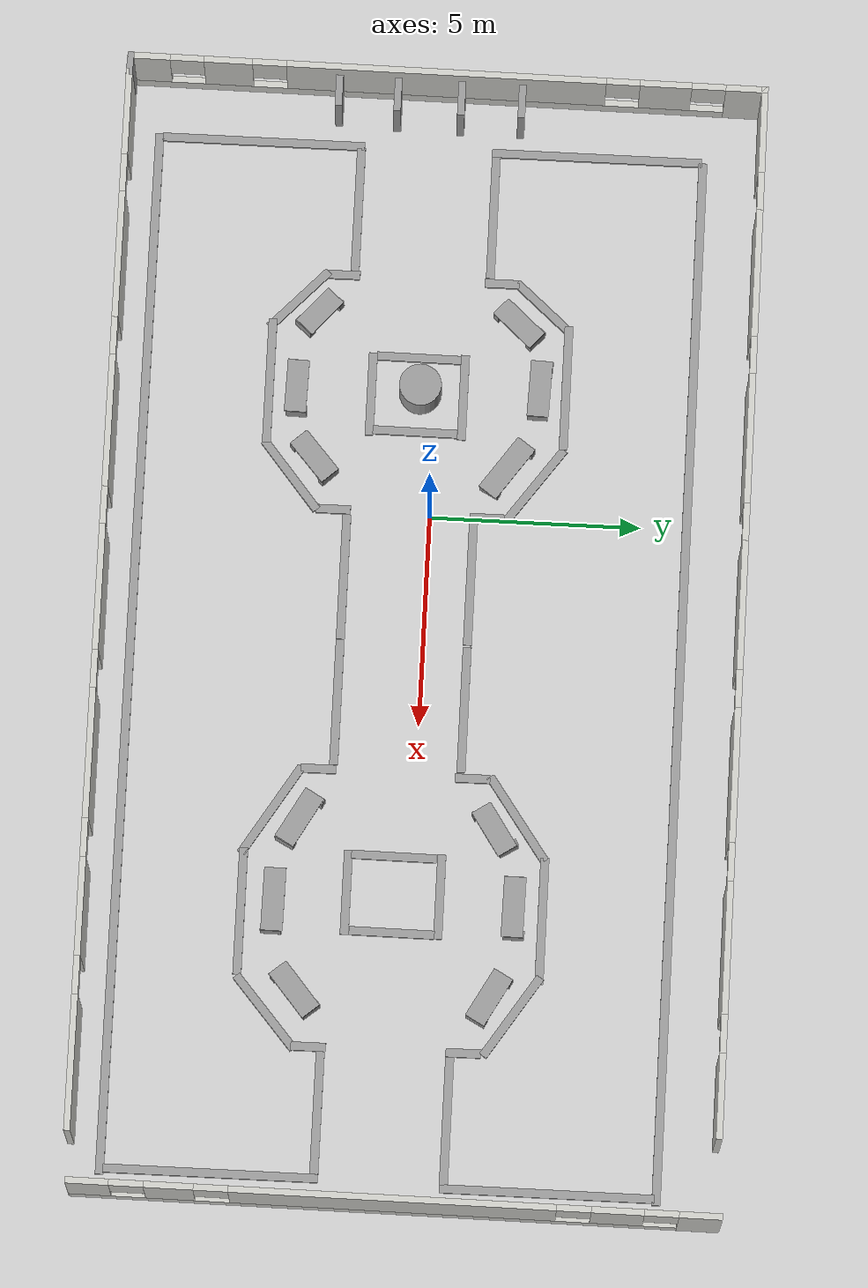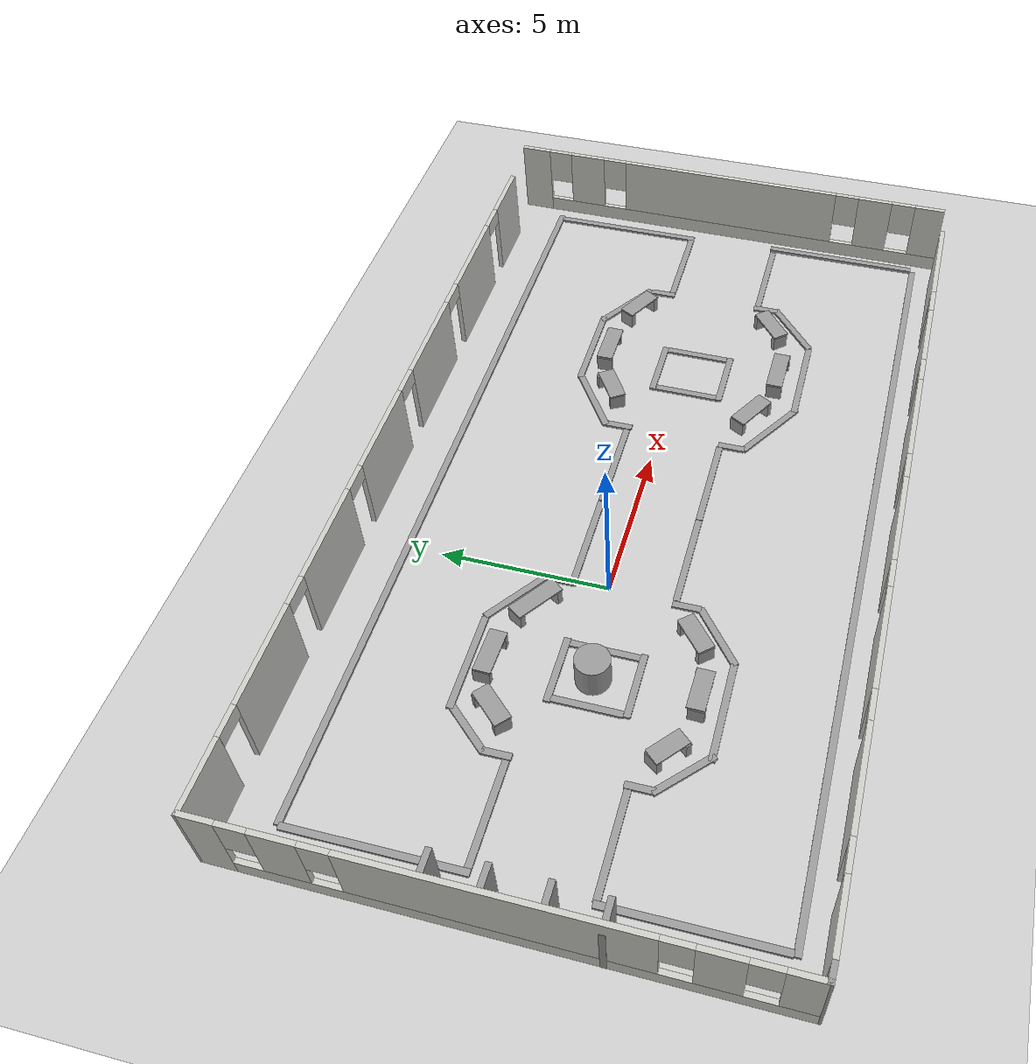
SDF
<sdf version="1.6">
 <world name="default">
  <light name="sun" type="directional">
   <pose>0 0 10 0 -0 0</pose>
   <diffuse>0.8 0.8 0.8 1</diffuse>
   <specular>0.1 0.1 0.1 1</specular>
   <attenuation>
    <range>1000</range>
    <constant>0.9</constant>
    <linear>0.01</linear>
    <quadratic>0.001</quadratic>
   </attenuation>
   <direction>-0.5 0.5 -1</direction>
  </light>
  <model name="ground_plane">
   <static>1</static>
   <link name="link">
    <collision name="collision">
     <geometry><plane><normal>0 0 1</normal><size>100 100</size></plane></geometry>
     <surface><friction><ode><mu>100</mu><mu2>50</mu2></ode></friction></surface>
    </collision>
    <visual name="visual">
     <cast_shadows>0</cast_shadows>
     <geometry><plane><normal>0 0 1</normal><size>100 100</size></plane></geometry>
     <material>
      <script><uri>file://media/materials/scripts/gazebo.material</uri><name>Gazebo/Grey</name></script>
     </material>
    </visual>
   </link>
  </model>
  <gravity>0 0 -9.8</gravity>
  <magnetic_field>6e-06 2.3e-05 -4.2e-05</magnetic_field>
  <atmosphere type="adiabatic"/>
  <physics name="default_physics" default="0" type="ode">
   <max_step_size>0.001</max_step_size>
   <real_time_factor>1</real_time_factor>
   <real_time_update_rate>1000</real_time_update_rate>
  </physics>
  <scene><ambient>0.4 0.4 0.4 1</ambient><background>0.7 0.7 0.7 1</background><shadows>1</shadows></scene>
  <spherical_coordinates>
   <surface_model>EARTH_WGS84</surface_model>
   <latitude_deg>0</latitude_deg>
   <longitude_deg>0</longitude_deg>
   <elevation>0</elevation>
   <heading_deg>0</heading_deg>
  </spherical_coordinates>
  <model name="brick_box_3x1x3">
   <link name="link_1">
    <pose>-1.85709 -0.304134 0.5 0 -0 0</pose>
    <inertial>
     <mass>0.964444</mass>
     <inertia>
      <ixx>0.155127</ixx>
      <ixy>0</ixy>
      <ixz>0</ixz>
      <iyy>0.160741</iyy>
      <iyz>0</iyz>
      <izz>0.155127</izz>
     </inertia>
    </inertial>
    <visual name="visual">
     <pose>0 0 -0.5 0 -0 0</pose>
     <geometry><box><size>0.2 4.82222 0.1</size></box></geometry>
     <material>
      <lighting>1</lighting>
      <script><uri>file://media/materials/scripts/gazebo.material</uri><name>Gazebo/Grey</name></script>
      <ambient>0.3 0.3 0.3 1</ambient>
      <diffuse>0.7 0.7 0.7 1</diffuse>
      <specular>0.01 0.01 0.01 1</specular>
      <emissive>0 0 0 1</emissive>
      <shader type="vertex"><normal_map>__default__</normal_map></shader>
     </material>
    </visual>
    <collision name="collision">
     <pose>0 0 -0.5 0 -0 0</pose>
     <geometry><box><size>0.1 4.82222 0.2</size></box></geometry>
     <surface>
      <friction>
       <ode><mu>1</mu><mu2>1</mu2><fdir1>0 0 0</fdir1><slip1>0</slip1><slip2>0</slip2></ode>
       <torsional>
        <coefficient>1</coefficient>
        <patch_radius>0</patch_radius>
        <surface_radius>0</surface_radius>
        <use_patch_radius>1</use_patch_radius>
        <ode><slip>0</slip></ode>
       </torsional>
      </friction>
      <bounce><restitution_coefficient>0</restitution_coefficient><threshold>1e+06</threshold></bounce>
      <contact>
       <collide_without_contact>0</collide_without_contact>
       <collide_without_contact_bitmask>1</collide_without_contact_bitmask>
       <collide_bitmask>1</collide_bitmask>
       <ode>
        <soft_cfm>0</soft_cfm>
        <soft_erp>0.2</soft_erp>
        <kp>1e+13</kp>
        <kd>1</kd>
        <max_vel>0.01</max_vel>
        <min_depth>0</min_depth>
       </ode>
       <bullet>
        <split_impulse>1</split_impulse>
        <split_impulse_penetration_threshold>-0.01</split_impulse_penetration_threshold>
        <soft_cfm>0</soft_cfm>
        <soft_erp>0.2</soft_erp>
        <kp>1e+13</kp>
        <kd>1</kd>
       </bullet>
      </contact>
     </surface>
    </collision>
   </link>
   <link name="link_1_clone">
    <pose>-1.84895 7.65508 0.5 0 -0 0</pose>
    <inertial>
     <mass>1</mass>
     <inertia>
      <ixx>0.166667</ixx>
      <ixy>0</ixy>
      <ixz>0</ixz>
      <iyy>0.166667</iyy>
      <iyz>0</iyz>
      <izz>0.166667</izz>
     </inertia>
    </inertial>
    <visual name="visual">
     <pose>0 0 -0.5 0 -0 0</pose>
     <geometry><box><size>0.2 5 0.1</size></box></geometry>
     <material>
      <lighting>1</lighting>
      <script><uri>file://media/materials/scripts/gazebo.material</uri><name>Gazebo/Grey</name></script>
      <ambient>0.3 0.3 0.3 1</ambient>
      <diffuse>0.7 0.7 0.7 1</diffuse>
      <specular>0.01 0.01 0.01 1</specular>
      <emissive>0 0 0 1</emissive>
      <shader type="vertex"><normal_map>__default__</normal_map></shader>
     </material>
    </visual>
    <collision name="collision">
     <pose>0 0 -0.5 0 -0 0</pose>
     <geometry><box><size>0.1 5 0.2</size></box></geometry>
     <surface>
      <friction>
       <ode><mu>1</mu><mu2>1</mu2><fdir1>0 0 0</fdir1><slip1>0</slip1><slip2>0</slip2></ode>
       <torsional>
        <coefficient>1</coefficient>
        <patch_radius>0</patch_radius>
        <surface_radius>0</surface_radius>
        <use_patch_radius>1</use_patch_radius>
        <ode><slip>0</slip></ode>
       </torsional>
      </friction>
      <bounce><restitution_coefficient>0</restitution_coefficient><threshold>1e+06</threshold></bounce>
      <contact>
       <collide_without_contact>0</collide_without_contact>
       <collide_without_contact_bitmask>1</collide_without_contact_bitmask>
       <collide_bitmask>1</collide_bitmask>
       <ode>
        <soft_cfm>0</soft_cfm>
        <soft_erp>0.2</soft_erp>
        <kp>1e+13</kp>
        <kd>1</kd>
        <max_vel>0.01</max_vel>
        <min_depth>0</min_depth>
       </ode>
       <bullet>
        <split_impulse>1</split_impulse>
        <split_impulse_penetration_threshold>-0.01</split_impulse_penetration_threshold>
        <soft_cfm>0</soft_cfm>
        <soft_erp>0.2</soft_erp>
        <kp>1e+13</kp>
        <kd>1</kd>
       </bullet>
      </contact>
     </surface>
    </collision>
   </link>
   <link name="link_1_clone_0">
    <pose>10.5728 -2.79376 0.5 0 -0 0</pose>
    <inertial>
     <mass>1</mass>
     <inertia>
      <ixx>0.166667</ixx>
      <ixy>0</ixy>
      <ixz>0</ixz>
      <iyy>0.166667</iyy>
      <iyz>0</iyz>
      <izz>0.166667</izz>
     </inertia>
    </inertial>
    <visual name="visual">
     <pose>0 0 -0.5 0 -0 0</pose>
     <geometry><box><size>25 0.2 0.1</size></box></geometry>
     <material>
      <lighting>1</lighting>
      <script><uri>file://media/materials/scripts/gazebo.material</uri><name>Gazebo/Grey</name></script>
      <ambient>0.3 0.3 0.3 1</ambient>
      <diffuse>0.7 0.7 0.7 1</diffuse>
      <specular>0.01 0.01 0.01 1</specular>
      <emissive>0 0 0 1</emissive>
      <shader type="vertex"><normal_map>__default__</normal_map></shader>
     </material>
    </visual>
    <collision name="collision">
     <pose>0 0 -0.5 0 -0 0</pose>
     <geometry><box><size>25 0.2 0.2</size></box></geometry>
     <surface>
      <friction>
       <ode><mu>1</mu><mu2>1</mu2><fdir1>0 0 0</fdir1><slip1>0</slip1><slip2>0</slip2></ode>
       <torsional>
        <coefficient>1</coefficient>
        <patch_radius>0</patch_radius>
        <surface_radius>0</surface_radius>
        <use_patch_radius>1</use_patch_radius>
        <ode><slip>0</slip></ode>
       </torsional>
      </friction>
      <bounce><restitution_coefficient>0</restitution_coefficient><threshold>1e+06</threshold></bounce>
      <contact>
       <collide_without_contact>0</collide_without_contact>
       <collide_without_contact_bitmask>1</collide_without_contact_bitmask>
       <collide_bitmask>1</collide_bitmask>
       <ode>
        <soft_cfm>0</soft_cfm>
        <soft_erp>0.2</soft_erp>
        <kp>1e+13</kp>
        <kd>1</kd>
        <max_vel>0.01</max_vel>
        <min_depth>0</min_depth>
       </ode>
       <bullet>
        <split_impulse>1</split_impulse>
        <split_impulse_penetration_threshold>-0.01</split_impulse_penetration_threshold>
        <soft_cfm>0</soft_cfm>
        <soft_erp>0.2</soft_erp>
        <kp>1e+13</kp>
        <kd>1</kd>
       </bullet>
      </contact>
     </surface>
    </collision>
   </link>
   <link name="link_1_clone_0_clone">
    <pose>10.6572 10.185 0.5 0 -0 0</pose>
    <inertial>
     <mass>1</mass>
     <inertia>
      <ixx>0.166667</ixx>
      <ixy>0</ixy>
      <ixz>0</ixz>
      <iyy>0.166667</iyy>
      <iyz>0</iyz>
      <izz>0.166667</izz>
     </inertia>
    </inertial>
    <visual name="visual">
     <pose>0 0 -0.5 0 -0 0</pose>
     <geometry><box><size>25 0.2 0.1</size></box></geometry>
     <material>
      <lighting>1</lighting>
      <script><uri>file://media/materials/scripts/gazebo.material</uri><name>Gazebo/Grey</name></script>
      <ambient>0.3 0.3 0.3 1</ambient>
      <diffuse>0.7 0.7 0.7 1</diffuse>
      <specular>0.01 0.01 0.01 1</specular>
      <emissive>0 0 0 1</emissive>
      <shader type="vertex"><normal_map>__default__</normal_map></shader>
     </material>
    </visual>
    <collision name="collision">
     <pose>0 0 -0.5 0 -0 0</pose>
     <geometry><box><size>25 0.2 0.2</size></box></geometry>
     <surface>
      <friction>
       <ode><mu>1</mu><mu2>1</mu2><fdir1>0 0 0</fdir1><slip1>0</slip1><slip2>0</slip2></ode>
       <torsional>
        <coefficient>1</coefficient>
        <patch_radius>0</patch_radius>
        <surface_radius>0</surface_radius>
        <use_patch_radius>1</use_patch_radius>
        <ode><slip>0</slip></ode>
       </torsional>
      </friction>
      <bounce><restitution_coefficient>0</restitution_coefficient><threshold>1e+06</threshold></bounce>
      <contact>
       <collide_without_contact>0</collide_without_contact>
       <collide_without_contact_bitmask>1</collide_without_contact_bitmask>
       <collide_bitmask>1</collide_bitmask>
       <ode>
        <soft_cfm>0</soft_cfm>
        <soft_erp>0.2</soft_erp>
        <kp>1e+13</kp>
        <kd>1</kd>
        <max_vel>0.01</max_vel>
        <min_depth>0</min_depth>
       </ode>
       <bullet>
        <split_impulse>1</split_impulse>
        <split_impulse_penetration_threshold>-0.01</split_impulse_penetration_threshold>
        <soft_cfm>0</soft_cfm>
        <soft_erp>0.2</soft_erp>
        <kp>1e+13</kp>
        <kd>1</kd>
       </bullet>
      </contact>
     </surface>
    </collision>
   </link>
   <link name="link_1_clone_1">
    <pose>22.9433 -0.208958 0.688101 0 -0 0</pose>
    <inertial>
     <mass>1</mass>
     <inertia>
      <ixx>0.166667</ixx>
      <ixy>0</ixy>
      <ixz>0</ixz>
      <iyy>0.166667</iyy>
      <iyz>0</iyz>
      <izz>0.166667</izz>
     </inertia>
    </inertial>
    <visual name="visual">
     <pose>0 0 -0.5 0 -0 0</pose>
     <geometry><box><size>0.2 5 0.1</size></box></geometry>
     <material>
      <lighting>1</lighting>
      <script><uri>file://media/materials/scripts/gazebo.material</uri><name>Gazebo/Grey</name></script>
      <ambient>0.3 0.3 0.3 1</ambient>
      <diffuse>0.7 0.7 0.7 1</diffuse>
      <specular>0.01 0.01 0.01 1</specular>
      <emissive>0 0 0 1</emissive>
      <shader type="vertex"><normal_map>__default__</normal_map></shader>
     </material>
    </visual>
    <collision name="collision">
     <pose>0 0 -0.5 0 -0 0</pose>
     <geometry><box><size>0.1 5 0.2</size></box></geometry>
     <surface>
      <friction>
       <ode><mu>1</mu><mu2>1</mu2><fdir1>0 0 0</fdir1><slip1>0</slip1><slip2>0</slip2></ode>
       <torsional>
        <coefficient>1</coefficient>
        <patch_radius>0</patch_radius>
        <surface_radius>0</surface_radius>
        <use_patch_radius>1</use_patch_radius>
        <ode><slip>0</slip></ode>
       </torsional>
      </friction>
      <bounce><restitution_coefficient>0</restitution_coefficient><threshold>1e+06</threshold></bounce>
      <contact>
       <collide_without_contact>0</collide_without_contact>
       <collide_without_contact_bitmask>1</collide_without_contact_bitmask>
       <collide_bitmask>1</collide_bitmask>
       <ode>
        <soft_cfm>0</soft_cfm>
        <soft_erp>0.2</soft_erp>
        <kp>1e+13</kp>
        <kd>1</kd>
        <max_vel>0.01</max_vel>
        <min_depth>0</min_depth>
       </ode>
       <bullet>
        <split_impulse>1</split_impulse>
        <split_impulse_penetration_threshold>-0.01</split_impulse_penetration_threshold>
        <soft_cfm>0</soft_cfm>
        <soft_erp>0.2</soft_erp>
        <kp>1e+13</kp>
        <kd>1</kd>
       </bullet>
      </contact>
     </surface>
    </collision>
   </link>
   <link name="link_1_clone_2">
    <pose>23.0117 7.63499 0.5 0 -0 0</pose>
    <inertial>
     <mass>1</mass>
     <inertia>
      <ixx>0.166667</ixx>
      <ixy>0</ixy>
      <ixz>0</ixz>
      <iyy>0.166667</iyy>
      <iyz>0</iyz>
      <izz>0.166667</izz>
     </inertia>
    </inertial>
    <visual name="visual">
     <pose>0 0 -0.5 0 -0 0</pose>
     <geometry><box><size>0.2 5 0.1</size></box></geometry>
     <material>
      <lighting>1</lighting>
      <script><uri>file://media/materials/scripts/gazebo.material</uri><name>Gazebo/Grey</name></script>
      <ambient>0.3 0.3 0.3 1</ambient>
      <diffuse>0.7 0.7 0.7 1</diffuse>
      <specular>0.01 0.01 0.01 1</specular>
      <emissive>0 0 0 1</emissive>
      <shader type="vertex"><normal_map>__default__</normal_map></shader>
     </material>
    </visual>
    <collision name="collision">
     <pose>0 0 -0.5 0 -0 0</pose>
     <geometry><box><size>0.1 5 0.2</size></box></geometry>
     <surface>
      <friction>
       <ode><mu>1</mu><mu2>1</mu2><fdir1>0 0 0</fdir1><slip1>0</slip1><slip2>0</slip2></ode>
       <torsional>
        <coefficient>1</coefficient>
        <patch_radius>0</patch_radius>
        <surface_radius>0</surface_radius>
        <use_patch_radius>1</use_patch_radius>
        <ode><slip>0</slip></ode>
       </torsional>
      </friction>
      <bounce><restitution_coefficient>0</restitution_coefficient><threshold>1e+06</threshold></bounce>
      <contact>
       <collide_without_contact>0</collide_without_contact>
       <collide_without_contact_bitmask>1</collide_without_contact_bitmask>
       <collide_bitmask>1</collide_bitmask>
       <ode>
        <soft_cfm>0</soft_cfm>
        <soft_erp>0.2</soft_erp>
        <kp>1e+13</kp>
        <kd>1</kd>
        <max_vel>0.01</max_vel>
        <min_depth>0</min_depth>
       </ode>
       <bullet>
        <split_impulse>1</split_impulse>
        <split_impulse_penetration_threshold>-0.01</split_impulse_penetration_threshold>
        <soft_cfm>0</soft_cfm>
        <soft_erp>0.2</soft_erp>
        <kp>1e+13</kp>
        <kd>1</kd>
       </bullet>
      </contact>
     </surface>
    </collision>
   </link>
   <link name="link_1_clone_3">
    <pose>-0.307076 2.03145 0.5 0 -0 0</pose>
    <inertial>
     <mass>1</mass>
     <inertia>
      <ixx>0.166667</ixx>
      <ixy>0</ixy>
      <ixz>0</ixz>
      <iyy>0.166667</iyy>
      <iyz>0</iyz>
      <izz>0.166667</izz>
     </inertia>
    </inertial>
    <visual name="visual">
     <pose>0 0 -0.5 0 -0 0</pose>
     <geometry><box><size>3 0.2 0.1</size></box></geometry>
     <material>
      <lighting>1</lighting>
      <script><uri>file://media/materials/scripts/gazebo.material</uri><name>Gazebo/Grey</name></script>
      <ambient>0.3 0.3 0.3 1</ambient>
      <diffuse>0.7 0.7 0.7 1</diffuse>
      <specular>0.01 0.01 0.01 1</specular>
      <emissive>0 0 0 1</emissive>
      <shader type="vertex"><normal_map>__default__</normal_map></shader>
     </material>
    </visual>
    <collision name="collision">
     <pose>0 0 -0.5 0 -0 0</pose>
     <geometry><box><size>3 0.2 0.2</size></box></geometry>
     <surface>
      <friction>
       <ode><mu>1</mu><mu2>1</mu2><fdir1>0 0 0</fdir1><slip1>0</slip1><slip2>0</slip2></ode>
       <torsional>
        <coefficient>1</coefficient>
        <patch_radius>0</patch_radius>
        <surface_radius>0</surface_radius>
        <use_patch_radius>1</use_patch_radius>
        <ode><slip>0</slip></ode>
       </torsional>
      </friction>
      <bounce><restitution_coefficient>0</restitution_coefficient><threshold>1e+06</threshold></bounce>
      <contact>
       <collide_without_contact>0</collide_without_contact>
       <collide_without_contact_bitmask>1</collide_without_contact_bitmask>
       <collide_bitmask>1</collide_bitmask>
       <ode>
        <soft_cfm>0</soft_cfm>
        <soft_erp>0.2</soft_erp>
        <kp>1e+13</kp>
        <kd>1</kd>
        <max_vel>0.01</max_vel>
        <min_depth>0</min_depth>
       </ode>
       <bullet>
        <split_impulse>1</split_impulse>
        <split_impulse_penetration_threshold>-0.01</split_impulse_penetration_threshold>
        <soft_cfm>0</soft_cfm>
        <soft_erp>0.2</soft_erp>
        <kp>1e+13</kp>
        <kd>1</kd>
       </bullet>
      </contact>
     </surface>
    </collision>
   </link>
   <link name="link_1_clone_3_clone">
    <pose>-0.278142 5.2552 0.5 0 -0 0</pose>
    <inertial>
     <mass>1</mass>
     <inertia>
      <ixx>0.166667</ixx>
      <ixy>0</ixy>
      <ixz>0</ixz>
      <iyy>0.166667</iyy>
      <iyz>0</iyz>
      <izz>0.166667</izz>
     </inertia>
    </inertial>
    <visual name="visual">
     <pose>0 0 -0.5 0 -0 0</pose>
     <geometry><box><size>3 0.2 0.1</size></box></geometry>
     <material>
      <lighting>1</lighting>
      <script><uri>file://media/materials/scripts/gazebo.material</uri><name>Gazebo/Grey</name></script>
      <ambient>0.3 0.3 0.3 1</ambient>
      <diffuse>0.7 0.7 0.7 1</diffuse>
      <specular>0.01 0.01 0.01 1</specular>
      <emissive>0 0 0 1</emissive>
      <shader type="vertex"><normal_map>__default__</normal_map></shader>
     </material>
    </visual>
    <collision name="collision">
     <pose>0 0 -0.5 0 -0 0</pose>
     <geometry><box><size>3 0.2 0.2</size></box></geometry>
     <surface>
      <friction>
       <ode><mu>1</mu><mu2>1</mu2><fdir1>0 0 0</fdir1><slip1>0</slip1><slip2>0</slip2></ode>
       <torsional>
        <coefficient>1</coefficient>
        <patch_radius>0</patch_radius>
        <surface_radius>0</surface_radius>
        <use_patch_radius>1</use_patch_radius>
        <ode><slip>0</slip></ode>
       </torsional>
      </friction>
      <bounce><restitution_coefficient>0</restitution_coefficient><threshold>1e+06</threshold></bounce>
      <contact>
       <collide_without_contact>0</collide_without_contact>
       <collide_without_contact_bitmask>1</collide_without_contact_bitmask>
       <collide_bitmask>1</collide_bitmask>
       <ode>
        <soft_cfm>0</soft_cfm>
        <soft_erp>0.2</soft_erp>
        <kp>1e+13</kp>
        <kd>1</kd>
        <max_vel>0.01</max_vel>
        <min_depth>0</min_depth>
       </ode>
       <bullet>
        <split_impulse>1</split_impulse>
        <split_impulse_penetration_threshold>-0.01</split_impulse_penetration_threshold>
        <soft_cfm>0</soft_cfm>
        <soft_erp>0.2</soft_erp>
        <kp>1e+13</kp>
        <kd>1</kd>
       </bullet>
      </contact>
     </surface>
    </collision>
   </link>
   <link name="link_1_clone_3_clone_0">
    <pose>21.4333 2.1957 0.5 0 -0 0</pose>
    <inertial>
     <mass>1</mass>
     <inertia>
      <ixx>0.166667</ixx>
      <ixy>0</ixy>
      <ixz>0</ixz>
      <iyy>0.166667</iyy>
      <iyz>0</iyz>
      <izz>0.166667</izz>
     </inertia>
    </inertial>
    <visual name="visual">
     <pose>0 0 -0.5 0 -0 0</pose>
     <geometry><box><size>3 0.2 0.1</size></box></geometry>
     <material>
      <lighting>1</lighting>
      <script><uri>file://media/materials/scripts/gazebo.material</uri><name>Gazebo/Grey</name></script>
      <ambient>0.3 0.3 0.3 1</ambient>
      <diffuse>0.7 0.7 0.7 1</diffuse>
      <specular>0.01 0.01 0.01 1</specular>
      <emissive>0 0 0 1</emissive>
      <shader type="vertex"><normal_map>__default__</normal_map></shader>
     </material>
    </visual>
    <collision name="collision">
     <pose>0 0 -0.5 0 -0 0</pose>
     <geometry><box><size>3 0.2 0.2</size></box></geometry>
     <surface>
      <friction>
       <ode><mu>1</mu><mu2>1</mu2><fdir1>0 0 0</fdir1><slip1>0</slip1><slip2>0</slip2></ode>
       <torsional>
        <coefficient>1</coefficient>
        <patch_radius>0</patch_radius>
        <surface_radius>0</surface_radius>
        <use_patch_radius>1</use_patch_radius>
        <ode><slip>0</slip></ode>
       </torsional>
      </friction>
      <bounce><restitution_coefficient>0</restitution_coefficient><threshold>1e+06</threshold></bounce>
      <contact>
       <collide_without_contact>0</collide_without_contact>
       <collide_without_contact_bitmask>1</collide_without_contact_bitmask>
       <collide_bitmask>1</collide_bitmask>
       <ode>
        <soft_cfm>0</soft_cfm>
        <soft_erp>0.2</soft_erp>
        <kp>1e+13</kp>
        <kd>1</kd>
        <max_vel>0.01</max_vel>
        <min_depth>0</min_depth>
       </ode>
       <bullet>
        <split_impulse>1</split_impulse>
        <split_impulse_penetration_threshold>-0.01</split_impulse_penetration_threshold>
        <soft_cfm>0</soft_cfm>
        <soft_erp>0.2</soft_erp>
        <kp>1e+13</kp>
        <kd>1</kd>
       </bullet>
      </contact>
     </surface>
    </collision>
   </link>
   <link name="link_1_clone_3_clone_1">
    <pose>21.421 5.22151 0.5 0 -0 0</pose>
    <inertial>
     <mass>1</mass>
     <inertia>
      <ixx>0.166667</ixx>
      <ixy>0</ixy>
      <ixz>0</ixz>
      <iyy>0.166667</iyy>
      <iyz>0</iyz>
      <izz>0.166667</izz>
     </inertia>
    </inertial>
    <visual name="visual">
     <pose>0 0 -0.5 0 -0 0</pose>
     <geometry><box><size>3 0.2 0.1</size></box></geometry>
     <material>
      <lighting>1</lighting>
      <script><uri>file://media/materials/scripts/gazebo.material</uri><name>Gazebo/Grey</name></script>
      <ambient>0.3 0.3 0.3 1</ambient>
      <diffuse>0.7 0.7 0.7 1</diffuse>
      <specular>0.01 0.01 0.01 1</specular>
      <emissive>0 0 0 1</emissive>
      <shader type="vertex"><normal_map>__default__</normal_map></shader>
     </material>
    </visual>
    <collision name="collision">
     <pose>0 0 -0.5 0 -0 0</pose>
     <geometry><box><size>3 0.2 0.2</size></box></geometry>
     <surface>
      <friction>
       <ode><mu>1</mu><mu2>1</mu2><fdir1>0 0 0</fdir1><slip1>0</slip1><slip2>0</slip2></ode>
       <torsional>
        <coefficient>1</coefficient>
        <patch_radius>0</patch_radius>
        <surface_radius>0</surface_radius>
        <use_patch_radius>1</use_patch_radius>
        <ode><slip>0</slip></ode>
       </torsional>
      </friction>
      <bounce><restitution_coefficient>0</restitution_coefficient><threshold>1e+06</threshold></bounce>
      <contact>
       <collide_without_contact>0</collide_without_contact>
       <collide_without_contact_bitmask>1</collide_without_contact_bitmask>
       <collide_bitmask>1</collide_bitmask>
       <ode>
        <soft_cfm>0</soft_cfm>
        <soft_erp>0.2</soft_erp>
        <kp>1e+13</kp>
        <kd>1</kd>
        <max_vel>0.01</max_vel>
        <min_depth>0</min_depth>
       </ode>
       <bullet>
        <split_impulse>1</split_impulse>
        <split_impulse_penetration_threshold>-0.01</split_impulse_penetration_threshold>
        <soft_cfm>0</soft_cfm>
        <soft_erp>0.2</soft_erp>
        <kp>1e+13</kp>
        <kd>1</kd>
       </bullet>
      </contact>
     </surface>
    </collision>
   </link>
   <link name="link_1_clone_3_clone_10">
    <pose>6.19258 6.57027 0.5 0 0 -0.628314</pose>
    <inertial>
     <mass>0.633292</mass>
     <inertia>
      <ixx>0.107431</ixx>
      <ixy>0</ixy>
      <ixz>0</ixz>
      <iyy>0.0732112</iyy>
      <iyz>0</iyz>
      <izz>0.0750937</izz>
     </inertia>
    </inertial>
    <visual name="visual">
     <pose>0 0 -0.5 0 -0 0</pose>
     <geometry><box><size>2.17802 0.203535 0.1</size></box></geometry>
     <material>
      <lighting>1</lighting>
      <script><uri>file://media/materials/scripts/gazebo.material</uri><name>Gazebo/Grey</name></script>
      <ambient>0.3 0.3 0.3 1</ambient>
      <diffuse>0.7 0.7 0.7 1</diffuse>
      <specular>0.01 0.01 0.01 1</specular>
      <emissive>0 0 0 1</emissive>
      <shader type="vertex"><normal_map>__default__</normal_map></shader>
     </material>
    </visual>
    <collision name="collision">
     <pose>0 0 -0.5 0 -0 0</pose>
     <geometry><box><size>2.17802 0.203535 0.2</size></box></geometry>
     <surface>
      <friction>
       <ode><mu>1</mu><mu2>1</mu2><fdir1>0 0 0</fdir1><slip1>0</slip1><slip2>0</slip2></ode>
       <torsional>
        <coefficient>1</coefficient>
        <patch_radius>0</patch_radius>
        <surface_radius>0</surface_radius>
        <use_patch_radius>1</use_patch_radius>
        <ode><slip>0</slip></ode>
       </torsional>
      </friction>
      <bounce><restitution_coefficient>0</restitution_coefficient><threshold>1e+06</threshold></bounce>
      <contact>
       <collide_without_contact>0</collide_without_contact>
       <collide_without_contact_bitmask>1</collide_without_contact_bitmask>
       <collide_bitmask>1</collide_bitmask>
       <ode>
        <soft_cfm>0</soft_cfm>
        <soft_erp>0.2</soft_erp>
        <kp>1e+13</kp>
        <kd>1</kd>
        <max_vel>0.01</max_vel>
        <min_depth>0</min_depth>
       </ode>
       <bullet>
        <split_impulse>1</split_impulse>
        <split_impulse_penetration_threshold>-0.01</split_impulse_penetration_threshold>
        <soft_cfm>0</soft_cfm>
        <soft_erp>0.2</soft_erp>
        <kp>1e+13</kp>
        <kd>1</kd>
       </bullet>
      </contact>
     </surface>
    </collision>
   </link>
   <link name="link_1_clone_3_clone_10_clone">
    <pose>1.95197 0.748415 0.5 0 0 -0.76059</pose>
    <inertial>
     <mass>0.5645</mass>
     <inertia>
      <ixx>0.0957615</ixx>
      <ixy>0</ixy>
      <ixz>0</ixz>
      <iyy>0.0615164</iyy>
      <iyz>0</iyz>
      <izz>0.0631938</izz>
     </inertia>
    </inertial>
    <visual name="visual">
     <pose>0 0 -0.5 0 -0 0</pose>
     <geometry><box><size>1.94144 0.203535 0.1</size></box></geometry>
     <material>
      <lighting>1</lighting>
      <script><uri>file://media/materials/scripts/gazebo.material</uri><name>Gazebo/Grey</name></script>
      <ambient>0.3 0.3 0.3 1</ambient>
      <diffuse>0.7 0.7 0.7 1</diffuse>
      <specular>0.01 0.01 0.01 1</specular>
      <emissive>0 0 0 1</emissive>
      <shader type="vertex"><normal_map>__default__</normal_map></shader>
     </material>
    </visual>
    <collision name="collision">
     <pose>0 0 -0.5 0 -0 0</pose>
     <geometry><box><size>1.94144 0.203535 0.2</size></box></geometry>
     <surface>
      <friction>
       <ode><mu>1</mu><mu2>1</mu2><fdir1>0 0 0</fdir1><slip1>0</slip1><slip2>0</slip2></ode>
       <torsional>
        <coefficient>1</coefficient>
        <patch_radius>0</patch_radius>
        <surface_radius>0</surface_radius>
        <use_patch_radius>1</use_patch_radius>
        <ode><slip>0</slip></ode>
       </torsional>
      </friction>
      <bounce><restitution_coefficient>0</restitution_coefficient><threshold>1e+06</threshold></bounce>
      <contact>
       <collide_without_contact>0</collide_without_contact>
       <collide_without_contact_bitmask>1</collide_without_contact_bitmask>
       <collide_bitmask>1</collide_bitmask>
       <ode>
        <soft_cfm>0</soft_cfm>
        <soft_erp>0.2</soft_erp>
        <kp>1e+13</kp>
        <kd>1</kd>
        <max_vel>0.01</max_vel>
        <min_depth>0</min_depth>
       </ode>
       <bullet>
        <split_impulse>1</split_impulse>
        <split_impulse_penetration_threshold>-0.01</split_impulse_penetration_threshold>
        <soft_cfm>0</soft_cfm>
        <soft_erp>0.2</soft_erp>
        <kp>1e+13</kp>
        <kd>1</kd>
       </bullet>
      </contact>
     </surface>
    </collision>
   </link>
   <link name="link_1_clone_3_clone_10_clone_0">
    <pose>1.88231 6.56558 0.5 0 0 -2.28733</pose>
    <inertial>
     <mass>0.507827</mass>
     <inertia>
      <ixx>0.0861472</ixx>
      <ixy>0</ixy>
      <ixz>0</ixz>
      <iyy>0.0528569</iyy>
      <iyz>0</iyz>
      <izz>0.0543659</izz>
     </inertia>
    </inertial>
    <visual name="visual">
     <pose>0 0 -0.5 0 -0 0</pose>
     <geometry><box><size>1.74653 0.203535 0.1</size></box></geometry>
     <material>
      <lighting>1</lighting>
      <script><uri>file://media/materials/scripts/gazebo.material</uri><name>Gazebo/Grey</name></script>
      <ambient>0.3 0.3 0.3 1</ambient>
      <diffuse>0.7 0.7 0.7 1</diffuse>
      <specular>0.01 0.01 0.01 1</specular>
      <emissive>0 0 0 1</emissive>
      <shader type="vertex"><normal_map>__default__</normal_map></shader>
     </material>
    </visual>
    <collision name="collision">
     <pose>0 0 -0.5 0 -0 0</pose>
     <geometry><box><size>1.74653 0.203535 0.2</size></box></geometry>
     <surface>
      <friction>
       <ode><mu>1</mu><mu2>1</mu2><fdir1>0 0 0</fdir1><slip1>0</slip1><slip2>0</slip2></ode>
       <torsional>
        <coefficient>1</coefficient>
        <patch_radius>0</patch_radius>
        <surface_radius>0</surface_radius>
        <use_patch_radius>1</use_patch_radius>
        <ode><slip>0</slip></ode>
       </torsional>
      </friction>
      <bounce><restitution_coefficient>0</restitution_coefficient><threshold>1e+06</threshold></bounce>
      <contact>
       <collide_without_contact>0</collide_without_contact>
       <collide_without_contact_bitmask>1</collide_without_contact_bitmask>
       <collide_bitmask>1</collide_bitmask>
       <ode>
        <soft_cfm>0</soft_cfm>
        <soft_erp>0.2</soft_erp>
        <kp>1e+13</kp>
        <kd>1</kd>
        <max_vel>0.01</max_vel>
        <min_depth>0</min_depth>
       </ode>
       <bullet>
        <split_impulse>1</split_impulse>
        <split_impulse_penetration_threshold>-0.01</split_impulse_penetration_threshold>
        <soft_cfm>0</soft_cfm>
        <soft_erp>0.2</soft_erp>
        <kp>1e+13</kp>
        <kd>1</kd>
       </bullet>
      </contact>
     </surface>
    </collision>
   </link>
   <link name="link_1_clone_3_clone_10_clone_1">
    <pose>1.30623 1.75197 0.5 0 0 -1.56821</pose>
    <inertial>
     <mass>0.239353</mass>
     <inertia>
      <ixx>0.0406036</ixx>
      <ixy>0</ixy>
      <ixz>0</ixz>
      <iyy>0.0210496</iyy>
      <iyz>0</iyz>
      <izz>0.0217608</izz>
     </inertia>
    </inertial>
    <visual name="visual">
     <pose>0 0 -0.5 0 -0 0</pose>
     <geometry><box><size>0.823187 0.203535 0.1</size></box></geometry>
     <material>
      <lighting>1</lighting>
      <script><uri>file://media/materials/scripts/gazebo.material</uri><name>Gazebo/Grey</name></script>
      <ambient>0.3 0.3 0.3 1</ambient>
      <diffuse>0.7 0.7 0.7 1</diffuse>
      <specular>0.01 0.01 0.01 1</specular>
      <emissive>0 0 0 1</emissive>
      <shader type="vertex"><normal_map>__default__</normal_map></shader>
     </material>
    </visual>
    <collision name="collision">
     <pose>0 0 -0.5 0 -0 0</pose>
     <geometry><box><size>0.823187 0.203535 0.2</size></box></geometry>
     <surface>
      <friction>
       <ode><mu>1</mu><mu2>1</mu2><fdir1>0 0 0</fdir1><slip1>0</slip1><slip2>0</slip2></ode>
       <torsional>
        <coefficient>1</coefficient>
        <patch_radius>0</patch_radius>
        <surface_radius>0</surface_radius>
        <use_patch_radius>1</use_patch_radius>
        <ode><slip>0</slip></ode>
       </torsional>
      </friction>
      <bounce><restitution_coefficient>0</restitution_coefficient><threshold>1e+06</threshold></bounce>
      <contact>
       <collide_without_contact>0</collide_without_contact>
       <collide_without_contact_bitmask>1</collide_without_contact_bitmask>
       <collide_bitmask>1</collide_bitmask>
       <ode>
        <soft_cfm>0</soft_cfm>
        <soft_erp>0.2</soft_erp>
        <kp>1e+13</kp>
        <kd>1</kd>
        <max_vel>0.01</max_vel>
        <min_depth>0</min_depth>
       </ode>
       <bullet>
        <split_impulse>1</split_impulse>
        <split_impulse_penetration_threshold>-0.01</split_impulse_penetration_threshold>
        <soft_cfm>0</soft_cfm>
        <soft_erp>0.2</soft_erp>
        <kp>1e+13</kp>
        <kd>1</kd>
       </bullet>
      </contact>
     </surface>
    </collision>
   </link>
   <link name="link_1_clone_3_clone_10_clone_1_clone">
    <pose>1.33845 5.54897 0.5 0 0 -1.56821</pose>
    <inertial>
     <mass>0.239353</mass>
     <inertia>
      <ixx>0.0406036</ixx>
      <ixy>0</ixy>
      <ixz>0</ixz>
      <iyy>0.0210496</iyy>
      <iyz>0</iyz>
      <izz>0.0217608</izz>
     </inertia>
    </inertial>
    <visual name="visual">
     <pose>0 0 -0.5 0 -0 0</pose>
     <geometry><box><size>0.823187 0.203535 0.1</size></box></geometry>
     <material>
      <lighting>1</lighting>
      <script><uri>file://media/materials/scripts/gazebo.material</uri><name>Gazebo/Grey</name></script>
      <ambient>0.3 0.3 0.3 1</ambient>
      <diffuse>0.7 0.7 0.7 1</diffuse>
      <specular>0.01 0.01 0.01 1</specular>
      <emissive>0 0 0 1</emissive>
      <shader type="vertex"><normal_map>__default__</normal_map></shader>
     </material>
    </visual>
    <collision name="collision">
     <pose>0 0 -0.5 0 -0 0</pose>
     <geometry><box><size>0.823187 0.203535 0.2</size></box></geometry>
     <surface>
      <friction>
       <ode><mu>1</mu><mu2>1</mu2><fdir1>0 0 0</fdir1><slip1>0</slip1><slip2>0</slip2></ode>
       <torsional>
        <coefficient>1</coefficient>
        <patch_radius>0</patch_radius>
        <surface_radius>0</surface_radius>
        <use_patch_radius>1</use_patch_radius>
        <ode><slip>0</slip></ode>
       </torsional>
      </friction>
      <bounce><restitution_coefficient>0</restitution_coefficient><threshold>1e+06</threshold></bounce>
      <contact>
       <collide_without_contact>0</collide_without_contact>
       <collide_without_contact_bitmask>1</collide_without_contact_bitmask>
       <collide_bitmask>1</collide_bitmask>
       <ode>
        <soft_cfm>0</soft_cfm>
        <soft_erp>0.2</soft_erp>
        <kp>1e+13</kp>
        <kd>1</kd>
        <max_vel>0.01</max_vel>
        <min_depth>0</min_depth>
       </ode>
       <bullet>
        <split_impulse>1</split_impulse>
        <split_impulse_penetration_threshold>-0.01</split_impulse_penetration_threshold>
        <soft_cfm>0</soft_cfm>
        <soft_erp>0.2</soft_erp>
        <kp>1e+13</kp>
        <kd>1</kd>
       </bullet>
      </contact>
     </surface>
    </collision>
   </link>
   <link name="link_1_clone_3_clone_10_clone_1_clone_0">
    <pose>7.00342 1.81838 0.5 0 0 -1.56821</pose>
    <inertial>
     <mass>0.239353</mass>
     <inertia>
      <ixx>0.0406036</ixx>
      <ixy>0</ixy>
      <ixz>0</ixz>
      <iyy>0.0210496</iyy>
      <iyz>0</iyz>
      <izz>0.0217608</izz>
     </inertia>
    </inertial>
    <visual name="visual">
     <pose>0 0 -0.5 0 -0 0</pose>
     <geometry><box><size>0.823187 0.203535 0.1</size></box></geometry>
     <material>
      <lighting>1</lighting>
      <script><uri>file://media/materials/scripts/gazebo.material</uri><name>Gazebo/Grey</name></script>
      <ambient>0.3 0.3 0.3 1</ambient>
      <diffuse>0.7 0.7 0.7 1</diffuse>
      <specular>0.01 0.01 0.01 1</specular>
      <emissive>0 0 0 1</emissive>
      <shader type="vertex"><normal_map>__default__</normal_map></shader>
     </material>
    </visual>
    <collision name="collision">
     <pose>0 0 -0.5 0 -0 0</pose>
     <geometry><box><size>0.823187 0.203535 0.2</size></box></geometry>
     <surface>
      <friction>
       <ode><mu>1</mu><mu2>1</mu2><fdir1>0 0 0</fdir1><slip1>0</slip1><slip2>0</slip2></ode>
       <torsional>
        <coefficient>1</coefficient>
        <patch_radius>0</patch_radius>
        <surface_radius>0</surface_radius>
        <use_patch_radius>1</use_patch_radius>
        <ode><slip>0</slip></ode>
       </torsional>
      </friction>
      <bounce><restitution_coefficient>0</restitution_coefficient><threshold>1e+06</threshold></bounce>
      <contact>
       <collide_without_contact>0</collide_without_contact>
       <collide_without_contact_bitmask>1</collide_without_contact_bitmask>
       <collide_bitmask>1</collide_bitmask>
       <ode>
        <soft_cfm>0</soft_cfm>
        <soft_erp>0.2</soft_erp>
        <kp>1e+13</kp>
        <kd>1</kd>
        <max_vel>0.01</max_vel>
        <min_depth>0</min_depth>
       </ode>
       <bullet>
        <split_impulse>1</split_impulse>
        <split_impulse_penetration_threshold>-0.01</split_impulse_penetration_threshold>
        <soft_cfm>0</soft_cfm>
        <soft_erp>0.2</soft_erp>
        <kp>1e+13</kp>
        <kd>1</kd>
       </bullet>
      </contact>
     </surface>
    </collision>
   </link>
   <link name="link_1_clone_3_clone_10_clone_1_clone_1">
    <pose>7.04036 5.46158 0.5 0 0 -1.56821</pose>
    <inertial>
     <mass>0.239353</mass>
     <inertia>
      <ixx>0.0406036</ixx>
      <ixy>0</ixy>
      <ixz>0</ixz>
      <iyy>0.0210496</iyy>
      <iyz>0</iyz>
      <izz>0.0217608</izz>
     </inertia>
    </inertial>
    <visual name="visual">
     <pose>0 0 -0.5 0 -0 0</pose>
     <geometry><box><size>0.823187 0.203535 0.1</size></box></geometry>
     <material>
      <lighting>1</lighting>
      <script><uri>file://media/materials/scripts/gazebo.material</uri><name>Gazebo/Grey</name></script>
      <ambient>0.3 0.3 0.3 1</ambient>
      <diffuse>0.7 0.7 0.7 1</diffuse>
      <specular>0.01 0.01 0.01 1</specular>
      <emissive>0 0 0 1</emissive>
      <shader type="vertex"><normal_map>__default__</normal_map></shader>
     </material>
    </visual>
    <collision name="collision">
     <pose>0 0 -0.5 0 -0 0</pose>
     <geometry><box><size>0.823187 0.203535 0.2</size></box></geometry>
     <surface>
      <friction>
       <ode><mu>1</mu><mu2>1</mu2><fdir1>0 0 0</fdir1><slip1>0</slip1><slip2>0</slip2></ode>
       <torsional>
        <coefficient>1</coefficient>
        <patch_radius>0</patch_radius>
        <surface_radius>0</surface_radius>
        <use_patch_radius>1</use_patch_radius>
        <ode><slip>0</slip></ode>
       </torsional>
      </friction>
      <bounce><restitution_coefficient>0</restitution_coefficient><threshold>1e+06</threshold></bounce>
      <contact>
       <collide_without_contact>0</collide_without_contact>
       <collide_without_contact_bitmask>1</collide_without_contact_bitmask>
       <collide_bitmask>1</collide_bitmask>
       <ode>
        <soft_cfm>0</soft_cfm>
        <soft_erp>0.2</soft_erp>
        <kp>1e+13</kp>
        <kd>1</kd>
        <max_vel>0.01</max_vel>
        <min_depth>0</min_depth>
       </ode>
       <bullet>
        <split_impulse>1</split_impulse>
        <split_impulse_penetration_threshold>-0.01</split_impulse_penetration_threshold>
        <soft_cfm>0</soft_cfm>
        <soft_erp>0.2</soft_erp>
        <kp>1e+13</kp>
        <kd>1</kd>
       </bullet>
      </contact>
     </surface>
    </collision>
   </link>
   <link name="link_1_clone_3_clone_10_clone_1_clone_2">
    <pose>13.2467 1.79727 0.5 0 0 -1.56821</pose>
    <inertial>
     <mass>0.239353</mass>
     <inertia>
      <ixx>0.0406036</ixx>
      <ixy>0</ixy>
      <ixz>0</ixz>
      <iyy>0.0210496</iyy>
      <iyz>0</iyz>
      <izz>0.0217608</izz>
     </inertia>
    </inertial>
    <visual name="visual">
     <pose>0 0 -0.5 0 -0 0</pose>
     <geometry><box><size>0.823187 0.203535 0.1</size></box></geometry>
     <material>
      <lighting>1</lighting>
      <script><uri>file://media/materials/scripts/gazebo.material</uri><name>Gazebo/Grey</name></script>
      <ambient>0.3 0.3 0.3 1</ambient>
      <diffuse>0.7 0.7 0.7 1</diffuse>
      <specular>0.01 0.01 0.01 1</specular>
      <emissive>0 0 0 1</emissive>
      <shader type="vertex"><normal_map>__default__</normal_map></shader>
     </material>
    </visual>
    <collision name="collision">
     <pose>0 0 -0.5 0 -0 0</pose>
     <geometry><box><size>0.823187 0.203535 0.2</size></box></geometry>
     <surface>
      <friction>
       <ode><mu>1</mu><mu2>1</mu2><fdir1>0 0 0</fdir1><slip1>0</slip1><slip2>0</slip2></ode>
       <torsional>
        <coefficient>1</coefficient>
        <patch_radius>0</patch_radius>
        <surface_radius>0</surface_radius>
        <use_patch_radius>1</use_patch_radius>
        <ode><slip>0</slip></ode>
       </torsional>
      </friction>
      <bounce><restitution_coefficient>0</restitution_coefficient><threshold>1e+06</threshold></bounce>
      <contact>
       <collide_without_contact>0</collide_without_contact>
       <collide_without_contact_bitmask>1</collide_without_contact_bitmask>
       <collide_bitmask>1</collide_bitmask>
       <ode>
        <soft_cfm>0</soft_cfm>
        <soft_erp>0.2</soft_erp>
        <kp>1e+13</kp>
        <kd>1</kd>
        <max_vel>0.01</max_vel>
        <min_depth>0</min_depth>
       </ode>
       <bullet>
        <split_impulse>1</split_impulse>
        <split_impulse_penetration_threshold>-0.01</split_impulse_penetration_threshold>
        <soft_cfm>0</soft_cfm>
        <soft_erp>0.2</soft_erp>
        <kp>1e+13</kp>
        <kd>1</kd>
       </bullet>
      </contact>
     </surface>
    </collision>
   </link>
   <link name="link_1_clone_3_clone_10_clone_1_clone_3">
    <pose>13.302 5.42831 0.5 0 0 -1.56821</pose>
    <inertial>
     <mass>0.239353</mass>
     <inertia>
      <ixx>0.0406036</ixx>
      <ixy>0</ixy>
      <ixz>0</ixz>
      <iyy>0.0210496</iyy>
      <iyz>0</iyz>
      <izz>0.0217608</izz>
     </inertia>
    </inertial>
    <visual name="visual">
     <pose>0 0 -0.5 0 -0 0</pose>
     <geometry><box><size>0.823187 0.203535 0.1</size></box></geometry>
     <material>
      <lighting>1</lighting>
      <script><uri>file://media/materials/scripts/gazebo.material</uri><name>Gazebo/Grey</name></script>
      <ambient>0.3 0.3 0.3 1</ambient>
      <diffuse>0.7 0.7 0.7 1</diffuse>
      <specular>0.01 0.01 0.01 1</specular>
      <emissive>0 0 0 1</emissive>
      <shader type="vertex"><normal_map>__default__</normal_map></shader>
     </material>
    </visual>
    <collision name="collision">
     <pose>0 0 -0.5 0 -0 0</pose>
     <geometry><box><size>0.823187 0.203535 0.2</size></box></geometry>
     <surface>
      <friction>
       <ode><mu>1</mu><mu2>1</mu2><fdir1>0 0 0</fdir1><slip1>0</slip1><slip2>0</slip2></ode>
       <torsional>
        <coefficient>1</coefficient>
        <patch_radius>0</patch_radius>
        <surface_radius>0</surface_radius>
        <use_patch_radius>1</use_patch_radius>
        <ode><slip>0</slip></ode>
       </torsional>
      </friction>
      <bounce><restitution_coefficient>0</restitution_coefficient><threshold>1e+06</threshold></bounce>
      <contact>
       <collide_without_contact>0</collide_without_contact>
       <collide_without_contact_bitmask>1</collide_without_contact_bitmask>
       <collide_bitmask>1</collide_bitmask>
       <ode>
        <soft_cfm>0</soft_cfm>
        <soft_erp>0.2</soft_erp>
        <kp>1e+13</kp>
        <kd>1</kd>
        <max_vel>0.01</max_vel>
        <min_depth>0</min_depth>
       </ode>
       <bullet>
        <split_impulse>1</split_impulse>
        <split_impulse_penetration_threshold>-0.01</split_impulse_penetration_threshold>
        <soft_cfm>0</soft_cfm>
        <soft_erp>0.2</soft_erp>
        <kp>1e+13</kp>
        <kd>1</kd>
       </bullet>
      </contact>
     </surface>
    </collision>
   </link>
   <link name="link_1_clone_3_clone_10_clone_1_clone_4">
    <pose>19.8376 1.90733 0.5 0 0 -1.56821</pose>
    <inertial>
     <mass>0.239353</mass>
     <inertia>
      <ixx>0.0406036</ixx>
      <ixy>0</ixy>
      <ixz>0</ixz>
      <iyy>0.0210496</iyy>
      <iyz>0</iyz>
      <izz>0.0217608</izz>
     </inertia>
    </inertial>
    <visual name="visual">
     <pose>0 0 -0.5 0 -0 0</pose>
     <geometry><box><size>0.823187 0.203535 0.1</size></box></geometry>
     <material>
      <lighting>1</lighting>
      <script><uri>file://media/materials/scripts/gazebo.material</uri><name>Gazebo/Grey</name></script>
      <ambient>0.3 0.3 0.3 1</ambient>
      <diffuse>0.7 0.7 0.7 1</diffuse>
      <specular>0.01 0.01 0.01 1</specular>
      <emissive>0 0 0 1</emissive>
      <shader type="vertex"><normal_map>__default__</normal_map></shader>
     </material>
    </visual>
    <collision name="collision">
     <pose>0 0 -0.5 0 -0 0</pose>
     <geometry><box><size>0.823187 0.203535 0.2</size></box></geometry>
     <surface>
      <friction>
       <ode><mu>1</mu><mu2>1</mu2><fdir1>0 0 0</fdir1><slip1>0</slip1><slip2>0</slip2></ode>
       <torsional>
        <coefficient>1</coefficient>
        <patch_radius>0</patch_radius>
        <surface_radius>0</surface_radius>
        <use_patch_radius>1</use_patch_radius>
        <ode><slip>0</slip></ode>
       </torsional>
      </friction>
      <bounce><restitution_coefficient>0</restitution_coefficient><threshold>1e+06</threshold></bounce>
      <contact>
       <collide_without_contact>0</collide_without_contact>
       <collide_without_contact_bitmask>1</collide_without_contact_bitmask>
       <collide_bitmask>1</collide_bitmask>
       <ode>
        <soft_cfm>0</soft_cfm>
        <soft_erp>0.2</soft_erp>
        <kp>1e+13</kp>
        <kd>1</kd>
        <max_vel>0.01</max_vel>
        <min_depth>0</min_depth>
       </ode>
       <bullet>
        <split_impulse>1</split_impulse>
        <split_impulse_penetration_threshold>-0.01</split_impulse_penetration_threshold>
        <soft_cfm>0</soft_cfm>
        <soft_erp>0.2</soft_erp>
        <kp>1e+13</kp>
        <kd>1</kd>
       </bullet>
      </contact>
     </surface>
    </collision>
   </link>
   <link name="link_1_clone_3_clone_10_clone_1_clone_5">
    <pose>19.8123 5.5335 0.5 0 0 -1.56821</pose>
    <inertial>
     <mass>0.239353</mass>
     <inertia>
      <ixx>0.0406036</ixx>
      <ixy>0</ixy>
      <ixz>0</ixz>
      <iyy>0.0210496</iyy>
      <iyz>0</iyz>
      <izz>0.0217608</izz>
     </inertia>
    </inertial>
    <visual name="visual">
     <pose>0 0 -0.5 0 -0 0</pose>
     <geometry><box><size>0.823187 0.203535 0.1</size></box></geometry>
     <material>
      <lighting>1</lighting>
      <script><uri>file://media/materials/scripts/gazebo.material</uri><name>Gazebo/Grey</name></script>
      <ambient>0.3 0.3 0.3 1</ambient>
      <diffuse>0.7 0.7 0.7 1</diffuse>
      <specular>0.01 0.01 0.01 1</specular>
      <emissive>0 0 0 1</emissive>
      <shader type="vertex"><normal_map>__default__</normal_map></shader>
     </material>
    </visual>
    <collision name="collision">
     <pose>0 0 -0.5 0 -0 0</pose>
     <geometry><box><size>0.823187 0.203535 0.2</size></box></geometry>
     <surface>
      <friction>
       <ode><mu>1</mu><mu2>1</mu2><fdir1>0 0 0</fdir1><slip1>0</slip1><slip2>0</slip2></ode>
       <torsional>
        <coefficient>1</coefficient>
        <patch_radius>0</patch_radius>
        <surface_radius>0</surface_radius>
        <use_patch_radius>1</use_patch_radius>
        <ode><slip>0</slip></ode>
       </torsional>
      </friction>
      <bounce><restitution_coefficient>0</restitution_coefficient><threshold>1e+06</threshold></bounce>
      <contact>
       <collide_without_contact>0</collide_without_contact>
       <collide_without_contact_bitmask>1</collide_without_contact_bitmask>
       <collide_bitmask>1</collide_bitmask>
       <ode>
        <soft_cfm>0</soft_cfm>
        <soft_erp>0.2</soft_erp>
        <kp>1e+13</kp>
        <kd>1</kd>
        <max_vel>0.01</max_vel>
        <min_depth>0</min_depth>
       </ode>
       <bullet>
        <split_impulse>1</split_impulse>
        <split_impulse_penetration_threshold>-0.01</split_impulse_penetration_threshold>
        <soft_cfm>0</soft_cfm>
        <soft_erp>0.2</soft_erp>
        <kp>1e+13</kp>
        <kd>1</kd>
       </bullet>
      </contact>
     </surface>
    </collision>
   </link>
   <link name="link_1_clone_3_clone_10_clone_2">
    <pose>6.23458 0.770061 0.5 0 0 -2.45426</pose>
    <inertial>
     <mass>0.603389</mass>
     <inertia>
      <ixx>0.102359</ixx>
      <ixy>0</ixy>
      <ixz>0</ixz>
      <iyy>0.0679589</iyy>
      <iyz>0</iyz>
      <izz>0.0697524</izz>
     </inertia>
    </inertial>
    <visual name="visual">
     <pose>0 0 -0.5 0 -0 0</pose>
     <geometry><box><size>2.07517 0.203535 0.1</size></box></geometry>
     <material>
      <lighting>1</lighting>
      <script><uri>file://media/materials/scripts/gazebo.material</uri><name>Gazebo/Grey</name></script>
      <ambient>0.3 0.3 0.3 1</ambient>
      <diffuse>0.7 0.7 0.7 1</diffuse>
      <specular>0.01 0.01 0.01 1</specular>
      <emissive>0 0 0 1</emissive>
      <shader type="vertex"><normal_map>__default__</normal_map></shader>
     </material>
    </visual>
    <collision name="collision">
     <pose>0 0 -0.5 0 -0 0</pose>
     <geometry><box><size>2.07517 0.203535 0.2</size></box></geometry>
     <surface>
      <friction>
       <ode><mu>1</mu><mu2>1</mu2><fdir1>0 0 0</fdir1><slip1>0</slip1><slip2>0</slip2></ode>
       <torsional>
        <coefficient>1</coefficient>
        <patch_radius>0</patch_radius>
        <surface_radius>0</surface_radius>
        <use_patch_radius>1</use_patch_radius>
        <ode><slip>0</slip></ode>
       </torsional>
      </friction>
      <bounce><restitution_coefficient>0</restitution_coefficient><threshold>1e+06</threshold></bounce>
      <contact>
       <collide_without_contact>0</collide_without_contact>
       <collide_without_contact_bitmask>1</collide_without_contact_bitmask>
       <collide_bitmask>1</collide_bitmask>
       <ode>
        <soft_cfm>0</soft_cfm>
        <soft_erp>0.2</soft_erp>
        <kp>1e+13</kp>
        <kd>1</kd>
        <max_vel>0.01</max_vel>
        <min_depth>0</min_depth>
       </ode>
       <bullet>
        <split_impulse>1</split_impulse>
        <split_impulse_penetration_threshold>-0.01</split_impulse_penetration_threshold>
        <soft_cfm>0</soft_cfm>
        <soft_erp>0.2</soft_erp>
        <kp>1e+13</kp>
        <kd>1</kd>
       </bullet>
      </contact>
     </surface>
    </collision>
   </link>
   <link name="link_1_clone_3_clone_10_clone_4">
    <pose>18.8978 6.62107 0.5 0 0 -0.579619</pose>
    <inertial>
     <mass>0.66633</mass>
     <inertia>
      <ixx>0.113036</ixx>
      <ixy>0</ixy>
      <ixz>0</ixz>
      <iyy>0.0793326</iyy>
      <iyz>0</iyz>
      <izz>0.0813132</izz>
     </inertia>
    </inertial>
    <visual name="visual">
     <pose>0 0 -0.5 0 -0 0</pose>
     <geometry><box><size>2.29164 0.203535 0.1</size></box></geometry>
     <material>
      <lighting>1</lighting>
      <script><uri>file://media/materials/scripts/gazebo.material</uri><name>Gazebo/Grey</name></script>
      <ambient>0.3 0.3 0.3 1</ambient>
      <diffuse>0.7 0.7 0.7 1</diffuse>
      <specular>0.01 0.01 0.01 1</specular>
      <emissive>0 0 0 1</emissive>
      <shader type="vertex"><normal_map>__default__</normal_map></shader>
     </material>
    </visual>
    <collision name="collision">
     <pose>0 0 -0.5 0 -0 0</pose>
     <geometry><box><size>2.29164 0.203535 0.2</size></box></geometry>
     <surface>
      <friction>
       <ode><mu>1</mu><mu2>1</mu2><fdir1>0 0 0</fdir1><slip1>0</slip1><slip2>0</slip2></ode>
       <torsional>
        <coefficient>1</coefficient>
        <patch_radius>0</patch_radius>
        <surface_radius>0</surface_radius>
        <use_patch_radius>1</use_patch_radius>
        <ode><slip>0</slip></ode>
       </torsional>
      </friction>
      <bounce><restitution_coefficient>0</restitution_coefficient><threshold>1e+06</threshold></bounce>
      <contact>
       <collide_without_contact>0</collide_without_contact>
       <collide_without_contact_bitmask>1</collide_without_contact_bitmask>
       <collide_bitmask>1</collide_bitmask>
       <ode>
        <soft_cfm>0</soft_cfm>
        <soft_erp>0.2</soft_erp>
        <kp>1e+13</kp>
        <kd>1</kd>
        <max_vel>0.01</max_vel>
        <min_depth>0</min_depth>
       </ode>
       <bullet>
        <split_impulse>1</split_impulse>
        <split_impulse_penetration_threshold>-0.01</split_impulse_penetration_threshold>
        <soft_cfm>0</soft_cfm>
        <soft_erp>0.2</soft_erp>
        <kp>1e+13</kp>
        <kd>1</kd>
       </bullet>
      </contact>
     </surface>
    </collision>
   </link>
   <link name="link_1_clone_3_clone_10_clone_4_clone">
    <pose>14.2781 0.747531 0.5 0 0 -0.55659</pose>
    <inertial>
     <mass>0.726749</mass>
     <inertia>
      <ixx>0.123285</ixx>
      <ixy>0</ixy>
      <ixz>0</ixz>
      <iyy>0.0914481</iyy>
      <iyz>0</iyz>
      <izz>0.0936075</izz>
     </inertia>
    </inertial>
    <visual name="visual">
     <pose>0 0 -0.5 0 -0 0</pose>
     <geometry><box><size>2.49943 0.203535 0.1</size></box></geometry>
     <material>
      <lighting>1</lighting>
      <script><uri>file://media/materials/scripts/gazebo.material</uri><name>Gazebo/Grey</name></script>
      <ambient>0.3 0.3 0.3 1</ambient>
      <diffuse>0.7 0.7 0.7 1</diffuse>
      <specular>0.01 0.01 0.01 1</specular>
      <emissive>0 0 0 1</emissive>
      <shader type="vertex"><normal_map>__default__</normal_map></shader>
     </material>
    </visual>
    <collision name="collision">
     <pose>0 0 -0.5 0 -0 0</pose>
     <geometry><box><size>2.49943 0.203535 0.2</size></box></geometry>
     <surface>
      <friction>
       <ode><mu>1</mu><mu2>1</mu2><fdir1>0 0 0</fdir1><slip1>0</slip1><slip2>0</slip2></ode>
       <torsional>
        <coefficient>1</coefficient>
        <patch_radius>0</patch_radius>
        <surface_radius>0</surface_radius>
        <use_patch_radius>1</use_patch_radius>
        <ode><slip>0</slip></ode>
       </torsional>
      </friction>
      <bounce><restitution_coefficient>0</restitution_coefficient><threshold>1e+06</threshold></bounce>
      <contact>
       <collide_without_contact>0</collide_without_contact>
       <collide_without_contact_bitmask>1</collide_without_contact_bitmask>
       <collide_bitmask>1</collide_bitmask>
       <ode>
        <soft_cfm>0</soft_cfm>
        <soft_erp>0.2</soft_erp>
        <kp>1e+13</kp>
        <kd>1</kd>
        <max_vel>0.01</max_vel>
        <min_depth>0</min_depth>
       </ode>
       <bullet>
        <split_impulse>1</split_impulse>
        <split_impulse_penetration_threshold>-0.01</split_impulse_penetration_threshold>
        <soft_cfm>0</soft_cfm>
        <soft_erp>0.2</soft_erp>
        <kp>1e+13</kp>
        <kd>1</kd>
       </bullet>
      </contact>
     </surface>
    </collision>
   </link>
   <link name="link_1_clone_3_clone_10_clone_4_clone_clone">
    <pose>14.2088 6.53336 0.5 0 0 -2.52567</pose>
    <inertial>
     <mass>0.693051</mass>
     <inertia>
      <ixx>0.117568</ixx>
      <ixy>0</ixy>
      <ixz>0</ixz>
      <iyy>0.0845397</iyy>
      <iyz>0</iyz>
      <izz>0.086599</izz>
     </inertia>
    </inertial>
    <visual name="visual">
     <pose>0 0 -0.5 0 -0 0</pose>
     <geometry><box><size>2.38354 0.203535 0.1</size></box></geometry>
     <material>
      <lighting>1</lighting>
      <script><uri>file://media/materials/scripts/gazebo.material</uri><name>Gazebo/Grey</name></script>
      <ambient>0.3 0.3 0.3 1</ambient>
      <diffuse>0.7 0.7 0.7 1</diffuse>
      <specular>0.01 0.01 0.01 1</specular>
      <emissive>0 0 0 1</emissive>
      <shader type="vertex"><normal_map>__default__</normal_map></shader>
     </material>
    </visual>
    <collision name="collision">
     <pose>0 0 -0.5 0 -0 0</pose>
     <geometry><box><size>2.38354 0.203535 0.2</size></box></geometry>
     <surface>
      <friction>
       <ode><mu>1</mu><mu2>1</mu2><fdir1>0 0 0</fdir1><slip1>0</slip1><slip2>0</slip2></ode>
       <torsional>
        <coefficient>1</coefficient>
        <patch_radius>0</patch_radius>
        <surface_radius>0</surface_radius>
        <use_patch_radius>1</use_patch_radius>
        <ode><slip>0</slip></ode>
       </torsional>
      </friction>
      <bounce><restitution_coefficient>0</restitution_coefficient><threshold>1e+06</threshold></bounce>
      <contact>
       <collide_without_contact>0</collide_without_contact>
       <collide_without_contact_bitmask>1</collide_without_contact_bitmask>
       <collide_bitmask>1</collide_bitmask>
       <ode>
        <soft_cfm>0</soft_cfm>
        <soft_erp>0.2</soft_erp>
        <kp>1e+13</kp>
        <kd>1</kd>
        <max_vel>0.01</max_vel>
        <min_depth>0</min_depth>
       </ode>
       <bullet>
        <split_impulse>1</split_impulse>
        <split_impulse_penetration_threshold>-0.01</split_impulse_penetration_threshold>
        <soft_cfm>0</soft_cfm>
        <soft_erp>0.2</soft_erp>
        <kp>1e+13</kp>
        <kd>1</kd>
       </bullet>
      </contact>
     </surface>
    </collision>
   </link>
   <link name="link_1_clone_3_clone_10_clone_4_clone_clone_clone">
    <pose>19.0759 0.851415 0.5 0 0 -2.43222</pose>
    <inertial>
     <mass>0.638044</mass>
     <inertia>
      <ixx>0.108237</ixx>
      <ixy>0</ixy>
      <ixz>0</ixz>
      <iyy>0.0740707</iyy>
      <iyz>0</iyz>
      <izz>0.0759667</izz>
     </inertia>
    </inertial>
    <visual name="visual">
     <pose>0 0 -0.5 0 -0 0</pose>
     <geometry><box><size>2.19436 0.203535 0.1</size></box></geometry>
     <material>
      <lighting>1</lighting>
      <script><uri>file://media/materials/scripts/gazebo.material</uri><name>Gazebo/Grey</name></script>
      <ambient>0.3 0.3 0.3 1</ambient>
      <diffuse>0.7 0.7 0.7 1</diffuse>
      <specular>0.01 0.01 0.01 1</specular>
      <emissive>0 0 0 1</emissive>
      <shader type="vertex"><normal_map>__default__</normal_map></shader>
     </material>
    </visual>
    <collision name="collision">
     <pose>0 0 -0.5 0 -0 0</pose>
     <geometry><box><size>2.19436 0.203535 0.2</size></box></geometry>
     <surface>
      <friction>
       <ode><mu>1</mu><mu2>1</mu2><fdir1>0 0 0</fdir1><slip1>0</slip1><slip2>0</slip2></ode>
       <torsional>
        <coefficient>1</coefficient>
        <patch_radius>0</patch_radius>
        <surface_radius>0</surface_radius>
        <use_patch_radius>1</use_patch_radius>
        <ode><slip>0</slip></ode>
       </torsional>
      </friction>
      <bounce><restitution_coefficient>0</restitution_coefficient><threshold>1e+06</threshold></bounce>
      <contact>
       <collide_without_contact>0</collide_without_contact>
       <collide_without_contact_bitmask>1</collide_without_contact_bitmask>
       <collide_bitmask>1</collide_bitmask>
       <ode>
        <soft_cfm>0</soft_cfm>
        <soft_erp>0.2</soft_erp>
        <kp>1e+13</kp>
        <kd>1</kd>
        <max_vel>0.01</max_vel>
        <min_depth>0</min_depth>
       </ode>
       <bullet>
        <split_impulse>1</split_impulse>
        <split_impulse_penetration_threshold>-0.01</split_impulse_penetration_threshold>
        <soft_cfm>0</soft_cfm>
        <soft_erp>0.2</soft_erp>
        <kp>1e+13</kp>
        <kd>1</kd>
       </bullet>
      </contact>
     </surface>
    </collision>
   </link>
   <link name="link_1_clone_3_clone_2">
    <pose>8.62043 2.14783 0.5 0 -0 0</pose>
    <inertial>
     <mass>1</mass>
     <inertia>
      <ixx>0.166667</ixx>
      <ixy>0</ixy>
      <ixz>0</ixz>
      <iyy>0.166667</iyy>
      <iyz>0</iyz>
      <izz>0.166667</izz>
     </inertia>
    </inertial>
    <visual name="visual">
     <pose>0 0 -0.5 0 -0 0</pose>
     <geometry><box><size>3 0.2 0.1</size></box></geometry>
     <material>
      <lighting>1</lighting>
      <script><uri>file://media/materials/scripts/gazebo.material</uri><name>Gazebo/Grey</name></script>
      <ambient>0.3 0.3 0.3 1</ambient>
      <diffuse>0.7 0.7 0.7 1</diffuse>
      <specular>0.01 0.01 0.01 1</specular>
      <emissive>0 0 0 1</emissive>
      <shader type="vertex"><normal_map>__default__</normal_map></shader>
     </material>
    </visual>
    <collision name="collision">
     <pose>0 0 -0.5 0 -0 0</pose>
     <geometry><box><size>3 0.2 0.2</size></box></geometry>
     <surface>
      <friction>
       <ode><mu>1</mu><mu2>1</mu2><fdir1>0 0 0</fdir1><slip1>0</slip1><slip2>0</slip2></ode>
       <torsional>
        <coefficient>1</coefficient>
        <patch_radius>0</patch_radius>
        <surface_radius>0</surface_radius>
        <use_patch_radius>1</use_patch_radius>
        <ode><slip>0</slip></ode>
       </torsional>
      </friction>
      <bounce><restitution_coefficient>0</restitution_coefficient><threshold>1e+06</threshold></bounce>
      <contact>
       <collide_without_contact>0</collide_without_contact>
       <collide_without_contact_bitmask>1</collide_without_contact_bitmask>
       <collide_bitmask>1</collide_bitmask>
       <ode>
        <soft_cfm>0</soft_cfm>
        <soft_erp>0.2</soft_erp>
        <kp>1e+13</kp>
        <kd>1</kd>
        <max_vel>0.01</max_vel>
        <min_depth>0</min_depth>
       </ode>
       <bullet>
        <split_impulse>1</split_impulse>
        <split_impulse_penetration_threshold>-0.01</split_impulse_penetration_threshold>
        <soft_cfm>0</soft_cfm>
        <soft_erp>0.2</soft_erp>
        <kp>1e+13</kp>
        <kd>1</kd>
       </bullet>
      </contact>
     </surface>
    </collision>
   </link>
   <link name="link_1_clone_3_clone_3">
    <pose>8.62079 5.14783 0.5 0 -0 0</pose>
    <inertial>
     <mass>1</mass>
     <inertia>
      <ixx>0.166667</ixx>
      <ixy>0</ixy>
      <ixz>0</ixz>
      <iyy>0.166667</iyy>
      <iyz>0</iyz>
      <izz>0.166667</izz>
     </inertia>
    </inertial>
    <visual name="visual">
     <pose>0 0 -0.5 0 -0 0</pose>
     <geometry><box><size>3 0.2 0.1</size></box></geometry>
     <material>
      <lighting>1</lighting>
      <script><uri>file://media/materials/scripts/gazebo.material</uri><name>Gazebo/Grey</name></script>
      <ambient>0.3 0.3 0.3 1</ambient>
      <diffuse>0.7 0.7 0.7 1</diffuse>
      <specular>0.01 0.01 0.01 1</specular>
      <emissive>0 0 0 1</emissive>
      <shader type="vertex"><normal_map>__default__</normal_map></shader>
     </material>
    </visual>
    <collision name="collision">
     <pose>0 0 -0.5 0 -0 0</pose>
     <geometry><box><size>3 0.2 0.2</size></box></geometry>
     <surface>
      <friction>
       <ode><mu>1</mu><mu2>1</mu2><fdir1>0 0 0</fdir1><slip1>0</slip1><slip2>0</slip2></ode>
       <torsional>
        <coefficient>1</coefficient>
        <patch_radius>0</patch_radius>
        <surface_radius>0</surface_radius>
        <use_patch_radius>1</use_patch_radius>
        <ode><slip>0</slip></ode>
       </torsional>
      </friction>
      <bounce><restitution_coefficient>0</restitution_coefficient><threshold>1e+06</threshold></bounce>
      <contact>
       <collide_without_contact>0</collide_without_contact>
       <collide_without_contact_bitmask>1</collide_without_contact_bitmask>
       <collide_bitmask>1</collide_bitmask>
       <ode>
        <soft_cfm>0</soft_cfm>
        <soft_erp>0.2</soft_erp>
        <kp>1e+13</kp>
        <kd>1</kd>
        <max_vel>0.01</max_vel>
        <min_depth>0</min_depth>
       </ode>
       <bullet>
        <split_impulse>1</split_impulse>
        <split_impulse_penetration_threshold>-0.01</split_impulse_penetration_threshold>
        <soft_cfm>0</soft_cfm>
        <soft_erp>0.2</soft_erp>
        <kp>1e+13</kp>
        <kd>1</kd>
       </bullet>
      </contact>
     </surface>
    </collision>
   </link>
   <link name="link_1_clone_3_clone_4">
    <pose>11.6739 5.14783 0.5 0 -0 0</pose>
    <inertial>
     <mass>1</mass>
     <inertia>
      <ixx>0.166667</ixx>
      <ixy>0</ixy>
      <ixz>0</ixz>
      <iyy>0.166667</iyy>
      <iyz>0</iyz>
      <izz>0.166667</izz>
     </inertia>
    </inertial>
    <visual name="visual">
     <pose>0 0 -0.5 0 -0 0</pose>
     <geometry><box><size>3 0.2 0.1</size></box></geometry>
     <material>
      <lighting>1</lighting>
      <script><uri>file://media/materials/scripts/gazebo.material</uri><name>Gazebo/Grey</name></script>
      <ambient>0.3 0.3 0.3 1</ambient>
      <diffuse>0.7 0.7 0.7 1</diffuse>
      <specular>0.01 0.01 0.01 1</specular>
      <emissive>0 0 0 1</emissive>
      <shader type="vertex"><normal_map>__default__</normal_map></shader>
     </material>
    </visual>
    <collision name="collision">
     <pose>0 0 -0.5 0 -0 0</pose>
     <geometry><box><size>3 0.2 0.2</size></box></geometry>
     <surface>
      <friction>
       <ode><mu>1</mu><mu2>1</mu2><fdir1>0 0 0</fdir1><slip1>0</slip1><slip2>0</slip2></ode>
       <torsional>
        <coefficient>1</coefficient>
        <patch_radius>0</patch_radius>
        <surface_radius>0</surface_radius>
        <use_patch_radius>1</use_patch_radius>
        <ode><slip>0</slip></ode>
       </torsional>
      </friction>
      <bounce><restitution_coefficient>0</restitution_coefficient><threshold>1e+06</threshold></bounce>
      <contact>
       <collide_without_contact>0</collide_without_contact>
       <collide_without_contact_bitmask>1</collide_without_contact_bitmask>
       <collide_bitmask>1</collide_bitmask>
       <ode>
        <soft_cfm>0</soft_cfm>
        <soft_erp>0.2</soft_erp>
        <kp>1e+13</kp>
        <kd>1</kd>
        <max_vel>0.01</max_vel>
        <min_depth>0</min_depth>
       </ode>
       <bullet>
        <split_impulse>1</split_impulse>
        <split_impulse_penetration_threshold>-0.01</split_impulse_penetration_threshold>
        <soft_cfm>0</soft_cfm>
        <soft_erp>0.2</soft_erp>
        <kp>1e+13</kp>
        <kd>1</kd>
       </bullet>
      </contact>
     </surface>
    </collision>
   </link>
   <link name="link_1_clone_3_clone_5">
    <pose>11.6368 2.14783 0.5 0 -0 0</pose>
    <inertial>
     <mass>1</mass>
     <inertia>
      <ixx>0.166667</ixx>
      <ixy>0</ixy>
      <ixz>0</ixz>
      <iyy>0.166667</iyy>
      <iyz>0</iyz>
      <izz>0.166667</izz>
     </inertia>
    </inertial>
    <visual name="visual">
     <pose>0 0 -0.5 0 -0 0</pose>
     <geometry><box><size>3 0.2 0.1</size></box></geometry>
     <material>
      <lighting>1</lighting>
      <script><uri>file://media/materials/scripts/gazebo.material</uri><name>Gazebo/Grey</name></script>
      <ambient>0.3 0.3 0.3 1</ambient>
      <diffuse>0.7 0.7 0.7 1</diffuse>
      <specular>0.01 0.01 0.01 1</specular>
      <emissive>0 0 0 1</emissive>
      <shader type="vertex"><normal_map>__default__</normal_map></shader>
     </material>
    </visual>
    <collision name="collision">
     <pose>0 0 -0.5 0 -0 0</pose>
     <geometry><box><size>3 0.2 0.2</size></box></geometry>
     <surface>
      <friction>
       <ode><mu>1</mu><mu2>1</mu2><fdir1>0 0 0</fdir1><slip1>0</slip1><slip2>0</slip2></ode>
       <torsional>
        <coefficient>1</coefficient>
        <patch_radius>0</patch_radius>
        <surface_radius>0</surface_radius>
        <use_patch_radius>1</use_patch_radius>
        <ode><slip>0</slip></ode>
       </torsional>
      </friction>
      <bounce><restitution_coefficient>0</restitution_coefficient><threshold>1e+06</threshold></bounce>
      <contact>
       <collide_without_contact>0</collide_without_contact>
       <collide_without_contact_bitmask>1</collide_without_contact_bitmask>
       <collide_bitmask>1</collide_bitmask>
       <ode>
        <soft_cfm>0</soft_cfm>
        <soft_erp>0.2</soft_erp>
        <kp>1e+13</kp>
        <kd>1</kd>
        <max_vel>0.01</max_vel>
        <min_depth>0</min_depth>
       </ode>
       <bullet>
        <split_impulse>1</split_impulse>
        <split_impulse_penetration_threshold>-0.01</split_impulse_penetration_threshold>
        <soft_cfm>0</soft_cfm>
        <soft_erp>0.2</soft_erp>
        <kp>1e+13</kp>
        <kd>1</kd>
       </bullet>
      </contact>
     </surface>
    </collision>
   </link>
   <link name="link_1_clone_3_clone_6">
    <pose>3.96174 0.14876 0.5 0 -0 0</pose>
    <inertial>
     <mass>1</mass>
     <inertia>
      <ixx>0.166667</ixx>
      <ixy>0</ixy>
      <ixz>0</ixz>
      <iyy>0.166667</iyy>
      <iyz>0</iyz>
      <izz>0.166667</izz>
     </inertia>
    </inertial>
    <visual name="visual">
     <pose>0 0 -0.5 0 -0 0</pose>
     <geometry><box><size>3 0.2 0.1</size></box></geometry>
     <material>
      <lighting>1</lighting>
      <script><uri>file://media/materials/scripts/gazebo.material</uri><name>Gazebo/Grey</name></script>
      <ambient>0.3 0.3 0.3 1</ambient>
      <diffuse>0.7 0.7 0.7 1</diffuse>
      <specular>0.01 0.01 0.01 1</specular>
      <emissive>0 0 0 1</emissive>
      <shader type="vertex"><normal_map>__default__</normal_map></shader>
     </material>
    </visual>
    <collision name="collision">
     <pose>0 0 -0.5 0 -0 0</pose>
     <geometry><box><size>3 0.2 0.2</size></box></geometry>
     <surface>
      <friction>
       <ode><mu>1</mu><mu2>1</mu2><fdir1>0 0 0</fdir1><slip1>0</slip1><slip2>0</slip2></ode>
       <torsional>
        <coefficient>1</coefficient>
        <patch_radius>0</patch_radius>
        <surface_radius>0</surface_radius>
        <use_patch_radius>1</use_patch_radius>
        <ode><slip>0</slip></ode>
       </torsional>
      </friction>
      <bounce><restitution_coefficient>0</restitution_coefficient><threshold>1e+06</threshold></bounce>
      <contact>
       <collide_without_contact>0</collide_without_contact>
       <collide_without_contact_bitmask>1</collide_without_contact_bitmask>
       <collide_bitmask>1</collide_bitmask>
       <ode>
        <soft_cfm>0</soft_cfm>
        <soft_erp>0.2</soft_erp>
        <kp>1e+13</kp>
        <kd>1</kd>
        <max_vel>0.01</max_vel>
        <min_depth>0</min_depth>
       </ode>
       <bullet>
        <split_impulse>1</split_impulse>
        <split_impulse_penetration_threshold>-0.01</split_impulse_penetration_threshold>
        <soft_cfm>0</soft_cfm>
        <soft_erp>0.2</soft_erp>
        <kp>1e+13</kp>
        <kd>1</kd>
       </bullet>
      </contact>
     </surface>
    </collision>
   </link>
   <link name="link_1_clone_3_clone_6_clone">
    <pose>4.16953 2.57278 0.5 0 -0 0</pose>
    <inertial>
     <mass>0.667428</mass>
     <inertia>
      <ixx>0.111238</ixx>
      <ixy>0</ixy>
      <ixz>0</ixz>
      <iyy>0.0803952</iyy>
      <iyz>0</iyz>
      <izz>0.0803952</izz>
     </inertia>
    </inertial>
    <visual name="visual">
     <pose>0 0 -0.5 0 -0 0</pose>
     <geometry><box><size>2.00229 0.2 0.1</size></box></geometry>
     <material>
      <lighting>1</lighting>
      <script><uri>file://media/materials/scripts/gazebo.material</uri><name>Gazebo/Grey</name></script>
      <ambient>0.3 0.3 0.3 1</ambient>
      <diffuse>0.7 0.7 0.7 1</diffuse>
      <specular>0.01 0.01 0.01 1</specular>
      <emissive>0 0 0 1</emissive>
      <shader type="vertex"><normal_map>__default__</normal_map></shader>
     </material>
    </visual>
    <collision name="collision">
     <pose>0 0 -0.5 0 -0 0</pose>
     <geometry><box><size>2.00229 0.2 0.2</size></box></geometry>
     <surface>
      <friction>
       <ode><mu>1</mu><mu2>1</mu2><fdir1>0 0 0</fdir1><slip1>0</slip1><slip2>0</slip2></ode>
       <torsional>
        <coefficient>1</coefficient>
        <patch_radius>0</patch_radius>
        <surface_radius>0</surface_radius>
        <use_patch_radius>1</use_patch_radius>
        <ode><slip>0</slip></ode>
       </torsional>
      </friction>
      <bounce><restitution_coefficient>0</restitution_coefficient><threshold>1e+06</threshold></bounce>
      <contact>
       <collide_without_contact>0</collide_without_contact>
       <collide_without_contact_bitmask>1</collide_without_contact_bitmask>
       <collide_bitmask>1</collide_bitmask>
       <ode>
        <soft_cfm>0</soft_cfm>
        <soft_erp>0.2</soft_erp>
        <kp>1e+13</kp>
        <kd>1</kd>
        <max_vel>0.01</max_vel>
        <min_depth>0</min_depth>
       </ode>
       <bullet>
        <split_impulse>1</split_impulse>
        <split_impulse_penetration_threshold>-0.01</split_impulse_penetration_threshold>
        <soft_cfm>0</soft_cfm>
        <soft_erp>0.2</soft_erp>
        <kp>1e+13</kp>
        <kd>1</kd>
       </bullet>
      </contact>
     </surface>
    </collision>
   </link>
   <link name="link_1_clone_3_clone_6_clone_0">
    <pose>4.15105 4.75979 0.5 0 -0 0</pose>
    <inertial>
     <mass>0.685907</mass>
     <inertia>
      <ixx>0.114318</ixx>
      <ixy>0</ixy>
      <ixz>0</ixz>
      <iyy>0.0840505</iyy>
      <iyz>0</iyz>
      <izz>0.0840505</izz>
     </inertia>
    </inertial>
    <visual name="visual">
     <pose>0 0 -0.5 0 -0 0</pose>
     <geometry><box><size>2.05772 0.2 0.1</size></box></geometry>
     <material>
      <lighting>1</lighting>
      <script><uri>file://media/materials/scripts/gazebo.material</uri><name>Gazebo/Grey</name></script>
      <ambient>0.3 0.3 0.3 1</ambient>
      <diffuse>0.7 0.7 0.7 1</diffuse>
      <specular>0.01 0.01 0.01 1</specular>
      <emissive>0 0 0 1</emissive>
      <shader type="vertex"><normal_map>__default__</normal_map></shader>
     </material>
    </visual>
    <collision name="collision">
     <pose>0 0 -0.5 0 -0 0</pose>
     <geometry><box><size>2.05772 0.2 0.2</size></box></geometry>
     <surface>
      <friction>
       <ode><mu>1</mu><mu2>1</mu2><fdir1>0 0 0</fdir1><slip1>0</slip1><slip2>0</slip2></ode>
       <torsional>
        <coefficient>1</coefficient>
        <patch_radius>0</patch_radius>
        <surface_radius>0</surface_radius>
        <use_patch_radius>1</use_patch_radius>
        <ode><slip>0</slip></ode>
       </torsional>
      </friction>
      <bounce><restitution_coefficient>0</restitution_coefficient><threshold>1e+06</threshold></bounce>
      <contact>
       <collide_without_contact>0</collide_without_contact>
       <collide_without_contact_bitmask>1</collide_without_contact_bitmask>
       <collide_bitmask>1</collide_bitmask>
       <ode>
        <soft_cfm>0</soft_cfm>
        <soft_erp>0.2</soft_erp>
        <kp>1e+13</kp>
        <kd>1</kd>
        <max_vel>0.01</max_vel>
        <min_depth>0</min_depth>
       </ode>
       <bullet>
        <split_impulse>1</split_impulse>
        <split_impulse_penetration_threshold>-0.01</split_impulse_penetration_threshold>
        <soft_cfm>0</soft_cfm>
        <soft_erp>0.2</soft_erp>
        <kp>1e+13</kp>
        <kd>1</kd>
       </bullet>
      </contact>
     </surface>
    </collision>
   </link>
   <link name="link_1_clone_3_clone_6_clone_clone">
    <pose>5.04034 3.65481 0.5 0 0 -1.57783</pose>
    <inertial>
     <mass>0.667428</mass>
     <inertia>
      <ixx>0.111238</ixx>
      <ixy>0</ixy>
      <ixz>0</ixz>
      <iyy>0.0803952</iyy>
      <iyz>0</iyz>
      <izz>0.0803952</izz>
     </inertia>
    </inertial>
    <visual name="visual">
     <pose>0 0 -0.5 0 -0 0</pose>
     <geometry><box><size>2.00229 0.2 0.1</size></box></geometry>
     <material>
      <lighting>1</lighting>
      <script><uri>file://media/materials/scripts/gazebo.material</uri><name>Gazebo/Grey</name></script>
      <ambient>0.3 0.3 0.3 1</ambient>
      <diffuse>0.7 0.7 0.7 1</diffuse>
      <specular>0.01 0.01 0.01 1</specular>
      <emissive>0 0 0 1</emissive>
      <shader type="vertex"><normal_map>__default__</normal_map></shader>
     </material>
    </visual>
    <collision name="collision">
     <pose>0 0 -0.5 0 -0 0</pose>
     <geometry><box><size>2.00229 0.2 0.2</size></box></geometry>
     <surface>
      <friction>
       <ode><mu>1</mu><mu2>1</mu2><fdir1>0 0 0</fdir1><slip1>0</slip1><slip2>0</slip2></ode>
       <torsional>
        <coefficient>1</coefficient>
        <patch_radius>0</patch_radius>
        <surface_radius>0</surface_radius>
        <use_patch_radius>1</use_patch_radius>
        <ode><slip>0</slip></ode>
       </torsional>
      </friction>
      <bounce><restitution_coefficient>0</restitution_coefficient><threshold>1e+06</threshold></bounce>
      <contact>
       <collide_without_contact>0</collide_without_contact>
       <collide_without_contact_bitmask>1</collide_without_contact_bitmask>
       <collide_bitmask>1</collide_bitmask>
       <ode>
        <soft_cfm>0</soft_cfm>
        <soft_erp>0.2</soft_erp>
        <kp>1e+13</kp>
        <kd>1</kd>
        <max_vel>0.01</max_vel>
        <min_depth>0</min_depth>
       </ode>
       <bullet>
        <split_impulse>1</split_impulse>
        <split_impulse_penetration_threshold>-0.01</split_impulse_penetration_threshold>
        <soft_cfm>0</soft_cfm>
        <soft_erp>0.2</soft_erp>
        <kp>1e+13</kp>
        <kd>1</kd>
       </bullet>
      </contact>
     </surface>
    </collision>
   </link>
   <link name="link_1_clone_3_clone_6_clone_clone_0">
    <pose>16.1511 2.60584 0.5 0 -0 0</pose>
    <inertial>
     <mass>0.667428</mass>
     <inertia>
      <ixx>0.111238</ixx>
      <ixy>0</ixy>
      <ixz>0</ixz>
      <iyy>0.0803952</iyy>
      <iyz>0</iyz>
      <izz>0.0803952</izz>
     </inertia>
    </inertial>
    <visual name="visual">
     <pose>0 0 -0.5 0 -0 0</pose>
     <geometry><box><size>2.00229 0.2 0.1</size></box></geometry>
     <material>
      <lighting>1</lighting>
      <script><uri>file://media/materials/scripts/gazebo.material</uri><name>Gazebo/Grey</name></script>
      <ambient>0.3 0.3 0.3 1</ambient>
      <diffuse>0.7 0.7 0.7 1</diffuse>
      <specular>0.01 0.01 0.01 1</specular>
      <emissive>0 0 0 1</emissive>
      <shader type="vertex"><normal_map>__default__</normal_map></shader>
     </material>
    </visual>
    <collision name="collision">
     <pose>0 0 -0.5 0 -0 0</pose>
     <geometry><box><size>2.00229 0.2 0.2</size></box></geometry>
     <surface>
      <friction>
       <ode><mu>1</mu><mu2>1</mu2><fdir1>0 0 0</fdir1><slip1>0</slip1><slip2>0</slip2></ode>
       <torsional>
        <coefficient>1</coefficient>
        <patch_radius>0</patch_radius>
        <surface_radius>0</surface_radius>
        <use_patch_radius>1</use_patch_radius>
        <ode><slip>0</slip></ode>
       </torsional>
      </friction>
      <bounce><restitution_coefficient>0</restitution_coefficient><threshold>1e+06</threshold></bounce>
      <contact>
       <collide_without_contact>0</collide_without_contact>
       <collide_without_contact_bitmask>1</collide_without_contact_bitmask>
       <collide_bitmask>1</collide_bitmask>
       <ode>
        <soft_cfm>0</soft_cfm>
        <soft_erp>0.2</soft_erp>
        <kp>1e+13</kp>
        <kd>1</kd>
        <max_vel>0.01</max_vel>
        <min_depth>0</min_depth>
       </ode>
       <bullet>
        <split_impulse>1</split_impulse>
        <split_impulse_penetration_threshold>-0.01</split_impulse_penetration_threshold>
        <soft_cfm>0</soft_cfm>
        <soft_erp>0.2</soft_erp>
        <kp>1e+13</kp>
        <kd>1</kd>
       </bullet>
      </contact>
     </surface>
    </collision>
   </link>
   <link name="link_1_clone_3_clone_6_clone_clone_1">
    <pose>16.1511 4.7991 0.5 0 -0 0</pose>
    <inertial>
     <mass>0.667428</mass>
     <inertia>
      <ixx>0.111238</ixx>
      <ixy>0</ixy>
      <ixz>0</ixz>
      <iyy>0.0803952</iyy>
      <iyz>0</iyz>
      <izz>0.0803952</izz>
     </inertia>
    </inertial>
    <visual name="visual">
     <pose>0 0 -0.5 0 -0 0</pose>
     <geometry><box><size>2.00229 0.2 0.1</size></box></geometry>
     <material>
      <lighting>1</lighting>
      <script><uri>file://media/materials/scripts/gazebo.material</uri><name>Gazebo/Grey</name></script>
      <ambient>0.3 0.3 0.3 1</ambient>
      <diffuse>0.7 0.7 0.7 1</diffuse>
      <specular>0.01 0.01 0.01 1</specular>
      <emissive>0 0 0 1</emissive>
      <shader type="vertex"><normal_map>__default__</normal_map></shader>
     </material>
    </visual>
    <collision name="collision">
     <pose>0 0 -0.5 0 -0 0</pose>
     <geometry><box><size>2.00229 0.2 0.2</size></box></geometry>
     <surface>
      <friction>
       <ode><mu>1</mu><mu2>1</mu2><fdir1>0 0 0</fdir1><slip1>0</slip1><slip2>0</slip2></ode>
       <torsional>
        <coefficient>1</coefficient>
        <patch_radius>0</patch_radius>
        <surface_radius>0</surface_radius>
        <use_patch_radius>1</use_patch_radius>
        <ode><slip>0</slip></ode>
       </torsional>
      </friction>
      <bounce><restitution_coefficient>0</restitution_coefficient><threshold>1e+06</threshold></bounce>
      <contact>
       <collide_without_contact>0</collide_without_contact>
       <collide_without_contact_bitmask>1</collide_without_contact_bitmask>
       <collide_bitmask>1</collide_bitmask>
       <ode>
        <soft_cfm>0</soft_cfm>
        <soft_erp>0.2</soft_erp>
        <kp>1e+13</kp>
        <kd>1</kd>
        <max_vel>0.01</max_vel>
        <min_depth>0</min_depth>
       </ode>
       <bullet>
        <split_impulse>1</split_impulse>
        <split_impulse_penetration_threshold>-0.01</split_impulse_penetration_threshold>
        <soft_cfm>0</soft_cfm>
        <soft_erp>0.2</soft_erp>
        <kp>1e+13</kp>
        <kd>1</kd>
       </bullet>
      </contact>
     </surface>
    </collision>
   </link>
   <link name="link_1_clone_3_clone_6_clone_clone_clone">
    <pose>3.24334 3.67433 0.5 0 0 -1.57783</pose>
    <inertial>
     <mass>0.667428</mass>
     <inertia>
      <ixx>0.111238</ixx>
      <ixy>0</ixy>
      <ixz>0</ixz>
      <iyy>0.0803952</iyy>
      <iyz>0</iyz>
      <izz>0.0803952</izz>
     </inertia>
    </inertial>
    <visual name="visual">
     <pose>0 0 -0.5 0 -0 0</pose>
     <geometry><box><size>2.00229 0.2 0.1</size></box></geometry>
     <material>
      <lighting>1</lighting>
      <script><uri>file://media/materials/scripts/gazebo.material</uri><name>Gazebo/Grey</name></script>
      <ambient>0.3 0.3 0.3 1</ambient>
      <diffuse>0.7 0.7 0.7 1</diffuse>
      <specular>0.01 0.01 0.01 1</specular>
      <emissive>0 0 0 1</emissive>
      <shader type="vertex"><normal_map>__default__</normal_map></shader>
     </material>
    </visual>
    <collision name="collision">
     <pose>0 0 -0.5 0 -0 0</pose>
     <geometry><box><size>2.00229 0.2 0.2</size></box></geometry>
     <surface>
      <friction>
       <ode><mu>1</mu><mu2>1</mu2><fdir1>0 0 0</fdir1><slip1>0</slip1><slip2>0</slip2></ode>
       <torsional>
        <coefficient>1</coefficient>
        <patch_radius>0</patch_radius>
        <surface_radius>0</surface_radius>
        <use_patch_radius>1</use_patch_radius>
        <ode><slip>0</slip></ode>
       </torsional>
      </friction>
      <bounce><restitution_coefficient>0</restitution_coefficient><threshold>1e+06</threshold></bounce>
      <contact>
       <collide_without_contact>0</collide_without_contact>
       <collide_without_contact_bitmask>1</collide_without_contact_bitmask>
       <collide_bitmask>1</collide_bitmask>
       <ode>
        <soft_cfm>0</soft_cfm>
        <soft_erp>0.2</soft_erp>
        <kp>1e+13</kp>
        <kd>1</kd>
        <max_vel>0.01</max_vel>
        <min_depth>0</min_depth>
       </ode>
       <bullet>
        <split_impulse>1</split_impulse>
        <split_impulse_penetration_threshold>-0.01</split_impulse_penetration_threshold>
        <soft_cfm>0</soft_cfm>
        <soft_erp>0.2</soft_erp>
        <kp>1e+13</kp>
        <kd>1</kd>
       </bullet>
      </contact>
     </surface>
    </collision>
   </link>
   <link name="link_1_clone_3_clone_6_clone_clone_clone_clone">
    <pose>15.2461 3.68097 0.5 0 0 -1.57783</pose>
    <inertial>
     <mass>0.667428</mass>
     <inertia>
      <ixx>0.111238</ixx>
      <ixy>0</ixy>
      <ixz>0</ixz>
      <iyy>0.0803952</iyy>
      <iyz>0</iyz>
      <izz>0.0803952</izz>
     </inertia>
    </inertial>
    <visual name="visual">
     <pose>0 0 -0.5 0 -0 0</pose>
     <geometry><box><size>2.00229 0.2 0.1</size></box></geometry>
     <material>
      <lighting>1</lighting>
      <script><uri>file://media/materials/scripts/gazebo.material</uri><name>Gazebo/Grey</name></script>
      <ambient>0.3 0.3 0.3 1</ambient>
      <diffuse>0.7 0.7 0.7 1</diffuse>
      <specular>0.01 0.01 0.01 1</specular>
      <emissive>0 0 0 1</emissive>
      <shader type="vertex"><normal_map>__default__</normal_map></shader>
     </material>
    </visual>
    <collision name="collision">
     <pose>0 0 -0.5 0 -0 0</pose>
     <geometry><box><size>2.00229 0.2 0.2</size></box></geometry>
     <surface>
      <friction>
       <ode><mu>1</mu><mu2>1</mu2><fdir1>0 0 0</fdir1><slip1>0</slip1><slip2>0</slip2></ode>
       <torsional>
        <coefficient>1</coefficient>
        <patch_radius>0</patch_radius>
        <surface_radius>0</surface_radius>
        <use_patch_radius>1</use_patch_radius>
        <ode><slip>0</slip></ode>
       </torsional>
      </friction>
      <bounce><restitution_coefficient>0</restitution_coefficient><threshold>1e+06</threshold></bounce>
      <contact>
       <collide_without_contact>0</collide_without_contact>
       <collide_without_contact_bitmask>1</collide_without_contact_bitmask>
       <collide_bitmask>1</collide_bitmask>
       <ode>
        <soft_cfm>0</soft_cfm>
        <soft_erp>0.2</soft_erp>
        <kp>1e+13</kp>
        <kd>1</kd>
        <max_vel>0.01</max_vel>
        <min_depth>0</min_depth>
       </ode>
       <bullet>
        <split_impulse>1</split_impulse>
        <split_impulse_penetration_threshold>-0.01</split_impulse_penetration_threshold>
        <soft_cfm>0</soft_cfm>
        <soft_erp>0.2</soft_erp>
        <kp>1e+13</kp>
        <kd>1</kd>
       </bullet>
      </contact>
     </surface>
    </collision>
   </link>
   <link name="link_1_clone_3_clone_6_clone_clone_clone_clone_clone">
    <pose>17.0548 3.71598 0.5 0 0 -1.57783</pose>
    <inertial>
     <mass>0.667428</mass>
     <inertia>
      <ixx>0.111238</ixx>
      <ixy>0</ixy>
      <ixz>0</ixz>
      <iyy>0.0803952</iyy>
      <iyz>0</iyz>
      <izz>0.0803952</izz>
     </inertia>
    </inertial>
    <visual name="visual">
     <pose>0 0 -0.5 0 -0 0</pose>
     <geometry><box><size>2.00229 0.2 0.1</size></box></geometry>
     <material>
      <lighting>1</lighting>
      <script><uri>file://media/materials/scripts/gazebo.material</uri><name>Gazebo/Grey</name></script>
      <ambient>0.3 0.3 0.3 1</ambient>
      <diffuse>0.7 0.7 0.7 1</diffuse>
      <specular>0.01 0.01 0.01 1</specular>
      <emissive>0 0 0 1</emissive>
      <shader type="vertex"><normal_map>__default__</normal_map></shader>
     </material>
    </visual>
    <collision name="collision">
     <pose>0 0 -0.5 0 -0 0</pose>
     <geometry><box><size>2.00229 0.2 0.2</size></box></geometry>
     <surface>
      <friction>
       <ode><mu>1</mu><mu2>1</mu2><fdir1>0 0 0</fdir1><slip1>0</slip1><slip2>0</slip2></ode>
       <torsional>
        <coefficient>1</coefficient>
        <patch_radius>0</patch_radius>
        <surface_radius>0</surface_radius>
        <use_patch_radius>1</use_patch_radius>
        <ode><slip>0</slip></ode>
       </torsional>
      </friction>
      <bounce><restitution_coefficient>0</restitution_coefficient><threshold>1e+06</threshold></bounce>
      <contact>
       <collide_without_contact>0</collide_without_contact>
       <collide_without_contact_bitmask>1</collide_without_contact_bitmask>
       <collide_bitmask>1</collide_bitmask>
       <ode>
        <soft_cfm>0</soft_cfm>
        <soft_erp>0.2</soft_erp>
        <kp>1e+13</kp>
        <kd>1</kd>
        <max_vel>0.01</max_vel>
        <min_depth>0</min_depth>
       </ode>
       <bullet>
        <split_impulse>1</split_impulse>
        <split_impulse_penetration_threshold>-0.01</split_impulse_penetration_threshold>
        <soft_cfm>0</soft_cfm>
        <soft_erp>0.2</soft_erp>
        <kp>1e+13</kp>
        <kd>1</kd>
       </bullet>
      </contact>
     </surface>
    </collision>
   </link>
   <link name="link_1_clone_3_clone_7">
    <pose>3.80039 7.18262 0.5 0 -0 0</pose>
    <inertial>
     <mass>1</mass>
     <inertia>
      <ixx>0.166667</ixx>
      <ixy>0</ixy>
      <ixz>0</ixz>
      <iyy>0.166667</iyy>
      <iyz>0</iyz>
      <izz>0.166667</izz>
     </inertia>
    </inertial>
    <visual name="visual">
     <pose>0 0 -0.5 0 -0 0</pose>
     <geometry><box><size>3 0.2 0.1</size></box></geometry>
     <material>
      <lighting>1</lighting>
      <script><uri>file://media/materials/scripts/gazebo.material</uri><name>Gazebo/Grey</name></script>
      <ambient>0.3 0.3 0.3 1</ambient>
      <diffuse>0.7 0.7 0.7 1</diffuse>
      <specular>0.01 0.01 0.01 1</specular>
      <emissive>0 0 0 1</emissive>
      <shader type="vertex"><normal_map>__default__</normal_map></shader>
     </material>
    </visual>
    <collision name="collision">
     <pose>0 0 -0.5 0 -0 0</pose>
     <geometry><box><size>3 0.2 0.2</size></box></geometry>
     <surface>
      <friction>
       <ode><mu>1</mu><mu2>1</mu2><fdir1>0 0 0</fdir1><slip1>0</slip1><slip2>0</slip2></ode>
       <torsional>
        <coefficient>1</coefficient>
        <patch_radius>0</patch_radius>
        <surface_radius>0</surface_radius>
        <use_patch_radius>1</use_patch_radius>
        <ode><slip>0</slip></ode>
       </torsional>
      </friction>
      <bounce><restitution_coefficient>0</restitution_coefficient><threshold>1e+06</threshold></bounce>
      <contact>
       <collide_without_contact>0</collide_without_contact>
       <collide_without_contact_bitmask>1</collide_without_contact_bitmask>
       <collide_bitmask>1</collide_bitmask>
       <ode>
        <soft_cfm>0</soft_cfm>
        <soft_erp>0.2</soft_erp>
        <kp>1e+13</kp>
        <kd>1</kd>
        <max_vel>0.01</max_vel>
        <min_depth>0</min_depth>
       </ode>
       <bullet>
        <split_impulse>1</split_impulse>
        <split_impulse_penetration_threshold>-0.01</split_impulse_penetration_threshold>
        <soft_cfm>0</soft_cfm>
        <soft_erp>0.2</soft_erp>
        <kp>1e+13</kp>
        <kd>1</kd>
       </bullet>
      </contact>
     </surface>
    </collision>
   </link>
   <link name="link_1_clone_3_clone_8">
    <pose>16.7166 0.14783 0.5 0 -0 0</pose>
    <inertial>
     <mass>1</mass>
     <inertia>
      <ixx>0.166667</ixx>
      <ixy>0</ixy>
      <ixz>0</ixz>
      <iyy>0.166667</iyy>
      <iyz>0</iyz>
      <izz>0.166667</izz>
     </inertia>
    </inertial>
    <visual name="visual">
     <pose>0 0 -0.5 0 -0 0</pose>
     <geometry><box><size>3 0.2 0.1</size></box></geometry>
     <material>
      <lighting>1</lighting>
      <script><uri>file://media/materials/scripts/gazebo.material</uri><name>Gazebo/Grey</name></script>
      <ambient>0.3 0.3 0.3 1</ambient>
      <diffuse>0.7 0.7 0.7 1</diffuse>
      <specular>0.01 0.01 0.01 1</specular>
      <emissive>0 0 0 1</emissive>
      <shader type="vertex"><normal_map>__default__</normal_map></shader>
     </material>
    </visual>
    <collision name="collision">
     <pose>0 0 -0.5 0 -0 0</pose>
     <geometry><box><size>3 0.2 0.2</size></box></geometry>
     <surface>
      <friction>
       <ode><mu>1</mu><mu2>1</mu2><fdir1>0 0 0</fdir1><slip1>0</slip1><slip2>0</slip2></ode>
       <torsional>
        <coefficient>1</coefficient>
        <patch_radius>0</patch_radius>
        <surface_radius>0</surface_radius>
        <use_patch_radius>1</use_patch_radius>
        <ode><slip>0</slip></ode>
       </torsional>
      </friction>
      <bounce><restitution_coefficient>0</restitution_coefficient><threshold>1e+06</threshold></bounce>
      <contact>
       <collide_without_contact>0</collide_without_contact>
       <collide_without_contact_bitmask>1</collide_without_contact_bitmask>
       <collide_bitmask>1</collide_bitmask>
       <ode>
        <soft_cfm>0</soft_cfm>
        <soft_erp>0.2</soft_erp>
        <kp>1e+13</kp>
        <kd>1</kd>
        <max_vel>0.01</max_vel>
        <min_depth>0</min_depth>
       </ode>
       <bullet>
        <split_impulse>1</split_impulse>
        <split_impulse_penetration_threshold>-0.01</split_impulse_penetration_threshold>
        <soft_cfm>0</soft_cfm>
        <soft_erp>0.2</soft_erp>
        <kp>1e+13</kp>
        <kd>1</kd>
       </bullet>
      </contact>
     </surface>
    </collision>
   </link>
   <link name="link_1_clone_3_clone_9">
    <pose>16.6024 7.21797 0.5 0 -0 0</pose>
    <inertial>
     <mass>1</mass>
     <inertia>
      <ixx>0.166667</ixx>
      <ixy>0</ixy>
      <ixz>0</ixz>
      <iyy>0.166667</iyy>
      <iyz>0</iyz>
      <izz>0.166667</izz>
     </inertia>
    </inertial>
    <visual name="visual">
     <pose>0 0 -0.5 0 -0 0</pose>
     <geometry><box><size>3 0.2 0.1</size></box></geometry>
     <material>
      <lighting>1</lighting>
      <script><uri>file://media/materials/scripts/gazebo.material</uri><name>Gazebo/Grey</name></script>
      <ambient>0.3 0.3 0.3 1</ambient>
      <diffuse>0.7 0.7 0.7 1</diffuse>
      <specular>0.01 0.01 0.01 1</specular>
      <emissive>0 0 0 1</emissive>
      <shader type="vertex"><normal_map>__default__</normal_map></shader>
     </material>
    </visual>
    <collision name="collision">
     <pose>0 0 -0.5 0 -0 0</pose>
     <geometry><box><size>3 0.2 0.2</size></box></geometry>
     <surface>
      <friction>
       <ode><mu>1</mu><mu2>1</mu2><fdir1>0 0 0</fdir1><slip1>0</slip1><slip2>0</slip2></ode>
       <torsional>
        <coefficient>1</coefficient>
        <patch_radius>0</patch_radius>
        <surface_radius>0</surface_radius>
        <use_patch_radius>1</use_patch_radius>
        <ode><slip>0</slip></ode>
       </torsional>
      </friction>
      <bounce><restitution_coefficient>0</restitution_coefficient><threshold>1e+06</threshold></bounce>
      <contact>
       <collide_without_contact>0</collide_without_contact>
       <collide_without_contact_bitmask>1</collide_without_contact_bitmask>
       <collide_bitmask>1</collide_bitmask>
       <ode>
        <soft_cfm>0</soft_cfm>
        <soft_erp>0.2</soft_erp>
        <kp>1e+13</kp>
        <kd>1</kd>
        <max_vel>0.01</max_vel>
        <min_depth>0</min_depth>
       </ode>
       <bullet>
        <split_impulse>1</split_impulse>
        <split_impulse_penetration_threshold>-0.01</split_impulse_penetration_threshold>
        <soft_cfm>0</soft_cfm>
        <soft_erp>0.2</soft_erp>
        <kp>1e+13</kp>
        <kd>1</kd>
       </bullet>
      </contact>
     </surface>
    </collision>
   </link>
   <static>1</static>
   <pose>-7.10254 -4.10597 0 0 -0 0</pose>
  </model>
  <model name="unit_cylinder_0">
   <pose>-3.00095 -0.366483 0.499997 3e-06 4e-06 -0</pose>
   <link name="link">
    <inertial>
     <mass>1</mass>
     <inertia><ixx>0.145833</ixx><ixy>0</ixy><ixz>0</ixz><iyy>0.145833</iyy><iyz>0</iyz><izz>0.125</izz></inertia>
    </inertial>
    <collision name="collision">
     <geometry><cylinder><radius>0.5</radius><length>1</length></cylinder></geometry>
    </collision>
    <visual name="visual">
     <geometry><cylinder><radius>0.5</radius><length>1</length></cylinder></geometry>
     <material>
      <script><name>Gazebo/Grey</name><uri>file://media/materials/scripts/gazebo.material</uri></script>
     </material>
    </visual>
   </link>
  </model>
  <model name="unit_box_0_0">
   <link name="link">
    <pose>-0.278731 -0.23831 1e-06 0 0 -0.611558</pose>
    <inertial>
     <mass>0.546277</mass>
     <inertia>
      <ixx>0.0890544</ixx>
      <ixy>0</ixy>
      <ixz>0</ixz>
      <iyy>0.0597297</iyy>
      <iyz>0</iyz>
      <izz>0.0577378</izz>
     </inertia>
    </inertial>
    <visual name="visual">
     <geometry><box><size>0.167591 0.48895 0.5</size></box></geometry>
     <material>
      <script><name>Gazebo/Grey</name><uri>file://media/materials/scripts/gazebo.material</uri></script>
      <ambient>0.3 0.3 0.3 1</ambient>
      <diffuse>0.7 0.7 0.7 1</diffuse>
      <specular>0.01 0.01 0.01 1</specular>
      <emissive>0 0 0 1</emissive>
      <shader type="vertex"><normal_map>__default__</normal_map></shader>
     </material>
     <pose>0 0 -0.5 0 -0 0</pose>
    </visual>
    <collision name="collision">
     <pose>0 0 -0.5 0 -0 0</pose>
     <geometry><box><size>0.167591 0.48895 0.5</size></box></geometry>
     <surface>
      <friction>
       <ode><mu>1</mu><mu2>1</mu2><fdir1>0 0 0</fdir1><slip1>0</slip1><slip2>0</slip2></ode>
       <torsional>
        <coefficient>1</coefficient>
        <patch_radius>0</patch_radius>
        <surface_radius>0</surface_radius>
        <use_patch_radius>1</use_patch_radius>
        <ode><slip>0</slip></ode>
       </torsional>
      </friction>
      <bounce><restitution_coefficient>0</restitution_coefficient><threshold>1e+06</threshold></bounce>
      <contact>
       <collide_without_contact>0</collide_without_contact>
       <collide_without_contact_bitmask>1</collide_without_contact_bitmask>
       <collide_bitmask>1</collide_bitmask>
       <ode>
        <soft_cfm>0</soft_cfm>
        <soft_erp>0.2</soft_erp>
        <kp>1e+13</kp>
        <kd>1</kd>
        <max_vel>0.01</max_vel>
        <min_depth>0</min_depth>
       </ode>
       <bullet>
        <split_impulse>1</split_impulse>
        <split_impulse_penetration_threshold>-0.01</split_impulse_penetration_threshold>
        <soft_cfm>0</soft_cfm>
        <soft_erp>0.2</soft_erp>
        <kp>1e+13</kp>
        <kd>1</kd>
       </bullet>
      </contact>
     </surface>
    </collision>
   </link>
   <link name="link_clone">
    <pose>0.390702 -0.87965 9e-06 -8e-06 -7e-06 -0.700576</pose>
    <inertial>
     <mass>0.546277</mass>
     <inertia>
      <ixx>0.0890544</ixx>
      <ixy>0</ixy>
      <ixz>0</ixz>
      <iyy>0.0597297</iyy>
      <iyz>0</iyz>
      <izz>0.0577378</izz>
     </inertia>
    </inertial>
    <visual name="visual">
     <geometry><box><size>0.167591 0.48895 0.5</size></box></geometry>
     <material>
      <script><name>Gazebo/Grey</name><uri>file://media/materials/scripts/gazebo.material</uri></script>
      <ambient>0.3 0.3 0.3 1</ambient>
      <diffuse>0.7 0.7 0.7 1</diffuse>
      <specular>0.01 0.01 0.01 1</specular>
      <emissive>0 0 0 1</emissive>
      <shader type="vertex"><normal_map>__default__</normal_map></shader>
     </material>
     <pose>0 0 -0.5 0 -0 0</pose>
    </visual>
    <collision name="collision">
     <pose>0 0 -0.5 0 -0 0</pose>
     <geometry><box><size>0.167591 0.48895 0.5</size></box></geometry>
     <surface>
      <friction>
       <ode><mu>1</mu><mu2>1</mu2><fdir1>0 0 0</fdir1><slip1>0</slip1><slip2>0</slip2></ode>
       <torsional>
        <coefficient>1</coefficient>
        <patch_radius>0</patch_radius>
        <surface_radius>0</surface_radius>
        <use_patch_radius>1</use_patch_radius>
        <ode><slip>0</slip></ode>
       </torsional>
      </friction>
      <bounce><restitution_coefficient>0</restitution_coefficient><threshold>1e+06</threshold></bounce>
      <contact>
       <collide_without_contact>0</collide_without_contact>
       <collide_without_contact_bitmask>1</collide_without_contact_bitmask>
       <collide_bitmask>1</collide_bitmask>
       <ode>
        <soft_cfm>0</soft_cfm>
        <soft_erp>0.2</soft_erp>
        <kp>1e+13</kp>
        <kd>1</kd>
        <max_vel>0.01</max_vel>
        <min_depth>0</min_depth>
       </ode>
       <bullet>
        <split_impulse>1</split_impulse>
        <split_impulse_penetration_threshold>-0.01</split_impulse_penetration_threshold>
        <soft_cfm>0</soft_cfm>
        <soft_erp>0.2</soft_erp>
        <kp>1e+13</kp>
        <kd>1</kd>
       </bullet>
      </contact>
     </surface>
    </collision>
   </link>
   <link name="link_clone_0">
    <pose>3.11569 4.45862 -4.4e-05 -9e-06 -5e-06 -0.493855</pose>
    <inertial>
     <mass>0.546277</mass>
     <inertia>
      <ixx>0.0890544</ixx>
      <ixy>0</ixy>
      <ixz>0</ixz>
      <iyy>0.0597297</iyy>
      <iyz>0</iyz>
      <izz>0.0577378</izz>
     </inertia>
    </inertial>
    <visual name="visual">
     <geometry><box><size>0.167591 0.48895 0.5</size></box></geometry>
     <material>
      <script><name>Gazebo/Grey</name><uri>file://media/materials/scripts/gazebo.material</uri></script>
      <ambient>0.3 0.3 0.3 1</ambient>
      <diffuse>0.7 0.7 0.7 1</diffuse>
      <specular>0.01 0.01 0.01 1</specular>
      <emissive>0 0 0 1</emissive>
      <shader type="vertex"><normal_map>__default__</normal_map></shader>
     </material>
     <pose>0 0 -0.5 0 -0 0</pose>
    </visual>
    <collision name="collision">
     <pose>0 0 -0.5 0 -0 0</pose>
     <geometry><box><size>0.167591 0.48895 0.5</size></box></geometry>
     <surface>
      <friction>
       <ode><mu>1</mu><mu2>1</mu2><fdir1>0 0 0</fdir1><slip1>0</slip1><slip2>0</slip2></ode>
       <torsional>
        <coefficient>1</coefficient>
        <patch_radius>0</patch_radius>
        <surface_radius>0</surface_radius>
        <use_patch_radius>1</use_patch_radius>
        <ode><slip>0</slip></ode>
       </torsional>
      </friction>
      <bounce><restitution_coefficient>0</restitution_coefficient><threshold>1e+06</threshold></bounce>
      <contact>
       <collide_without_contact>0</collide_without_contact>
       <collide_without_contact_bitmask>1</collide_without_contact_bitmask>
       <collide_bitmask>1</collide_bitmask>
       <ode>
        <soft_cfm>0</soft_cfm>
        <soft_erp>0.2</soft_erp>
        <kp>1e+13</kp>
        <kd>1</kd>
        <max_vel>0.01</max_vel>
        <min_depth>0</min_depth>
       </ode>
       <bullet>
        <split_impulse>1</split_impulse>
        <split_impulse_penetration_threshold>-0.01</split_impulse_penetration_threshold>
        <soft_cfm>0</soft_cfm>
        <soft_erp>0.2</soft_erp>
        <kp>1e+13</kp>
        <kd>1</kd>
       </bullet>
      </contact>
     </surface>
    </collision>
   </link>
   <link name="link_clone_1">
    <pose>4.13147 3.69385 -3.6e-05 -9e-06 -5e-06 -0.493855</pose>
    <inertial>
     <mass>0.546277</mass>
     <inertia>
      <ixx>0.0890544</ixx>
      <ixy>0</ixy>
      <ixz>0</ixz>
      <iyy>0.0597297</iyy>
      <iyz>0</iyz>
      <izz>0.0577378</izz>
     </inertia>
    </inertial>
    <visual name="visual">
     <geometry><box><size>0.167591 0.48895 0.5</size></box></geometry>
     <material>
      <script><name>Gazebo/Grey</name><uri>file://media/materials/scripts/gazebo.material</uri></script>
      <ambient>0.3 0.3 0.3 1</ambient>
      <diffuse>0.7 0.7 0.7 1</diffuse>
      <specular>0.01 0.01 0.01 1</specular>
      <emissive>0 0 0 1</emissive>
      <shader type="vertex"><normal_map>__default__</normal_map></shader>
     </material>
     <pose>0 0 -0.5 0 -0 0</pose>
    </visual>
    <collision name="collision">
     <pose>0 0 -0.5 0 -0 0</pose>
     <geometry><box><size>0.167591 0.48895 0.5</size></box></geometry>
     <surface>
      <friction>
       <ode><mu>1</mu><mu2>1</mu2><fdir1>0 0 0</fdir1><slip1>0</slip1><slip2>0</slip2></ode>
       <torsional>
        <coefficient>1</coefficient>
        <patch_radius>0</patch_radius>
        <surface_radius>0</surface_radius>
        <use_patch_radius>1</use_patch_radius>
        <ode><slip>0</slip></ode>
       </torsional>
      </friction>
      <bounce><restitution_coefficient>0</restitution_coefficient><threshold>1e+06</threshold></bounce>
      <contact>
       <collide_without_contact>0</collide_without_contact>
       <collide_without_contact_bitmask>1</collide_without_contact_bitmask>
       <collide_bitmask>1</collide_bitmask>
       <ode>
        <soft_cfm>0</soft_cfm>
        <soft_erp>0.2</soft_erp>
        <kp>1e+13</kp>
        <kd>1</kd>
        <max_vel>0.01</max_vel>
        <min_depth>0</min_depth>
       </ode>
       <bullet>
        <split_impulse>1</split_impulse>
        <split_impulse_penetration_threshold>-0.01</split_impulse_penetration_threshold>
        <soft_cfm>0</soft_cfm>
        <soft_erp>0.2</soft_erp>
        <kp>1e+13</kp>
        <kd>1</kd>
       </bullet>
      </contact>
     </surface>
    </collision>
   </link>
   <link name="link_clone_10">
    <pose>11.743 -0.072853 1e-06 -9e-06 -5e-06 -0.493855</pose>
    <inertial>
     <mass>0.546277</mass>
     <inertia>
      <ixx>0.0890544</ixx>
      <ixy>0</ixy>
      <ixz>0</ixz>
      <iyy>0.0597297</iyy>
      <iyz>0</iyz>
      <izz>0.0577378</izz>
     </inertia>
    </inertial>
    <visual name="visual">
     <geometry><box><size>0.167591 0.48895 0.5</size></box></geometry>
     <material>
      <script><name>Gazebo/Grey</name><uri>file://media/materials/scripts/gazebo.material</uri></script>
      <ambient>0.3 0.3 0.3 1</ambient>
      <diffuse>0.7 0.7 0.7 1</diffuse>
      <specular>0.01 0.01 0.01 1</specular>
      <emissive>0 0 0 1</emissive>
      <shader type="vertex"><normal_map>__default__</normal_map></shader>
     </material>
     <pose>0 0 -0.5 0 -0 0</pose>
    </visual>
    <collision name="collision">
     <pose>0 0 -0.5 0 -0 0</pose>
     <geometry><box><size>0.167591 0.48895 0.5</size></box></geometry>
     <surface>
      <friction>
       <ode><mu>1</mu><mu2>1</mu2><fdir1>0 0 0</fdir1><slip1>0</slip1><slip2>0</slip2></ode>
       <torsional>
        <coefficient>1</coefficient>
        <patch_radius>0</patch_radius>
        <surface_radius>0</surface_radius>
        <use_patch_radius>1</use_patch_radius>
        <ode><slip>0</slip></ode>
       </torsional>
      </friction>
      <bounce><restitution_coefficient>0</restitution_coefficient><threshold>1e+06</threshold></bounce>
      <contact>
       <collide_without_contact>0</collide_without_contact>
       <collide_without_contact_bitmask>1</collide_without_contact_bitmask>
       <collide_bitmask>1</collide_bitmask>
       <ode>
        <soft_cfm>0</soft_cfm>
        <soft_erp>0.2</soft_erp>
        <kp>1e+13</kp>
        <kd>1</kd>
        <max_vel>0.01</max_vel>
        <min_depth>0</min_depth>
       </ode>
       <bullet>
        <split_impulse>1</split_impulse>
        <split_impulse_penetration_threshold>-0.01</split_impulse_penetration_threshold>
        <soft_cfm>0</soft_cfm>
        <soft_erp>0.2</soft_erp>
        <kp>1e+13</kp>
        <kd>1</kd>
       </bullet>
      </contact>
     </surface>
    </collision>
   </link>
   <link name="link_clone_11">
    <pose>12.7478 -0.699639 7e-06 -9e-06 -5e-06 -0.493855</pose>
    <inertial>
     <mass>0.546277</mass>
     <inertia>
      <ixx>0.0890544</ixx>
      <ixy>0</ixy>
      <ixz>0</ixz>
      <iyy>0.0597297</iyy>
      <iyz>0</iyz>
      <izz>0.0577378</izz>
     </inertia>
    </inertial>
    <visual name="visual">
     <geometry><box><size>0.167591 0.48895 0.5</size></box></geometry>
     <material>
      <script><name>Gazebo/Grey</name><uri>file://media/materials/scripts/gazebo.material</uri></script>
      <ambient>0.3 0.3 0.3 1</ambient>
      <diffuse>0.7 0.7 0.7 1</diffuse>
      <specular>0.01 0.01 0.01 1</specular>
      <emissive>0 0 0 1</emissive>
      <shader type="vertex"><normal_map>__default__</normal_map></shader>
     </material>
     <pose>0 0 -0.5 0 -0 0</pose>
    </visual>
    <collision name="collision">
     <pose>0 0 -0.5 0 -0 0</pose>
     <geometry><box><size>0.167591 0.48895 0.5</size></box></geometry>
     <surface>
      <friction>
       <ode><mu>1</mu><mu2>1</mu2><fdir1>0 0 0</fdir1><slip1>0</slip1><slip2>0</slip2></ode>
       <torsional>
        <coefficient>1</coefficient>
        <patch_radius>0</patch_radius>
        <surface_radius>0</surface_radius>
        <use_patch_radius>1</use_patch_radius>
        <ode><slip>0</slip></ode>
       </torsional>
      </friction>
      <bounce><restitution_coefficient>0</restitution_coefficient><threshold>1e+06</threshold></bounce>
      <contact>
       <collide_without_contact>0</collide_without_contact>
       <collide_without_contact_bitmask>1</collide_without_contact_bitmask>
       <collide_bitmask>1</collide_bitmask>
       <ode>
        <soft_cfm>0</soft_cfm>
        <soft_erp>0.2</soft_erp>
        <kp>1e+13</kp>
        <kd>1</kd>
        <max_vel>0.01</max_vel>
        <min_depth>0</min_depth>
       </ode>
       <bullet>
        <split_impulse>1</split_impulse>
        <split_impulse_penetration_threshold>-0.01</split_impulse_penetration_threshold>
        <soft_cfm>0</soft_cfm>
        <soft_erp>0.2</soft_erp>
        <kp>1e+13</kp>
        <kd>1</kd>
       </bullet>
      </contact>
     </surface>
    </collision>
   </link>
   <link name="link_clone_12">
    <pose>13.5314 -0.901205 9e-06 -1e-05 -0 0.012272</pose>
    <inertial>
     <mass>0.546277</mass>
     <inertia>
      <ixx>0.0890544</ixx>
      <ixy>0</ixy>
      <ixz>0</ixz>
      <iyy>0.0597297</iyy>
      <iyz>0</iyz>
      <izz>0.0577378</izz>
     </inertia>
    </inertial>
    <visual name="visual">
     <geometry><box><size>0.167591 0.48895 0.5</size></box></geometry>
     <material>
      <script><name>Gazebo/Grey</name><uri>file://media/materials/scripts/gazebo.material</uri></script>
      <ambient>0.3 0.3 0.3 1</ambient>
      <diffuse>0.7 0.7 0.7 1</diffuse>
      <specular>0.01 0.01 0.01 1</specular>
      <emissive>0 0 0 1</emissive>
      <shader type="vertex"><normal_map>__default__</normal_map></shader>
     </material>
     <pose>0 0 -0.5 0 -0 0</pose>
    </visual>
    <collision name="collision">
     <pose>0 0 -0.5 0 -0 0</pose>
     <geometry><box><size>0.167591 0.48895 0.5</size></box></geometry>
     <surface>
      <friction>
       <ode><mu>1</mu><mu2>1</mu2><fdir1>0 0 0</fdir1><slip1>0</slip1><slip2>0</slip2></ode>
       <torsional>
        <coefficient>1</coefficient>
        <patch_radius>0</patch_radius>
        <surface_radius>0</surface_radius>
        <use_patch_radius>1</use_patch_radius>
        <ode><slip>0</slip></ode>
       </torsional>
      </friction>
      <bounce><restitution_coefficient>0</restitution_coefficient><threshold>1e+06</threshold></bounce>
      <contact>
       <collide_without_contact>0</collide_without_contact>
       <collide_without_contact_bitmask>1</collide_without_contact_bitmask>
       <collide_bitmask>1</collide_bitmask>
       <ode>
        <soft_cfm>0</soft_cfm>
        <soft_erp>0.2</soft_erp>
        <kp>1e+13</kp>
        <kd>1</kd>
        <max_vel>0.01</max_vel>
        <min_depth>0</min_depth>
       </ode>
       <bullet>
        <split_impulse>1</split_impulse>
        <split_impulse_penetration_threshold>-0.01</split_impulse_penetration_threshold>
        <soft_cfm>0</soft_cfm>
        <soft_erp>0.2</soft_erp>
        <kp>1e+13</kp>
        <kd>1</kd>
       </bullet>
      </contact>
     </surface>
    </collision>
   </link>
   <link name="link_clone_13">
    <pose>14.8607 -0.938747 9e-06 -1e-05 -0 -0.013351</pose>
    <inertial>
     <mass>0.546277</mass>
     <inertia>
      <ixx>0.0890544</ixx>
      <ixy>0</ixy>
      <ixz>0</ixz>
      <iyy>0.0597297</iyy>
      <iyz>0</iyz>
      <izz>0.0577378</izz>
     </inertia>
    </inertial>
    <visual name="visual">
     <geometry><box><size>0.167591 0.48895 0.5</size></box></geometry>
     <material>
      <script><name>Gazebo/Grey</name><uri>file://media/materials/scripts/gazebo.material</uri></script>
      <ambient>0.3 0.3 0.3 1</ambient>
      <diffuse>0.7 0.7 0.7 1</diffuse>
      <specular>0.01 0.01 0.01 1</specular>
      <emissive>0 0 0 1</emissive>
      <shader type="vertex"><normal_map>__default__</normal_map></shader>
     </material>
     <pose>0 0 -0.5 0 -0 0</pose>
    </visual>
    <collision name="collision">
     <pose>0 0 -0.5 0 -0 0</pose>
     <geometry><box><size>0.167591 0.48895 0.5</size></box></geometry>
     <surface>
      <friction>
       <ode><mu>1</mu><mu2>1</mu2><fdir1>0 0 0</fdir1><slip1>0</slip1><slip2>0</slip2></ode>
       <torsional>
        <coefficient>1</coefficient>
        <patch_radius>0</patch_radius>
        <surface_radius>0</surface_radius>
        <use_patch_radius>1</use_patch_radius>
        <ode><slip>0</slip></ode>
       </torsional>
      </friction>
      <bounce><restitution_coefficient>0</restitution_coefficient><threshold>1e+06</threshold></bounce>
      <contact>
       <collide_without_contact>0</collide_without_contact>
       <collide_without_contact_bitmask>1</collide_without_contact_bitmask>
       <collide_bitmask>1</collide_bitmask>
       <ode>
        <soft_cfm>0</soft_cfm>
        <soft_erp>0.2</soft_erp>
        <kp>1e+13</kp>
        <kd>1</kd>
        <max_vel>0.01</max_vel>
        <min_depth>0</min_depth>
       </ode>
       <bullet>
        <split_impulse>1</split_impulse>
        <split_impulse_penetration_threshold>-0.01</split_impulse_penetration_threshold>
        <soft_cfm>0</soft_cfm>
        <soft_erp>0.2</soft_erp>
        <kp>1e+13</kp>
        <kd>1</kd>
       </bullet>
      </contact>
     </surface>
    </collision>
   </link>
   <link name="link_clone_14">
    <pose>15.8877 -0.660154 6e-06 -7e-06 6e-06 0.721031</pose>
    <inertial>
     <mass>0.546277</mass>
     <inertia>
      <ixx>0.0890544</ixx>
      <ixy>0</ixy>
      <ixz>0</ixz>
      <iyy>0.0597297</iyy>
      <iyz>0</iyz>
      <izz>0.0577378</izz>
     </inertia>
    </inertial>
    <visual name="visual">
     <geometry><box><size>0.167591 0.48895 0.5</size></box></geometry>
     <material>
      <script><name>Gazebo/Grey</name><uri>file://media/materials/scripts/gazebo.material</uri></script>
      <ambient>0.3 0.3 0.3 1</ambient>
      <diffuse>0.7 0.7 0.7 1</diffuse>
      <specular>0.01 0.01 0.01 1</specular>
      <emissive>0 0 0 1</emissive>
      <shader type="vertex"><normal_map>__default__</normal_map></shader>
     </material>
     <pose>0 0 -0.5 0 -0 0</pose>
    </visual>
    <collision name="collision">
     <pose>0 0 -0.5 0 -0 0</pose>
     <geometry><box><size>0.167591 0.48895 0.5</size></box></geometry>
     <surface>
      <friction>
       <ode><mu>1</mu><mu2>1</mu2><fdir1>0 0 0</fdir1><slip1>0</slip1><slip2>0</slip2></ode>
       <torsional>
        <coefficient>1</coefficient>
        <patch_radius>0</patch_radius>
        <surface_radius>0</surface_radius>
        <use_patch_radius>1</use_patch_radius>
        <ode><slip>0</slip></ode>
       </torsional>
      </friction>
      <bounce><restitution_coefficient>0</restitution_coefficient><threshold>1e+06</threshold></bounce>
      <contact>
       <collide_without_contact>0</collide_without_contact>
       <collide_without_contact_bitmask>1</collide_without_contact_bitmask>
       <collide_bitmask>1</collide_bitmask>
       <ode>
        <soft_cfm>0</soft_cfm>
        <soft_erp>0.2</soft_erp>
        <kp>1e+13</kp>
        <kd>1</kd>
        <max_vel>0.01</max_vel>
        <min_depth>0</min_depth>
       </ode>
       <bullet>
        <split_impulse>1</split_impulse>
        <split_impulse_penetration_threshold>-0.01</split_impulse_penetration_threshold>
        <soft_cfm>0</soft_cfm>
        <soft_erp>0.2</soft_erp>
        <kp>1e+13</kp>
        <kd>1</kd>
       </bullet>
      </contact>
     </surface>
    </collision>
   </link>
   <link name="link_clone_15">
    <pose>16.7275 0.073517 -1e-06 -8e-06 6e-06 0.678846</pose>
    <inertial>
     <mass>0.546277</mass>
     <inertia>
      <ixx>0.0890544</ixx>
      <ixy>0</ixy>
      <ixz>0</ixz>
      <iyy>0.0597297</iyy>
      <iyz>0</iyz>
      <izz>0.0577378</izz>
     </inertia>
    </inertial>
    <visual name="visual">
     <geometry><box><size>0.167591 0.48895 0.5</size></box></geometry>
     <material>
      <script><name>Gazebo/Grey</name><uri>file://media/materials/scripts/gazebo.material</uri></script>
      <ambient>0.3 0.3 0.3 1</ambient>
      <diffuse>0.7 0.7 0.7 1</diffuse>
      <specular>0.01 0.01 0.01 1</specular>
      <emissive>0 0 0 1</emissive>
      <shader type="vertex"><normal_map>__default__</normal_map></shader>
     </material>
     <pose>0 0 -0.5 0 -0 0</pose>
    </visual>
    <collision name="collision">
     <pose>0 0 -0.5 0 -0 0</pose>
     <geometry><box><size>0.167591 0.48895 0.5</size></box></geometry>
     <surface>
      <friction>
       <ode><mu>1</mu><mu2>1</mu2><fdir1>0 0 0</fdir1><slip1>0</slip1><slip2>0</slip2></ode>
       <torsional>
        <coefficient>1</coefficient>
        <patch_radius>0</patch_radius>
        <surface_radius>0</surface_radius>
        <use_patch_radius>1</use_patch_radius>
        <ode><slip>0</slip></ode>
       </torsional>
      </friction>
      <bounce><restitution_coefficient>0</restitution_coefficient><threshold>1e+06</threshold></bounce>
      <contact>
       <collide_without_contact>0</collide_without_contact>
       <collide_without_contact_bitmask>1</collide_without_contact_bitmask>
       <collide_bitmask>1</collide_bitmask>
       <ode>
        <soft_cfm>0</soft_cfm>
        <soft_erp>0.2</soft_erp>
        <kp>1e+13</kp>
        <kd>1</kd>
        <max_vel>0.01</max_vel>
        <min_depth>0</min_depth>
       </ode>
       <bullet>
        <split_impulse>1</split_impulse>
        <split_impulse_penetration_threshold>-0.01</split_impulse_penetration_threshold>
        <soft_cfm>0</soft_cfm>
        <soft_erp>0.2</soft_erp>
        <kp>1e+13</kp>
        <kd>1</kd>
       </bullet>
      </contact>
     </surface>
    </collision>
   </link>
   <link name="link_clone_16">
    <pose>11.8743 3.88781 -3.8e-05 -9e-06 4e-06 0.46484</pose>
    <inertial>
     <mass>0.546277</mass>
     <inertia>
      <ixx>0.0890544</ixx>
      <ixy>0</ixy>
      <ixz>0</ixz>
      <iyy>0.0597297</iyy>
      <iyz>0</iyz>
      <izz>0.0577378</izz>
     </inertia>
    </inertial>
    <visual name="visual">
     <geometry><box><size>0.167591 0.48895 0.5</size></box></geometry>
     <material>
      <script><name>Gazebo/Grey</name><uri>file://media/materials/scripts/gazebo.material</uri></script>
      <ambient>0.3 0.3 0.3 1</ambient>
      <diffuse>0.7 0.7 0.7 1</diffuse>
      <specular>0.01 0.01 0.01 1</specular>
      <emissive>0 0 0 1</emissive>
      <shader type="vertex"><normal_map>__default__</normal_map></shader>
     </material>
     <pose>0 0 -0.5 0 -0 0</pose>
    </visual>
    <collision name="collision">
     <pose>0 0 -0.5 0 -0 0</pose>
     <geometry><box><size>0.167591 0.48895 0.5</size></box></geometry>
     <surface>
      <friction>
       <ode><mu>1</mu><mu2>1</mu2><fdir1>0 0 0</fdir1><slip1>0</slip1><slip2>0</slip2></ode>
       <torsional>
        <coefficient>1</coefficient>
        <patch_radius>0</patch_radius>
        <surface_radius>0</surface_radius>
        <use_patch_radius>1</use_patch_radius>
        <ode><slip>0</slip></ode>
       </torsional>
      </friction>
      <bounce><restitution_coefficient>0</restitution_coefficient><threshold>1e+06</threshold></bounce>
      <contact>
       <collide_without_contact>0</collide_without_contact>
       <collide_without_contact_bitmask>1</collide_without_contact_bitmask>
       <collide_bitmask>1</collide_bitmask>
       <ode>
        <soft_cfm>0</soft_cfm>
        <soft_erp>0.2</soft_erp>
        <kp>1e+13</kp>
        <kd>1</kd>
        <max_vel>0.01</max_vel>
        <min_depth>0</min_depth>
       </ode>
       <bullet>
        <split_impulse>1</split_impulse>
        <split_impulse_penetration_threshold>-0.01</split_impulse_penetration_threshold>
        <soft_cfm>0</soft_cfm>
        <soft_erp>0.2</soft_erp>
        <kp>1e+13</kp>
        <kd>1</kd>
       </bullet>
      </contact>
     </surface>
    </collision>
   </link>
   <link name="link_clone_17">
    <pose>12.6926 4.51321 -4.5e-05 -8e-06 5e-06 0.548788</pose>
    <inertial>
     <mass>0.546277</mass>
     <inertia>
      <ixx>0.0890544</ixx>
      <ixy>0</ixy>
      <ixz>0</ixz>
      <iyy>0.0597297</iyy>
      <iyz>0</iyz>
      <izz>0.0577378</izz>
     </inertia>
    </inertial>
    <visual name="visual">
     <geometry><box><size>0.167591 0.48895 0.5</size></box></geometry>
     <material>
      <script><name>Gazebo/Grey</name><uri>file://media/materials/scripts/gazebo.material</uri></script>
      <ambient>0.3 0.3 0.3 1</ambient>
      <diffuse>0.7 0.7 0.7 1</diffuse>
      <specular>0.01 0.01 0.01 1</specular>
      <emissive>0 0 0 1</emissive>
      <shader type="vertex"><normal_map>__default__</normal_map></shader>
     </material>
     <pose>0 0 -0.5 0 -0 0</pose>
    </visual>
    <collision name="collision">
     <pose>0 0 -0.5 0 -0 0</pose>
     <geometry><box><size>0.167591 0.48895 0.5</size></box></geometry>
     <surface>
      <friction>
       <ode><mu>1</mu><mu2>1</mu2><fdir1>0 0 0</fdir1><slip1>0</slip1><slip2>0</slip2></ode>
       <torsional>
        <coefficient>1</coefficient>
        <patch_radius>0</patch_radius>
        <surface_radius>0</surface_radius>
        <use_patch_radius>1</use_patch_radius>
        <ode><slip>0</slip></ode>
       </torsional>
      </friction>
      <bounce><restitution_coefficient>0</restitution_coefficient><threshold>1e+06</threshold></bounce>
      <contact>
       <collide_without_contact>0</collide_without_contact>
       <collide_without_contact_bitmask>1</collide_without_contact_bitmask>
       <collide_bitmask>1</collide_bitmask>
       <ode>
        <soft_cfm>0</soft_cfm>
        <soft_erp>0.2</soft_erp>
        <kp>1e+13</kp>
        <kd>1</kd>
        <max_vel>0.01</max_vel>
        <min_depth>0</min_depth>
       </ode>
       <bullet>
        <split_impulse>1</split_impulse>
        <split_impulse_penetration_threshold>-0.01</split_impulse_penetration_threshold>
        <soft_cfm>0</soft_cfm>
        <soft_erp>0.2</soft_erp>
        <kp>1e+13</kp>
        <kd>1</kd>
       </bullet>
      </contact>
     </surface>
    </collision>
   </link>
   <link name="link_clone_18">
    <pose>13.4663 4.71445 -4.6e-05 -1e-05 -0 -0.005007</pose>
    <inertial>
     <mass>0.546277</mass>
     <inertia>
      <ixx>0.0890544</ixx>
      <ixy>0</ixy>
      <ixz>0</ixz>
      <iyy>0.0597297</iyy>
      <iyz>0</iyz>
      <izz>0.0577378</izz>
     </inertia>
    </inertial>
    <visual name="visual">
     <geometry><box><size>0.167591 0.48895 0.5</size></box></geometry>
     <material>
      <script><name>Gazebo/Grey</name><uri>file://media/materials/scripts/gazebo.material</uri></script>
      <ambient>0.3 0.3 0.3 1</ambient>
      <diffuse>0.7 0.7 0.7 1</diffuse>
      <specular>0.01 0.01 0.01 1</specular>
      <emissive>0 0 0 1</emissive>
      <shader type="vertex"><normal_map>__default__</normal_map></shader>
     </material>
     <pose>0 0 -0.5 0 -0 0</pose>
    </visual>
    <collision name="collision">
     <pose>0 0 -0.5 0 -0 0</pose>
     <geometry><box><size>0.167591 0.48895 0.5</size></box></geometry>
     <surface>
      <friction>
       <ode><mu>1</mu><mu2>1</mu2><fdir1>0 0 0</fdir1><slip1>0</slip1><slip2>0</slip2></ode>
       <torsional>
        <coefficient>1</coefficient>
        <patch_radius>0</patch_radius>
        <surface_radius>0</surface_radius>
        <use_patch_radius>1</use_patch_radius>
        <ode><slip>0</slip></ode>
       </torsional>
      </friction>
      <bounce><restitution_coefficient>0</restitution_coefficient><threshold>1e+06</threshold></bounce>
      <contact>
       <collide_without_contact>0</collide_without_contact>
       <collide_without_contact_bitmask>1</collide_without_contact_bitmask>
       <collide_bitmask>1</collide_bitmask>
       <ode>
        <soft_cfm>0</soft_cfm>
        <soft_erp>0.2</soft_erp>
        <kp>1e+13</kp>
        <kd>1</kd>
        <max_vel>0.01</max_vel>
        <min_depth>0</min_depth>
       </ode>
       <bullet>
        <split_impulse>1</split_impulse>
        <split_impulse_penetration_threshold>-0.01</split_impulse_penetration_threshold>
        <soft_cfm>0</soft_cfm>
        <soft_erp>0.2</soft_erp>
        <kp>1e+13</kp>
        <kd>1</kd>
       </bullet>
      </contact>
     </surface>
    </collision>
   </link>
   <link name="link_clone_19">
    <pose>14.7363 4.74732 -4.7e-05 -1e-05 -0 -0.012126</pose>
    <inertial>
     <mass>0.546277</mass>
     <inertia>
      <ixx>0.0890544</ixx>
      <ixy>0</ixy>
      <ixz>0</ixz>
      <iyy>0.0597297</iyy>
      <iyz>0</iyz>
      <izz>0.0577378</izz>
     </inertia>
    </inertial>
    <visual name="visual">
     <geometry><box><size>0.167591 0.48895 0.5</size></box></geometry>
     <material>
      <script><name>Gazebo/Grey</name><uri>file://media/materials/scripts/gazebo.material</uri></script>
      <ambient>0.3 0.3 0.3 1</ambient>
      <diffuse>0.7 0.7 0.7 1</diffuse>
      <specular>0.01 0.01 0.01 1</specular>
      <emissive>0 0 0 1</emissive>
      <shader type="vertex"><normal_map>__default__</normal_map></shader>
     </material>
     <pose>0 0 -0.5 0 -0 0</pose>
    </visual>
    <collision name="collision">
     <pose>0 0 -0.5 0 -0 0</pose>
     <geometry><box><size>0.167591 0.48895 0.5</size></box></geometry>
     <surface>
      <friction>
       <ode><mu>1</mu><mu2>1</mu2><fdir1>0 0 0</fdir1><slip1>0</slip1><slip2>0</slip2></ode>
       <torsional>
        <coefficient>1</coefficient>
        <patch_radius>0</patch_radius>
        <surface_radius>0</surface_radius>
        <use_patch_radius>1</use_patch_radius>
        <ode><slip>0</slip></ode>
       </torsional>
      </friction>
      <bounce><restitution_coefficient>0</restitution_coefficient><threshold>1e+06</threshold></bounce>
      <contact>
       <collide_without_contact>0</collide_without_contact>
       <collide_without_contact_bitmask>1</collide_without_contact_bitmask>
       <collide_bitmask>1</collide_bitmask>
       <ode>
        <soft_cfm>0</soft_cfm>
        <soft_erp>0.2</soft_erp>
        <kp>1e+13</kp>
        <kd>1</kd>
        <max_vel>0.01</max_vel>
        <min_depth>0</min_depth>
       </ode>
       <bullet>
        <split_impulse>1</split_impulse>
        <split_impulse_penetration_threshold>-0.01</split_impulse_penetration_threshold>
        <soft_cfm>0</soft_cfm>
        <soft_erp>0.2</soft_erp>
        <kp>1e+13</kp>
        <kd>1</kd>
       </bullet>
      </contact>
     </surface>
    </collision>
   </link>
   <link name="link_clone_2">
    <pose>1.33891 -1.01246 1e-05 -1e-05 -1e-06 -0.053479</pose>
    <inertial>
     <mass>0.522552</mass>
     <inertia>
      <ixx>0.0816483</ixx>
      <ixy>0</ixy>
      <ixz>0</ixz>
      <iyy>0.0571356</iyy>
      <iyz>0</iyz>
      <izz>0.0516918</izz>
     </inertia>
    </inertial>
    <visual name="visual">
     <geometry><box><size>0.167591 0.467728 0.5</size></box></geometry>
     <material>
      <script><name>Gazebo/Grey</name><uri>file://media/materials/scripts/gazebo.material</uri></script>
      <ambient>0.3 0.3 0.3 1</ambient>
      <diffuse>0.7 0.7 0.7 1</diffuse>
      <specular>0.01 0.01 0.01 1</specular>
      <emissive>0 0 0 1</emissive>
      <shader type="vertex"><normal_map>__default__</normal_map></shader>
     </material>
     <pose>0 0 -0.5 0 -0 0</pose>
    </visual>
    <collision name="collision">
     <pose>0 0 -0.5 0 -0 0</pose>
     <geometry><box><size>0.167591 0.467728 0.5</size></box></geometry>
     <surface>
      <friction>
       <ode><mu>1</mu><mu2>1</mu2><fdir1>0 0 0</fdir1><slip1>0</slip1><slip2>0</slip2></ode>
       <torsional>
        <coefficient>1</coefficient>
        <patch_radius>0</patch_radius>
        <surface_radius>0</surface_radius>
        <use_patch_radius>1</use_patch_radius>
        <ode><slip>0</slip></ode>
       </torsional>
      </friction>
      <bounce><restitution_coefficient>0</restitution_coefficient><threshold>1e+06</threshold></bounce>
      <contact>
       <collide_without_contact>0</collide_without_contact>
       <collide_without_contact_bitmask>1</collide_without_contact_bitmask>
       <collide_bitmask>1</collide_bitmask>
       <ode>
        <soft_cfm>0</soft_cfm>
        <soft_erp>0.2</soft_erp>
        <kp>1e+13</kp>
        <kd>1</kd>
        <max_vel>0.01</max_vel>
        <min_depth>0</min_depth>
       </ode>
       <bullet>
        <split_impulse>1</split_impulse>
        <split_impulse_penetration_threshold>-0.01</split_impulse_penetration_threshold>
        <soft_cfm>0</soft_cfm>
        <soft_erp>0.2</soft_erp>
        <kp>1e+13</kp>
        <kd>1</kd>
       </bullet>
      </contact>
     </surface>
    </collision>
   </link>
   <link name="link_clone_20">
    <pose>15.7861 4.52739 -4.4e-05 -9e-06 -5e-06 -0.493855</pose>
    <inertial>
     <mass>0.546277</mass>
     <inertia>
      <ixx>0.0890544</ixx>
      <ixy>0</ixy>
      <ixz>0</ixz>
      <iyy>0.0597297</iyy>
      <iyz>0</iyz>
      <izz>0.0577378</izz>
     </inertia>
    </inertial>
    <visual name="visual">
     <geometry><box><size>0.167591 0.48895 0.5</size></box></geometry>
     <material>
      <script><name>Gazebo/Grey</name><uri>file://media/materials/scripts/gazebo.material</uri></script>
      <ambient>0.3 0.3 0.3 1</ambient>
      <diffuse>0.7 0.7 0.7 1</diffuse>
      <specular>0.01 0.01 0.01 1</specular>
      <emissive>0 0 0 1</emissive>
      <shader type="vertex"><normal_map>__default__</normal_map></shader>
     </material>
     <pose>0 0 -0.5 0 -0 0</pose>
    </visual>
    <collision name="collision">
     <pose>0 0 -0.5 0 -0 0</pose>
     <geometry><box><size>0.167591 0.48895 0.5</size></box></geometry>
     <surface>
      <friction>
       <ode><mu>1</mu><mu2>1</mu2><fdir1>0 0 0</fdir1><slip1>0</slip1><slip2>0</slip2></ode>
       <torsional>
        <coefficient>1</coefficient>
        <patch_radius>0</patch_radius>
        <surface_radius>0</surface_radius>
        <use_patch_radius>1</use_patch_radius>
        <ode><slip>0</slip></ode>
       </torsional>
      </friction>
      <bounce><restitution_coefficient>0</restitution_coefficient><threshold>1e+06</threshold></bounce>
      <contact>
       <collide_without_contact>0</collide_without_contact>
       <collide_without_contact_bitmask>1</collide_without_contact_bitmask>
       <collide_bitmask>1</collide_bitmask>
       <ode>
        <soft_cfm>0</soft_cfm>
        <soft_erp>0.2</soft_erp>
        <kp>1e+13</kp>
        <kd>1</kd>
        <max_vel>0.01</max_vel>
        <min_depth>0</min_depth>
       </ode>
       <bullet>
        <split_impulse>1</split_impulse>
        <split_impulse_penetration_threshold>-0.01</split_impulse_penetration_threshold>
        <soft_cfm>0</soft_cfm>
        <soft_erp>0.2</soft_erp>
        <kp>1e+13</kp>
        <kd>1</kd>
       </bullet>
      </contact>
     </surface>
    </collision>
   </link>
   <link name="link_clone_21">
    <pose>16.7464 3.97909 -3.9e-05 -9e-06 -5e-06 -0.493855</pose>
    <inertial>
     <mass>0.546277</mass>
     <inertia>
      <ixx>0.0890544</ixx>
      <ixy>0</ixy>
      <ixz>0</ixz>
      <iyy>0.0597297</iyy>
      <iyz>0</iyz>
      <izz>0.0577378</izz>
     </inertia>
    </inertial>
    <visual name="visual">
     <geometry><box><size>0.167591 0.48895 0.5</size></box></geometry>
     <material>
      <script><name>Gazebo/Grey</name><uri>file://media/materials/scripts/gazebo.material</uri></script>
      <ambient>0.3 0.3 0.3 1</ambient>
      <diffuse>0.7 0.7 0.7 1</diffuse>
      <specular>0.01 0.01 0.01 1</specular>
      <emissive>0 0 0 1</emissive>
      <shader type="vertex"><normal_map>__default__</normal_map></shader>
     </material>
     <pose>0 0 -0.5 0 -0 0</pose>
    </visual>
    <collision name="collision">
     <pose>0 0 -0.5 0 -0 0</pose>
     <geometry><box><size>0.167591 0.48895 0.5</size></box></geometry>
     <surface>
      <friction>
       <ode><mu>1</mu><mu2>1</mu2><fdir1>0 0 0</fdir1><slip1>0</slip1><slip2>0</slip2></ode>
       <torsional>
        <coefficient>1</coefficient>
        <patch_radius>0</patch_radius>
        <surface_radius>0</surface_radius>
        <use_patch_radius>1</use_patch_radius>
        <ode><slip>0</slip></ode>
       </torsional>
      </friction>
      <bounce><restitution_coefficient>0</restitution_coefficient><threshold>1e+06</threshold></bounce>
      <contact>
       <collide_without_contact>0</collide_without_contact>
       <collide_without_contact_bitmask>1</collide_without_contact_bitmask>
       <collide_bitmask>1</collide_bitmask>
       <ode>
        <soft_cfm>0</soft_cfm>
        <soft_erp>0.2</soft_erp>
        <kp>1e+13</kp>
        <kd>1</kd>
        <max_vel>0.01</max_vel>
        <min_depth>0</min_depth>
       </ode>
       <bullet>
        <split_impulse>1</split_impulse>
        <split_impulse_penetration_threshold>-0.01</split_impulse_penetration_threshold>
        <soft_cfm>0</soft_cfm>
        <soft_erp>0.2</soft_erp>
        <kp>1e+13</kp>
        <kd>1</kd>
       </bullet>
      </contact>
     </surface>
    </collision>
   </link>
   <link name="link_clone_3">
    <pose>2.44548 -0.988382 1e-05 -1e-05 -0 -0.028831</pose>
    <inertial>
     <mass>0.546277</mass>
     <inertia>
      <ixx>0.0890544</ixx>
      <ixy>0</ixy>
      <ixz>0</ixz>
      <iyy>0.0597297</iyy>
      <iyz>0</iyz>
      <izz>0.0577378</izz>
     </inertia>
    </inertial>
    <visual name="visual">
     <geometry><box><size>0.167591 0.48895 0.5</size></box></geometry>
     <material>
      <script><name>Gazebo/Grey</name><uri>file://media/materials/scripts/gazebo.material</uri></script>
      <ambient>0.3 0.3 0.3 1</ambient>
      <diffuse>0.7 0.7 0.7 1</diffuse>
      <specular>0.01 0.01 0.01 1</specular>
      <emissive>0 0 0 1</emissive>
      <shader type="vertex"><normal_map>__default__</normal_map></shader>
     </material>
     <pose>0 0 -0.5 0 -0 0</pose>
    </visual>
    <collision name="collision">
     <pose>0 0 -0.5 0 -0 0</pose>
     <geometry><box><size>0.167591 0.48895 0.5</size></box></geometry>
     <surface>
      <friction>
       <ode><mu>1</mu><mu2>1</mu2><fdir1>0 0 0</fdir1><slip1>0</slip1><slip2>0</slip2></ode>
       <torsional>
        <coefficient>1</coefficient>
        <patch_radius>0</patch_radius>
        <surface_radius>0</surface_radius>
        <use_patch_radius>1</use_patch_radius>
        <ode><slip>0</slip></ode>
       </torsional>
      </friction>
      <bounce><restitution_coefficient>0</restitution_coefficient><threshold>1e+06</threshold></bounce>
      <contact>
       <collide_without_contact>0</collide_without_contact>
       <collide_without_contact_bitmask>1</collide_without_contact_bitmask>
       <collide_bitmask>1</collide_bitmask>
       <ode>
        <soft_cfm>0</soft_cfm>
        <soft_erp>0.2</soft_erp>
        <kp>1e+13</kp>
        <kd>1</kd>
        <max_vel>0.01</max_vel>
        <min_depth>0</min_depth>
       </ode>
       <bullet>
        <split_impulse>1</split_impulse>
        <split_impulse_penetration_threshold>-0.01</split_impulse_penetration_threshold>
        <soft_cfm>0</soft_cfm>
        <soft_erp>0.2</soft_erp>
        <kp>1e+13</kp>
        <kd>1</kd>
       </bullet>
      </contact>
     </surface>
    </collision>
   </link>
   <link name="link_clone_4">
    <pose>3.18207 -0.849422 8e-06 -7e-06 6e-06 0.719578</pose>
    <inertial>
     <mass>0.546277</mass>
     <inertia>
      <ixx>0.0890544</ixx>
      <ixy>0</ixy>
      <ixz>0</ixz>
      <iyy>0.0597297</iyy>
      <iyz>0</iyz>
      <izz>0.0577378</izz>
     </inertia>
    </inertial>
    <visual name="visual">
     <geometry><box><size>0.167591 0.48895 0.5</size></box></geometry>
     <material>
      <script><name>Gazebo/Grey</name><uri>file://media/materials/scripts/gazebo.material</uri></script>
      <ambient>0.3 0.3 0.3 1</ambient>
      <diffuse>0.7 0.7 0.7 1</diffuse>
      <specular>0.01 0.01 0.01 1</specular>
      <emissive>0 0 0 1</emissive>
      <shader type="vertex"><normal_map>__default__</normal_map></shader>
     </material>
     <pose>0 0 -0.5 0 -0 0</pose>
    </visual>
    <collision name="collision">
     <pose>0 0 -0.5 0 -0 0</pose>
     <geometry><box><size>0.167591 0.48895 0.5</size></box></geometry>
     <surface>
      <friction>
       <ode><mu>1</mu><mu2>1</mu2><fdir1>0 0 0</fdir1><slip1>0</slip1><slip2>0</slip2></ode>
       <torsional>
        <coefficient>1</coefficient>
        <patch_radius>0</patch_radius>
        <surface_radius>0</surface_radius>
        <use_patch_radius>1</use_patch_radius>
        <ode><slip>0</slip></ode>
       </torsional>
      </friction>
      <bounce><restitution_coefficient>0</restitution_coefficient><threshold>1e+06</threshold></bounce>
      <contact>
       <collide_without_contact>0</collide_without_contact>
       <collide_without_contact_bitmask>1</collide_without_contact_bitmask>
       <collide_bitmask>1</collide_bitmask>
       <ode>
        <soft_cfm>0</soft_cfm>
        <soft_erp>0.2</soft_erp>
        <kp>1e+13</kp>
        <kd>1</kd>
        <max_vel>0.01</max_vel>
        <min_depth>0</min_depth>
       </ode>
       <bullet>
        <split_impulse>1</split_impulse>
        <split_impulse_penetration_threshold>-0.01</split_impulse_penetration_threshold>
        <soft_cfm>0</soft_cfm>
        <soft_erp>0.2</soft_erp>
        <kp>1e+13</kp>
        <kd>1</kd>
       </bullet>
      </contact>
     </surface>
    </collision>
   </link>
   <link name="link_clone_5">
    <pose>3.9664 -0.158271 2e-06 -7e-06 7e-06 0.761284</pose>
    <inertial>
     <mass>0.546277</mass>
     <inertia>
      <ixx>0.0890544</ixx>
      <ixy>0</ixy>
      <ixz>0</ixz>
      <iyy>0.0597297</iyy>
      <iyz>0</iyz>
      <izz>0.0577378</izz>
     </inertia>
    </inertial>
    <visual name="visual">
     <geometry><box><size>0.167591 0.48895 0.5</size></box></geometry>
     <material>
      <script><name>Gazebo/Grey</name><uri>file://media/materials/scripts/gazebo.material</uri></script>
      <ambient>0.3 0.3 0.3 1</ambient>
      <diffuse>0.7 0.7 0.7 1</diffuse>
      <specular>0.01 0.01 0.01 1</specular>
      <emissive>0 0 0 1</emissive>
      <shader type="vertex"><normal_map>__default__</normal_map></shader>
     </material>
     <pose>0 0 -0.5 0 -0 0</pose>
    </visual>
    <collision name="collision">
     <pose>0 0 -0.5 0 -0 0</pose>
     <geometry><box><size>0.167591 0.48895 0.5</size></box></geometry>
     <surface>
      <friction>
       <ode><mu>1</mu><mu2>1</mu2><fdir1>0 0 0</fdir1><slip1>0</slip1><slip2>0</slip2></ode>
       <torsional>
        <coefficient>1</coefficient>
        <patch_radius>0</patch_radius>
        <surface_radius>0</surface_radius>
        <use_patch_radius>1</use_patch_radius>
        <ode><slip>0</slip></ode>
       </torsional>
      </friction>
      <bounce><restitution_coefficient>0</restitution_coefficient><threshold>1e+06</threshold></bounce>
      <contact>
       <collide_without_contact>0</collide_without_contact>
       <collide_without_contact_bitmask>1</collide_without_contact_bitmask>
       <collide_bitmask>1</collide_bitmask>
       <ode>
        <soft_cfm>0</soft_cfm>
        <soft_erp>0.2</soft_erp>
        <kp>1e+13</kp>
        <kd>1</kd>
        <max_vel>0.01</max_vel>
        <min_depth>0</min_depth>
       </ode>
       <bullet>
        <split_impulse>1</split_impulse>
        <split_impulse_penetration_threshold>-0.01</split_impulse_penetration_threshold>
        <soft_cfm>0</soft_cfm>
        <soft_erp>0.2</soft_erp>
        <kp>1e+13</kp>
        <kd>1</kd>
       </bullet>
      </contact>
     </surface>
    </collision>
   </link>
   <link name="link_clone_6">
    <pose>2.2585 4.718 -4.6e-05 -1e-05 0 -0.018097</pose>
    <inertial>
     <mass>0.546277</mass>
     <inertia>
      <ixx>0.0890544</ixx>
      <ixy>0</ixy>
      <ixz>0</ixz>
      <iyy>0.0597297</iyy>
      <iyz>0</iyz>
      <izz>0.0577378</izz>
     </inertia>
    </inertial>
    <visual name="visual">
     <geometry><box><size>0.167591 0.48895 0.5</size></box></geometry>
     <material>
      <script><name>Gazebo/Grey</name><uri>file://media/materials/scripts/gazebo.material</uri></script>
      <ambient>0.3 0.3 0.3 1</ambient>
      <diffuse>0.7 0.7 0.7 1</diffuse>
      <specular>0.01 0.01 0.01 1</specular>
      <emissive>0 0 0 1</emissive>
      <shader type="vertex"><normal_map>__default__</normal_map></shader>
     </material>
     <pose>0 0 -0.5 0 -0 0</pose>
    </visual>
    <collision name="collision">
     <pose>0 0 -0.5 0 -0 0</pose>
     <geometry><box><size>0.167591 0.48895 0.5</size></box></geometry>
     <surface>
      <friction>
       <ode><mu>1</mu><mu2>1</mu2><fdir1>0 0 0</fdir1><slip1>0</slip1><slip2>0</slip2></ode>
       <torsional>
        <coefficient>1</coefficient>
        <patch_radius>0</patch_radius>
        <surface_radius>0</surface_radius>
        <use_patch_radius>1</use_patch_radius>
        <ode><slip>0</slip></ode>
       </torsional>
      </friction>
      <bounce><restitution_coefficient>0</restitution_coefficient><threshold>1e+06</threshold></bounce>
      <contact>
       <collide_without_contact>0</collide_without_contact>
       <collide_without_contact_bitmask>1</collide_without_contact_bitmask>
       <collide_bitmask>1</collide_bitmask>
       <ode>
        <soft_cfm>0</soft_cfm>
        <soft_erp>0.2</soft_erp>
        <kp>1e+13</kp>
        <kd>1</kd>
        <max_vel>0.01</max_vel>
        <min_depth>0</min_depth>
       </ode>
       <bullet>
        <split_impulse>1</split_impulse>
        <split_impulse_penetration_threshold>-0.01</split_impulse_penetration_threshold>
        <soft_cfm>0</soft_cfm>
        <soft_erp>0.2</soft_erp>
        <kp>1e+13</kp>
        <kd>1</kd>
       </bullet>
      </contact>
     </surface>
    </collision>
   </link>
   <link name="link_clone_7">
    <pose>1.09296 4.79053 -4.7e-05 -1e-05 0 -0.04095</pose>
    <inertial>
     <mass>0.546277</mass>
     <inertia>
      <ixx>0.0890544</ixx>
      <ixy>0</ixy>
      <ixz>0</ixz>
      <iyy>0.0597297</iyy>
      <iyz>0</iyz>
      <izz>0.0577378</izz>
     </inertia>
    </inertial>
    <visual name="visual">
     <geometry><box><size>0.167591 0.48895 0.5</size></box></geometry>
     <material>
      <script><name>Gazebo/Grey</name><uri>file://media/materials/scripts/gazebo.material</uri></script>
      <ambient>0.3 0.3 0.3 1</ambient>
      <diffuse>0.7 0.7 0.7 1</diffuse>
      <specular>0.01 0.01 0.01 1</specular>
      <emissive>0 0 0 1</emissive>
      <shader type="vertex"><normal_map>__default__</normal_map></shader>
     </material>
     <pose>0 0 -0.5 0 -0 0</pose>
    </visual>
    <collision name="collision">
     <pose>0 0 -0.5 0 -0 0</pose>
     <geometry><box><size>0.167591 0.48895 0.5</size></box></geometry>
     <surface>
      <friction>
       <ode><mu>1</mu><mu2>1</mu2><fdir1>0 0 0</fdir1><slip1>0</slip1><slip2>0</slip2></ode>
       <torsional>
        <coefficient>1</coefficient>
        <patch_radius>0</patch_radius>
        <surface_radius>0</surface_radius>
        <use_patch_radius>1</use_patch_radius>
        <ode><slip>0</slip></ode>
       </torsional>
      </friction>
      <bounce><restitution_coefficient>0</restitution_coefficient><threshold>1e+06</threshold></bounce>
      <contact>
       <collide_without_contact>0</collide_without_contact>
       <collide_without_contact_bitmask>1</collide_without_contact_bitmask>
       <collide_bitmask>1</collide_bitmask>
       <ode>
        <soft_cfm>0</soft_cfm>
        <soft_erp>0.2</soft_erp>
        <kp>1e+13</kp>
        <kd>1</kd>
        <max_vel>0.01</max_vel>
        <min_depth>0</min_depth>
       </ode>
       <bullet>
        <split_impulse>1</split_impulse>
        <split_impulse_penetration_threshold>-0.01</split_impulse_penetration_threshold>
        <soft_cfm>0</soft_cfm>
        <soft_erp>0.2</soft_erp>
        <kp>1e+13</kp>
        <kd>1</kd>
       </bullet>
      </contact>
     </surface>
    </collision>
   </link>
   <link name="link_clone_8">
    <pose>0.446131 4.58457 -4.5e-05 -7e-06 7e-06 0.811112</pose>
    <inertial>
     <mass>0.546277</mass>
     <inertia>
      <ixx>0.0890544</ixx>
      <ixy>0</ixy>
      <ixz>0</ixz>
      <iyy>0.0597297</iyy>
      <iyz>0</iyz>
      <izz>0.0577378</izz>
     </inertia>
    </inertial>
    <visual name="visual">
     <geometry><box><size>0.167591 0.48895 0.5</size></box></geometry>
     <material>
      <script><name>Gazebo/Grey</name><uri>file://media/materials/scripts/gazebo.material</uri></script>
      <ambient>0.3 0.3 0.3 1</ambient>
      <diffuse>0.7 0.7 0.7 1</diffuse>
      <specular>0.01 0.01 0.01 1</specular>
      <emissive>0 0 0 1</emissive>
      <shader type="vertex"><normal_map>__default__</normal_map></shader>
     </material>
     <pose>0 0 -0.5 0 -0 0</pose>
    </visual>
    <collision name="collision">
     <pose>0 0 -0.5 0 -0 0</pose>
     <geometry><box><size>0.167591 0.48895 0.5</size></box></geometry>
     <surface>
      <friction>
       <ode><mu>1</mu><mu2>1</mu2><fdir1>0 0 0</fdir1><slip1>0</slip1><slip2>0</slip2></ode>
       <torsional>
        <coefficient>1</coefficient>
        <patch_radius>0</patch_radius>
        <surface_radius>0</surface_radius>
        <use_patch_radius>1</use_patch_radius>
        <ode><slip>0</slip></ode>
       </torsional>
      </friction>
      <bounce><restitution_coefficient>0</restitution_coefficient><threshold>1e+06</threshold></bounce>
      <contact>
       <collide_without_contact>0</collide_without_contact>
       <collide_without_contact_bitmask>1</collide_without_contact_bitmask>
       <collide_bitmask>1</collide_bitmask>
       <ode>
        <soft_cfm>0</soft_cfm>
        <soft_erp>0.2</soft_erp>
        <kp>1e+13</kp>
        <kd>1</kd>
        <max_vel>0.01</max_vel>
        <min_depth>0</min_depth>
       </ode>
       <bullet>
        <split_impulse>1</split_impulse>
        <split_impulse_penetration_threshold>-0.01</split_impulse_penetration_threshold>
        <soft_cfm>0</soft_cfm>
        <soft_erp>0.2</soft_erp>
        <kp>1e+13</kp>
        <kd>1</kd>
       </bullet>
      </contact>
     </surface>
    </collision>
   </link>
   <link name="link_clone_9">
    <pose>-0.209885 3.80722 -3.7e-05 -7e-06 7e-06 0.734398</pose>
    <inertial>
     <mass>0.546277</mass>
     <inertia>
      <ixx>0.0890544</ixx>
      <ixy>0</ixy>
      <ixz>0</ixz>
      <iyy>0.0597297</iyy>
      <iyz>0</iyz>
      <izz>0.0577378</izz>
     </inertia>
    </inertial>
    <visual name="visual">
     <geometry><box><size>0.167591 0.48895 0.5</size></box></geometry>
     <material>
      <script><name>Gazebo/Grey</name><uri>file://media/materials/scripts/gazebo.material</uri></script>
      <ambient>0.3 0.3 0.3 1</ambient>
      <diffuse>0.7 0.7 0.7 1</diffuse>
      <specular>0.01 0.01 0.01 1</specular>
      <emissive>0 0 0 1</emissive>
      <shader type="vertex"><normal_map>__default__</normal_map></shader>
     </material>
     <pose>0 0 -0.5 0 -0 0</pose>
    </visual>
    <collision name="collision">
     <pose>0 0 -0.5 0 -0 0</pose>
     <geometry><box><size>0.167591 0.48895 0.5</size></box></geometry>
     <surface>
      <friction>
       <ode><mu>1</mu><mu2>1</mu2><fdir1>0 0 0</fdir1><slip1>0</slip1><slip2>0</slip2></ode>
       <torsional>
        <coefficient>1</coefficient>
        <patch_radius>0</patch_radius>
        <surface_radius>0</surface_radius>
        <use_patch_radius>1</use_patch_radius>
        <ode><slip>0</slip></ode>
       </torsional>
      </friction>
      <bounce><restitution_coefficient>0</restitution_coefficient><threshold>1e+06</threshold></bounce>
      <contact>
       <collide_without_contact>0</collide_without_contact>
       <collide_without_contact_bitmask>1</collide_without_contact_bitmask>
       <collide_bitmask>1</collide_bitmask>
       <ode>
        <soft_cfm>0</soft_cfm>
        <soft_erp>0.2</soft_erp>
        <kp>1e+13</kp>
        <kd>1</kd>
        <max_vel>0.01</max_vel>
        <min_depth>0</min_depth>
       </ode>
       <bullet>
        <split_impulse>1</split_impulse>
        <split_impulse_penetration_threshold>-0.01</split_impulse_penetration_threshold>
        <soft_cfm>0</soft_cfm>
        <soft_erp>0.2</soft_erp>
        <kp>1e+13</kp>
        <kd>1</kd>
       </bullet>
      </contact>
     </surface>
    </collision>
   </link>
   <static>0</static>
   <pose>-4.82995 -2.28873 0.749997 -3e-06 1e-06 0.000626</pose>
  </model>
  <model name="unit_box_0_1_0">
   <link name="link">
    <pose>0.511454 -1.95803 -0.224295 0 -0 0.861543</pose>
    <inertial>
     <mass>0.0321225</mass>
     <inertia>
      <ixx>0.00313426</ixx>
      <ixy>0</ixy>
      <ixz>0</ixz>
      <iyy>0.000713489</iyy>
      <iyz>0</iyz>
      <izz>0.00382977</izz>
     </inertia>
    </inertial>
    <visual name="visual">
     <geometry><box><size>0.512987 1.08053 0.057955</size></box></geometry>
     <material>
      <script><name>Gazebo/Grey</name><uri>file://media/materials/scripts/gazebo.material</uri></script>
      <ambient>0.3 0.3 0.3 1</ambient>
      <diffuse>0.7 0.7 0.7 1</diffuse>
      <specular>0.01 0.01 0.01 1</specular>
      <emissive>0 0 0 1</emissive>
      <shader type="vertex"><normal_map>__default__</normal_map></shader>
     </material>
    </visual>
    <collision name="collision">
     <geometry><box><size>0.512987 1.08053 0.057955</size></box></geometry>
     <surface>
      <friction>
       <ode><mu>1</mu><mu2>1</mu2><fdir1>0 0 0</fdir1><slip1>0</slip1><slip2>0</slip2></ode>
       <torsional>
        <coefficient>1</coefficient>
        <patch_radius>0</patch_radius>
        <surface_radius>0</surface_radius>
        <use_patch_radius>1</use_patch_radius>
        <ode><slip>0</slip></ode>
       </torsional>
      </friction>
      <bounce><restitution_coefficient>0</restitution_coefficient><threshold>1e+06</threshold></bounce>
      <contact>
       <collide_without_contact>0</collide_without_contact>
       <collide_without_contact_bitmask>1</collide_without_contact_bitmask>
       <collide_bitmask>1</collide_bitmask>
       <ode>
        <soft_cfm>0</soft_cfm>
        <soft_erp>0.2</soft_erp>
        <kp>1e+13</kp>
        <kd>1</kd>
        <max_vel>0.01</max_vel>
        <min_depth>0</min_depth>
       </ode>
       <bullet>
        <split_impulse>1</split_impulse>
        <split_impulse_penetration_threshold>-0.01</split_impulse_penetration_threshold>
        <soft_cfm>0</soft_cfm>
        <soft_erp>0.2</soft_erp>
        <kp>1e+13</kp>
        <kd>1</kd>
       </bullet>
      </contact>
     </surface>
    </collision>
   </link>
   <link name="link_clone">
    <pose>2.34541 -2.41387 -0.224295 0 -0 1.54767</pose>
    <inertial>
     <mass>0.0371726</mass>
     <inertia>
      <ixx>0.00485357</ixx>
      <ixy>0</ixy>
      <ixz>0</ixz>
      <iyy>0.00082566</iyy>
      <iyz>0</iyz>
      <izz>0.00565843</izz>
     </inertia>
    </inertial>
    <visual name="visual">
     <geometry><box><size>0.512987 1.2504 0.057955</size></box></geometry>
     <material>
      <script><name>Gazebo/Grey</name><uri>file://media/materials/scripts/gazebo.material</uri></script>
      <ambient>0.3 0.3 0.3 1</ambient>
      <diffuse>0.7 0.7 0.7 1</diffuse>
      <specular>0.01 0.01 0.01 1</specular>
      <emissive>0 0 0 1</emissive>
      <shader type="vertex"><normal_map>__default__</normal_map></shader>
     </material>
    </visual>
    <collision name="collision">
     <geometry><box><size>0.512987 1.2504 0.057955</size></box></geometry>
     <surface>
      <friction>
       <ode><mu>1</mu><mu2>1</mu2><fdir1>0 0 0</fdir1><slip1>0</slip1><slip2>0</slip2></ode>
       <torsional>
        <coefficient>1</coefficient>
        <patch_radius>0</patch_radius>
        <surface_radius>0</surface_radius>
        <use_patch_radius>1</use_patch_radius>
        <ode><slip>0</slip></ode>
       </torsional>
      </friction>
      <bounce><restitution_coefficient>0</restitution_coefficient><threshold>1e+06</threshold></bounce>
      <contact>
       <collide_without_contact>0</collide_without_contact>
       <collide_without_contact_bitmask>1</collide_without_contact_bitmask>
       <collide_bitmask>1</collide_bitmask>
       <ode>
        <soft_cfm>0</soft_cfm>
        <soft_erp>0.2</soft_erp>
        <kp>1e+13</kp>
        <kd>1</kd>
        <max_vel>0.01</max_vel>
        <min_depth>0</min_depth>
       </ode>
       <bullet>
        <split_impulse>1</split_impulse>
        <split_impulse_penetration_threshold>-0.01</split_impulse_penetration_threshold>
        <soft_cfm>0</soft_cfm>
        <soft_erp>0.2</soft_erp>
        <kp>1e+13</kp>
        <kd>1</kd>
       </bullet>
      </contact>
     </surface>
    </collision>
   </link>
   <link name="link_clone_clone">
    <pose>4.02802 -1.90956 -0.224295 0 -0 2.29291</pose>
    <inertial>
     <mass>0.0358186</mass>
     <inertia>
      <ixx>0.00434301</ixx>
      <ixy>0</ixy>
      <ixz>0</ixz>
      <iyy>0.000795586</iyy>
      <iyz>0</iyz>
      <izz>0.00511856</izz>
     </inertia>
    </inertial>
    <visual name="visual">
     <geometry><box><size>0.512987 1.20486 0.057955</size></box></geometry>
     <material>
      <script><name>Gazebo/Grey</name><uri>file://media/materials/scripts/gazebo.material</uri></script>
      <ambient>0.3 0.3 0.3 1</ambient>
      <diffuse>0.7 0.7 0.7 1</diffuse>
      <specular>0.01 0.01 0.01 1</specular>
      <emissive>0 0 0 1</emissive>
      <shader type="vertex"><normal_map>__default__</normal_map></shader>
     </material>
    </visual>
    <collision name="collision">
     <geometry><box><size>0.512987 1.20486 0.057955</size></box></geometry>
     <surface>
      <friction>
       <ode><mu>1</mu><mu2>1</mu2><fdir1>0 0 0</fdir1><slip1>0</slip1><slip2>0</slip2></ode>
       <torsional>
        <coefficient>1</coefficient>
        <patch_radius>0</patch_radius>
        <surface_radius>0</surface_radius>
        <use_patch_radius>1</use_patch_radius>
        <ode><slip>0</slip></ode>
       </torsional>
      </friction>
      <bounce><restitution_coefficient>0</restitution_coefficient><threshold>1e+06</threshold></bounce>
      <contact>
       <collide_without_contact>0</collide_without_contact>
       <collide_without_contact_bitmask>1</collide_without_contact_bitmask>
       <collide_bitmask>1</collide_bitmask>
       <ode>
        <soft_cfm>0</soft_cfm>
        <soft_erp>0.2</soft_erp>
        <kp>1e+13</kp>
        <kd>1</kd>
        <max_vel>0.01</max_vel>
        <min_depth>0</min_depth>
       </ode>
       <bullet>
        <split_impulse>1</split_impulse>
        <split_impulse_penetration_threshold>-0.01</split_impulse_penetration_threshold>
        <soft_cfm>0</soft_cfm>
        <soft_erp>0.2</soft_erp>
        <kp>1e+13</kp>
        <kd>1</kd>
       </bullet>
      </contact>
     </surface>
    </collision>
   </link>
   <link name="link_clone_clone_clone">
    <pose>0.568221 2.76683 -0.224295 0 -0 2.41169</pose>
    <inertial>
     <mass>0.0358186</mass>
     <inertia>
      <ixx>0.00434301</ixx>
      <ixy>0</ixy>
      <ixz>0</ixz>
      <iyy>0.000795586</iyy>
      <iyz>0</iyz>
      <izz>0.00511856</izz>
     </inertia>
    </inertial>
    <visual name="visual">
     <geometry><box><size>0.512987 1.20486 0.057955</size></box></geometry>
     <material>
      <script><name>Gazebo/Grey</name><uri>file://media/materials/scripts/gazebo.material</uri></script>
      <ambient>0.3 0.3 0.3 1</ambient>
      <diffuse>0.7 0.7 0.7 1</diffuse>
      <specular>0.01 0.01 0.01 1</specular>
      <emissive>0 0 0 1</emissive>
      <shader type="vertex"><normal_map>__default__</normal_map></shader>
     </material>
    </visual>
    <collision name="collision">
     <geometry><box><size>0.512987 1.20486 0.057955</size></box></geometry>
     <surface>
      <friction>
       <ode><mu>1</mu><mu2>1</mu2><fdir1>0 0 0</fdir1><slip1>0</slip1><slip2>0</slip2></ode>
       <torsional>
        <coefficient>1</coefficient>
        <patch_radius>0</patch_radius>
        <surface_radius>0</surface_radius>
        <use_patch_radius>1</use_patch_radius>
        <ode><slip>0</slip></ode>
       </torsional>
      </friction>
      <bounce><restitution_coefficient>0</restitution_coefficient><threshold>1e+06</threshold></bounce>
      <contact>
       <collide_without_contact>0</collide_without_contact>
       <collide_without_contact_bitmask>1</collide_without_contact_bitmask>
       <collide_bitmask>1</collide_bitmask>
       <ode>
        <soft_cfm>0</soft_cfm>
        <soft_erp>0.2</soft_erp>
        <kp>1e+13</kp>
        <kd>1</kd>
        <max_vel>0.01</max_vel>
        <min_depth>0</min_depth>
       </ode>
       <bullet>
        <split_impulse>1</split_impulse>
        <split_impulse_penetration_threshold>-0.01</split_impulse_penetration_threshold>
        <soft_cfm>0</soft_cfm>
        <soft_erp>0.2</soft_erp>
        <kp>1e+13</kp>
        <kd>1</kd>
       </bullet>
      </contact>
     </surface>
    </collision>
   </link>
   <link name="link_clone_clone_clone_clone">
    <pose>2.12787 3.33108 -0.224295 0 -0 1.53724</pose>
    <inertial>
     <mass>0.0399724</mass>
     <inertia>
      <ixx>0.00603323</ixx>
      <ixy>0</ixy>
      <ixz>0</ixz>
      <iyy>0.000887849</iyy>
      <iyz>0</iyz>
      <izz>0.00689872</izz>
     </inertia>
    </inertial>
    <visual name="visual">
     <geometry><box><size>0.512987 1.34458 0.057955</size></box></geometry>
     <material>
      <script><name>Gazebo/Grey</name><uri>file://media/materials/scripts/gazebo.material</uri></script>
      <ambient>0.3 0.3 0.3 1</ambient>
      <diffuse>0.7 0.7 0.7 1</diffuse>
      <specular>0.01 0.01 0.01 1</specular>
      <emissive>0 0 0 1</emissive>
      <shader type="vertex"><normal_map>__default__</normal_map></shader>
     </material>
    </visual>
    <collision name="collision">
     <geometry><box><size>0.512987 1.34458 0.057955</size></box></geometry>
     <surface>
      <friction>
       <ode><mu>1</mu><mu2>1</mu2><fdir1>0 0 0</fdir1><slip1>0</slip1><slip2>0</slip2></ode>
       <torsional>
        <coefficient>1</coefficient>
        <patch_radius>0</patch_radius>
        <surface_radius>0</surface_radius>
        <use_patch_radius>1</use_patch_radius>
        <ode><slip>0</slip></ode>
       </torsional>
      </friction>
      <bounce><restitution_coefficient>0</restitution_coefficient><threshold>1e+06</threshold></bounce>
      <contact>
       <collide_without_contact>0</collide_without_contact>
       <collide_without_contact_bitmask>1</collide_without_contact_bitmask>
       <collide_bitmask>1</collide_bitmask>
       <ode>
        <soft_cfm>0</soft_cfm>
        <soft_erp>0.2</soft_erp>
        <kp>1e+13</kp>
        <kd>1</kd>
        <max_vel>0.01</max_vel>
        <min_depth>0</min_depth>
       </ode>
       <bullet>
        <split_impulse>1</split_impulse>
        <split_impulse_penetration_threshold>-0.01</split_impulse_penetration_threshold>
        <soft_cfm>0</soft_cfm>
        <soft_erp>0.2</soft_erp>
        <kp>1e+13</kp>
        <kd>1</kd>
       </bullet>
      </contact>
     </surface>
    </collision>
   </link>
   <link name="link_clone_clone_clone_clone_0">
    <pose>4.08515 2.65239 -0.224295 0 -0 0.950487</pose>
    <inertial>
     <mass>0.0447953</mass>
     <inertia>
      <ixx>0.00848789</ixx>
      <ixy>0</ixy>
      <ixz>0</ixz>
      <iyy>0.000994971</iyy>
      <iyz>0</iyz>
      <izz>0.00945781</izz>
     </inertia>
    </inertial>
    <visual name="visual">
     <geometry><box><size>0.512987 1.50681 0.057955</size></box></geometry>
     <material>
      <script><name>Gazebo/Grey</name><uri>file://media/materials/scripts/gazebo.material</uri></script>
      <ambient>0.3 0.3 0.3 1</ambient>
      <diffuse>0.7 0.7 0.7 1</diffuse>
      <specular>0.01 0.01 0.01 1</specular>
      <emissive>0 0 0 1</emissive>
      <shader type="vertex"><normal_map>__default__</normal_map></shader>
     </material>
    </visual>
    <collision name="collision">
     <geometry><box><size>0.512987 1.50681 0.057955</size></box></geometry>
     <surface>
      <friction>
       <ode><mu>1</mu><mu2>1</mu2><fdir1>0 0 0</fdir1><slip1>0</slip1><slip2>0</slip2></ode>
       <torsional>
        <coefficient>1</coefficient>
        <patch_radius>0</patch_radius>
        <surface_radius>0</surface_radius>
        <use_patch_radius>1</use_patch_radius>
        <ode><slip>0</slip></ode>
       </torsional>
      </friction>
      <bounce><restitution_coefficient>0</restitution_coefficient><threshold>1e+06</threshold></bounce>
      <contact>
       <collide_without_contact>0</collide_without_contact>
       <collide_without_contact_bitmask>1</collide_without_contact_bitmask>
       <collide_bitmask>1</collide_bitmask>
       <ode>
        <soft_cfm>0</soft_cfm>
        <soft_erp>0.2</soft_erp>
        <kp>1e+13</kp>
        <kd>1</kd>
        <max_vel>0.01</max_vel>
        <min_depth>0</min_depth>
       </ode>
       <bullet>
        <split_impulse>1</split_impulse>
        <split_impulse_penetration_threshold>-0.01</split_impulse_penetration_threshold>
        <soft_cfm>0</soft_cfm>
        <soft_erp>0.2</soft_erp>
        <kp>1e+13</kp>
        <kd>1</kd>
       </bullet>
      </contact>
     </surface>
    </collision>
   </link>
   <link name="link_clone_clone_clone_clone_1">
    <pose>12.68 -1.79314 -0.224295 0 -0 1.05377</pose>
    <inertial>
     <mass>0.0399977</mass>
     <inertia>
      <ixx>0.00604466</ixx>
      <ixy>0</ixy>
      <ixz>0</ixz>
      <iyy>0.000888411</iyy>
      <iyz>0</iyz>
      <izz>0.0069107</izz>
     </inertia>
    </inertial>
    <visual name="visual">
     <geometry><box><size>0.512987 1.34544 0.057955</size></box></geometry>
     <material>
      <script><name>Gazebo/Grey</name><uri>file://media/materials/scripts/gazebo.material</uri></script>
      <ambient>0.3 0.3 0.3 1</ambient>
      <diffuse>0.7 0.7 0.7 1</diffuse>
      <specular>0.01 0.01 0.01 1</specular>
      <emissive>0 0 0 1</emissive>
      <shader type="vertex"><normal_map>__default__</normal_map></shader>
     </material>
    </visual>
    <collision name="collision">
     <geometry><box><size>0.512987 1.34544 0.057955</size></box></geometry>
     <surface>
      <friction>
       <ode><mu>1</mu><mu2>1</mu2><fdir1>0 0 0</fdir1><slip1>0</slip1><slip2>0</slip2></ode>
       <torsional>
        <coefficient>1</coefficient>
        <patch_radius>0</patch_radius>
        <surface_radius>0</surface_radius>
        <use_patch_radius>1</use_patch_radius>
        <ode><slip>0</slip></ode>
       </torsional>
      </friction>
      <bounce><restitution_coefficient>0</restitution_coefficient><threshold>1e+06</threshold></bounce>
      <contact>
       <collide_without_contact>0</collide_without_contact>
       <collide_without_contact_bitmask>1</collide_without_contact_bitmask>
       <collide_bitmask>1</collide_bitmask>
       <ode>
        <soft_cfm>0</soft_cfm>
        <soft_erp>0.2</soft_erp>
        <kp>1e+13</kp>
        <kd>1</kd>
        <max_vel>0.01</max_vel>
        <min_depth>0</min_depth>
       </ode>
       <bullet>
        <split_impulse>1</split_impulse>
        <split_impulse_penetration_threshold>-0.01</split_impulse_penetration_threshold>
        <soft_cfm>0</soft_cfm>
        <soft_erp>0.2</soft_erp>
        <kp>1e+13</kp>
        <kd>1</kd>
       </bullet>
      </contact>
     </surface>
    </collision>
   </link>
   <link name="link_clone_clone_clone_clone_2">
    <pose>14.6473 -2.30104 -0.224295 0 -0 1.56097</pose>
    <inertial>
     <mass>0.0442801</mass>
     <inertia>
      <ixx>0.0081987</ixx>
      <ixy>0</ixy>
      <ixz>0</ixz>
      <iyy>0.000983529</iyy>
      <iyz>0</iyz>
      <izz>0.00915746</izz>
     </inertia>
    </inertial>
    <visual name="visual">
     <geometry><box><size>0.512987 1.48949 0.057955</size></box></geometry>
     <material>
      <script><name>Gazebo/Grey</name><uri>file://media/materials/scripts/gazebo.material</uri></script>
      <ambient>0.3 0.3 0.3 1</ambient>
      <diffuse>0.7 0.7 0.7 1</diffuse>
      <specular>0.01 0.01 0.01 1</specular>
      <emissive>0 0 0 1</emissive>
      <shader type="vertex"><normal_map>__default__</normal_map></shader>
     </material>
    </visual>
    <collision name="collision">
     <geometry><box><size>0.512987 1.48949 0.057955</size></box></geometry>
     <surface>
      <friction>
       <ode><mu>1</mu><mu2>1</mu2><fdir1>0 0 0</fdir1><slip1>0</slip1><slip2>0</slip2></ode>
       <torsional>
        <coefficient>1</coefficient>
        <patch_radius>0</patch_radius>
        <surface_radius>0</surface_radius>
        <use_patch_radius>1</use_patch_radius>
        <ode><slip>0</slip></ode>
       </torsional>
      </friction>
      <bounce><restitution_coefficient>0</restitution_coefficient><threshold>1e+06</threshold></bounce>
      <contact>
       <collide_without_contact>0</collide_without_contact>
       <collide_without_contact_bitmask>1</collide_without_contact_bitmask>
       <collide_bitmask>1</collide_bitmask>
       <ode>
        <soft_cfm>0</soft_cfm>
        <soft_erp>0.2</soft_erp>
        <kp>1e+13</kp>
        <kd>1</kd>
        <max_vel>0.01</max_vel>
        <min_depth>0</min_depth>
       </ode>
       <bullet>
        <split_impulse>1</split_impulse>
        <split_impulse_penetration_threshold>-0.01</split_impulse_penetration_threshold>
        <soft_cfm>0</soft_cfm>
        <soft_erp>0.2</soft_erp>
        <kp>1e+13</kp>
        <kd>1</kd>
       </bullet>
      </contact>
     </surface>
    </collision>
   </link>
   <link name="link_clone_clone_clone_clone_3">
    <pose>16.7541 -1.70065 -0.224295 0 -0 2.26691</pose>
    <inertial>
     <mass>0.0387649</mass>
     <inertia>
      <ixx>0.00550343</ixx>
      <ixy>0</ixy>
      <ixz>0</ixz>
      <iyy>0.000861027</iyy>
      <iyz>0</iyz>
      <izz>0.00634277</izz>
     </inertia>
    </inertial>
    <visual name="visual">
     <geometry><box><size>0.512987 1.30397 0.057955</size></box></geometry>
     <material>
      <script><name>Gazebo/Grey</name><uri>file://media/materials/scripts/gazebo.material</uri></script>
      <ambient>0.3 0.3 0.3 1</ambient>
      <diffuse>0.7 0.7 0.7 1</diffuse>
      <specular>0.01 0.01 0.01 1</specular>
      <emissive>0 0 0 1</emissive>
      <shader type="vertex"><normal_map>__default__</normal_map></shader>
     </material>
    </visual>
    <collision name="collision">
     <geometry><box><size>0.512987 1.30397 0.057955</size></box></geometry>
     <surface>
      <friction>
       <ode><mu>1</mu><mu2>1</mu2><fdir1>0 0 0</fdir1><slip1>0</slip1><slip2>0</slip2></ode>
       <torsional>
        <coefficient>1</coefficient>
        <patch_radius>0</patch_radius>
        <surface_radius>0</surface_radius>
        <use_patch_radius>1</use_patch_radius>
        <ode><slip>0</slip></ode>
       </torsional>
      </friction>
      <bounce><restitution_coefficient>0</restitution_coefficient><threshold>1e+06</threshold></bounce>
      <contact>
       <collide_without_contact>0</collide_without_contact>
       <collide_without_contact_bitmask>1</collide_without_contact_bitmask>
       <collide_bitmask>1</collide_bitmask>
       <ode>
        <soft_cfm>0</soft_cfm>
        <soft_erp>0.2</soft_erp>
        <kp>1e+13</kp>
        <kd>1</kd>
        <max_vel>0.01</max_vel>
        <min_depth>0</min_depth>
       </ode>
       <bullet>
        <split_impulse>1</split_impulse>
        <split_impulse_penetration_threshold>-0.01</split_impulse_penetration_threshold>
        <soft_cfm>0</soft_cfm>
        <soft_erp>0.2</soft_erp>
        <kp>1e+13</kp>
        <kd>1</kd>
       </bullet>
      </contact>
     </surface>
    </collision>
   </link>
   <link name="link_clone_clone_clone_clone_4">
    <pose>12.7356 2.77793 -0.224295 0 -0 2.15934</pose>
    <inertial>
     <mass>0.0358186</mass>
     <inertia>
      <ixx>0.00434301</ixx>
      <ixy>0</ixy>
      <ixz>0</ixz>
      <iyy>0.000795586</iyy>
      <iyz>0</iyz>
      <izz>0.00511856</izz>
     </inertia>
    </inertial>
    <visual name="visual">
     <geometry><box><size>0.512987 1.20486 0.057955</size></box></geometry>
     <material>
      <script><name>Gazebo/Grey</name><uri>file://media/materials/scripts/gazebo.material</uri></script>
      <ambient>0.3 0.3 0.3 1</ambient>
      <diffuse>0.7 0.7 0.7 1</diffuse>
      <specular>0.01 0.01 0.01 1</specular>
      <emissive>0 0 0 1</emissive>
      <shader type="vertex"><normal_map>__default__</normal_map></shader>
     </material>
    </visual>
    <collision name="collision">
     <geometry><box><size>0.512987 1.20486 0.057955</size></box></geometry>
     <surface>
      <friction>
       <ode><mu>1</mu><mu2>1</mu2><fdir1>0 0 0</fdir1><slip1>0</slip1><slip2>0</slip2></ode>
       <torsional>
        <coefficient>1</coefficient>
        <patch_radius>0</patch_radius>
        <surface_radius>0</surface_radius>
        <use_patch_radius>1</use_patch_radius>
        <ode><slip>0</slip></ode>
       </torsional>
      </friction>
      <bounce><restitution_coefficient>0</restitution_coefficient><threshold>1e+06</threshold></bounce>
      <contact>
       <collide_without_contact>0</collide_without_contact>
       <collide_without_contact_bitmask>1</collide_without_contact_bitmask>
       <collide_bitmask>1</collide_bitmask>
       <ode>
        <soft_cfm>0</soft_cfm>
        <soft_erp>0.2</soft_erp>
        <kp>1e+13</kp>
        <kd>1</kd>
        <max_vel>0.01</max_vel>
        <min_depth>0</min_depth>
       </ode>
       <bullet>
        <split_impulse>1</split_impulse>
        <split_impulse_penetration_threshold>-0.01</split_impulse_penetration_threshold>
        <soft_cfm>0</soft_cfm>
        <soft_erp>0.2</soft_erp>
        <kp>1e+13</kp>
        <kd>1</kd>
       </bullet>
      </contact>
     </surface>
    </collision>
   </link>
   <link name="link_clone_clone_clone_clone_5">
    <pose>14.5496 3.31623 -0.224295 0 -0 1.55886</pose>
    <inertial>
     <mass>0.0424496</mass>
     <inertia>
      <ixx>0.0072243</ixx>
      <ixy>0</ixy>
      <ixz>0</ixz>
      <iyy>0.00094287</iyy>
      <iyz>0</iyz>
      <izz>0.00814343</izz>
     </inertia>
    </inertial>
    <visual name="visual">
     <geometry><box><size>0.512987 1.42791 0.057955</size></box></geometry>
     <material>
      <script><name>Gazebo/Grey</name><uri>file://media/materials/scripts/gazebo.material</uri></script>
      <ambient>0.3 0.3 0.3 1</ambient>
      <diffuse>0.7 0.7 0.7 1</diffuse>
      <specular>0.01 0.01 0.01 1</specular>
      <emissive>0 0 0 1</emissive>
      <shader type="vertex"><normal_map>__default__</normal_map></shader>
     </material>
    </visual>
    <collision name="collision">
     <geometry><box><size>0.512987 1.42791 0.057955</size></box></geometry>
     <surface>
      <friction>
       <ode><mu>1</mu><mu2>1</mu2><fdir1>0 0 0</fdir1><slip1>0</slip1><slip2>0</slip2></ode>
       <torsional>
        <coefficient>1</coefficient>
        <patch_radius>0</patch_radius>
        <surface_radius>0</surface_radius>
        <use_patch_radius>1</use_patch_radius>
        <ode><slip>0</slip></ode>
       </torsional>
      </friction>
      <bounce><restitution_coefficient>0</restitution_coefficient><threshold>1e+06</threshold></bounce>
      <contact>
       <collide_without_contact>0</collide_without_contact>
       <collide_without_contact_bitmask>1</collide_without_contact_bitmask>
       <collide_bitmask>1</collide_bitmask>
       <ode>
        <soft_cfm>0</soft_cfm>
        <soft_erp>0.2</soft_erp>
        <kp>1e+13</kp>
        <kd>1</kd>
        <max_vel>0.01</max_vel>
        <min_depth>0</min_depth>
       </ode>
       <bullet>
        <split_impulse>1</split_impulse>
        <split_impulse_penetration_threshold>-0.01</split_impulse_penetration_threshold>
        <soft_cfm>0</soft_cfm>
        <soft_erp>0.2</soft_erp>
        <kp>1e+13</kp>
        <kd>1</kd>
       </bullet>
      </contact>
     </surface>
    </collision>
   </link>
   <link name="link_clone_clone_clone_clone_6">
    <pose>16.7079 2.85296 -0.224295 0 -0 1.0625</pose>
    <inertial>
     <mass>0.0382707</mass>
     <inertia>
      <ixx>0.00529589</ixx>
      <ixy>0</ixy>
      <ixz>0</ixz>
      <iyy>0.000850051</iyy>
      <iyz>0</iyz>
      <izz>0.00612454</izz>
     </inertia>
    </inertial>
    <visual name="visual">
     <geometry><box><size>0.512987 1.28734 0.057955</size></box></geometry>
     <material>
      <script><name>Gazebo/Grey</name><uri>file://media/materials/scripts/gazebo.material</uri></script>
      <ambient>0.3 0.3 0.3 1</ambient>
      <diffuse>0.7 0.7 0.7 1</diffuse>
      <specular>0.01 0.01 0.01 1</specular>
      <emissive>0 0 0 1</emissive>
      <shader type="vertex"><normal_map>__default__</normal_map></shader>
     </material>
    </visual>
    <collision name="collision">
     <geometry><box><size>0.512987 1.28734 0.057955</size></box></geometry>
     <surface>
      <friction>
       <ode><mu>1</mu><mu2>1</mu2><fdir1>0 0 0</fdir1><slip1>0</slip1><slip2>0</slip2></ode>
       <torsional>
        <coefficient>1</coefficient>
        <patch_radius>0</patch_radius>
        <surface_radius>0</surface_radius>
        <use_patch_radius>1</use_patch_radius>
        <ode><slip>0</slip></ode>
       </torsional>
      </friction>
      <bounce><restitution_coefficient>0</restitution_coefficient><threshold>1e+06</threshold></bounce>
      <contact>
       <collide_without_contact>0</collide_without_contact>
       <collide_without_contact_bitmask>1</collide_without_contact_bitmask>
       <collide_bitmask>1</collide_bitmask>
       <ode>
        <soft_cfm>0</soft_cfm>
        <soft_erp>0.2</soft_erp>
        <kp>1e+13</kp>
        <kd>1</kd>
        <max_vel>0.01</max_vel>
        <min_depth>0</min_depth>
       </ode>
       <bullet>
        <split_impulse>1</split_impulse>
        <split_impulse_penetration_threshold>-0.01</split_impulse_penetration_threshold>
        <soft_cfm>0</soft_cfm>
        <soft_erp>0.2</soft_erp>
        <kp>1e+13</kp>
        <kd>1</kd>
       </bullet>
      </contact>
     </surface>
    </collision>
   </link>
   <static>0</static>
   <pose>-5.2737 -0.876208 0.753269 -1e-06 1e-06 -0.000593</pose>
  </model>
  <model name="CV1_giardino2">
   <link name="Door_1">
    <pose>-12.2685 1.79069 0 0 -0 0</pose>
    <visual name="Door_1_Visual">
     <pose>0 0 1 0 -0 0</pose>
     <geometry><box><size>0.9 0.17 2</size></box></geometry>
     <material>
      <script><uri>file://media/materials/scripts/gazebo.material</uri><name>Gazebo/Grey</name></script>
      <ambient>0.3 0.3 0.3 1</ambient>
      <diffuse>0.7 0.7 0.7 1</diffuse>
      <specular>0.01 0.01 0.01 1</specular>
      <emissive>0 0 0 1</emissive>
     </material>
    </visual>
    <collision name="Door_1_Collision">
     <pose>0 0 1 0 -0 0</pose>
     <geometry><box><size>0.9 0.17 2</size></box></geometry>
     <surface>
      <friction>
       <ode><mu>1</mu><mu2>1</mu2><fdir1>0 0 0</fdir1><slip1>0</slip1><slip2>0</slip2></ode>
       <torsional>
        <coefficient>1</coefficient>
        <patch_radius>0</patch_radius>
        <surface_radius>0</surface_radius>
        <use_patch_radius>1</use_patch_radius>
        <ode><slip>0</slip></ode>
       </torsional>
      </friction>
      <bounce><restitution_coefficient>0</restitution_coefficient><threshold>1e+06</threshold></bounce>
      <contact>
       <collide_without_contact>0</collide_without_contact>
       <collide_without_contact_bitmask>1</collide_without_contact_bitmask>
       <collide_bitmask>1</collide_bitmask>
       <ode>
        <soft_cfm>0</soft_cfm>
        <soft_erp>0.2</soft_erp>
        <kp>1e+13</kp>
        <kd>1</kd>
        <max_vel>0.01</max_vel>
        <min_depth>0</min_depth>
       </ode>
       <bullet>
        <split_impulse>1</split_impulse>
        <split_impulse_penetration_threshold>-0.01</split_impulse_penetration_threshold>
        <soft_cfm>0</soft_cfm>
        <soft_erp>0.2</soft_erp>
        <kp>1e+13</kp>
        <kd>1</kd>
       </bullet>
      </contact>
     </surface>
    </collision>
   </link>
   <link name="Door_2">
    <pose>-12.2685 0.359125 0 0 -0 0</pose>
    <visual name="Door_2_Visual">
     <pose>0 0 1 0 -0 0</pose>
     <geometry><box><size>0.9 0.17 2</size></box></geometry>
     <material>
      <script><uri>file://media/materials/scripts/gazebo.material</uri><name>Gazebo/Grey</name></script>
      <ambient>0.3 0.3 0.3 1</ambient>
      <diffuse>0.7 0.7 0.7 1</diffuse>
      <specular>0.01 0.01 0.01 1</specular>
      <emissive>0 0 0 1</emissive>
     </material>
    </visual>
    <collision name="Door_2_Collision">
     <pose>0 0 1 0 -0 0</pose>
     <geometry><box><size>0.9 0.17 2</size></box></geometry>
     <surface>
      <friction>
       <ode><mu>1</mu><mu2>1</mu2><fdir1>0 0 0</fdir1><slip1>0</slip1><slip2>0</slip2></ode>
       <torsional>
        <coefficient>1</coefficient>
        <patch_radius>0</patch_radius>
        <surface_radius>0</surface_radius>
        <use_patch_radius>1</use_patch_radius>
        <ode><slip>0</slip></ode>
       </torsional>
      </friction>
      <bounce><restitution_coefficient>0</restitution_coefficient><threshold>1e+06</threshold></bounce>
      <contact>
       <collide_without_contact>0</collide_without_contact>
       <collide_without_contact_bitmask>1</collide_without_contact_bitmask>
       <collide_bitmask>1</collide_bitmask>
       <ode>
        <soft_cfm>0</soft_cfm>
        <soft_erp>0.2</soft_erp>
        <kp>1e+13</kp>
        <kd>1</kd>
        <max_vel>0.01</max_vel>
        <min_depth>0</min_depth>
       </ode>
       <bullet>
        <split_impulse>1</split_impulse>
        <split_impulse_penetration_threshold>-0.01</split_impulse_penetration_threshold>
        <soft_cfm>0</soft_cfm>
        <soft_erp>0.2</soft_erp>
        <kp>1e+13</kp>
        <kd>1</kd>
       </bullet>
      </contact>
     </surface>
    </collision>
   </link>
   <link name="Door_3">
    <pose>-12.296 -1.14905 0 0 -0 0</pose>
    <visual name="Door_3_Visual">
     <pose>0 0 1 0 -0 0</pose>
     <geometry><box><size>0.9 0.17 2</size></box></geometry>
     <material>
      <script><uri>file://media/materials/scripts/gazebo.material</uri><name>Gazebo/Grey</name></script>
      <ambient>0.3 0.3 0.3 1</ambient>
      <diffuse>0.7 0.7 0.7 1</diffuse>
      <specular>0.01 0.01 0.01 1</specular>
      <emissive>0 0 0 1</emissive>
     </material>
    </visual>
    <collision name="Door_3_Collision">
     <pose>0 0 1 0 -0 0</pose>
     <geometry><box><size>0.9 0.17 2</size></box></geometry>
     <surface>
      <friction>
       <ode><mu>1</mu><mu2>1</mu2><fdir1>0 0 0</fdir1><slip1>0</slip1><slip2>0</slip2></ode>
       <torsional>
        <coefficient>1</coefficient>
        <patch_radius>0</patch_radius>
        <surface_radius>0</surface_radius>
        <use_patch_radius>1</use_patch_radius>
        <ode><slip>0</slip></ode>
       </torsional>
      </friction>
      <bounce><restitution_coefficient>0</restitution_coefficient><threshold>1e+06</threshold></bounce>
      <contact>
       <collide_without_contact>0</collide_without_contact>
       <collide_without_contact_bitmask>1</collide_without_contact_bitmask>
       <collide_bitmask>1</collide_bitmask>
       <ode>
        <soft_cfm>0</soft_cfm>
        <soft_erp>0.2</soft_erp>
        <kp>1e+13</kp>
        <kd>1</kd>
        <max_vel>0.01</max_vel>
        <min_depth>0</min_depth>
       </ode>
       <bullet>
        <split_impulse>1</split_impulse>
        <split_impulse_penetration_threshold>-0.01</split_impulse_penetration_threshold>
        <soft_cfm>0</soft_cfm>
        <soft_erp>0.2</soft_erp>
        <kp>1e+13</kp>
        <kd>1</kd>
       </bullet>
      </contact>
     </surface>
    </collision>
   </link>
   <link name="Door_4">
    <pose>-12.3517 -2.54114 0 0 -0 0</pose>
    <visual name="Door_4_Visual">
     <pose>0 0 1 0 -0 0</pose>
     <geometry><box><size>0.9 0.17 2</size></box></geometry>
     <material>
      <script><uri>file://media/materials/scripts/gazebo.material</uri><name>Gazebo/Grey</name></script>
      <ambient>0.3 0.3 0.3 1</ambient>
      <diffuse>0.7 0.7 0.7 1</diffuse>
      <specular>0.01 0.01 0.01 1</specular>
      <emissive>0 0 0 1</emissive>
     </material>
    </visual>
    <collision name="Door_4_Collision">
     <pose>0 0 1 0 -0 0</pose>
     <geometry><box><size>0.9 0.17 2</size></box></geometry>
     <surface>
      <friction>
       <ode><mu>1</mu><mu2>1</mu2><fdir1>0 0 0</fdir1><slip1>0</slip1><slip2>0</slip2></ode>
       <torsional>
        <coefficient>1</coefficient>
        <patch_radius>0</patch_radius>
        <surface_radius>0</surface_radius>
        <use_patch_radius>1</use_patch_radius>
        <ode><slip>0</slip></ode>
       </torsional>
      </friction>
      <bounce><restitution_coefficient>0</restitution_coefficient><threshold>1e+06</threshold></bounce>
      <contact>
       <collide_without_contact>0</collide_without_contact>
       <collide_without_contact_bitmask>1</collide_without_contact_bitmask>
       <collide_bitmask>1</collide_bitmask>
       <ode>
        <soft_cfm>0</soft_cfm>
        <soft_erp>0.2</soft_erp>
        <kp>1e+13</kp>
        <kd>1</kd>
        <max_vel>0.01</max_vel>
        <min_depth>0</min_depth>
       </ode>
       <bullet>
        <split_impulse>1</split_impulse>
        <split_impulse_penetration_threshold>-0.01</split_impulse_penetration_threshold>
        <soft_cfm>0</soft_cfm>
        <soft_erp>0.2</soft_erp>
        <kp>1e+13</kp>
        <kd>1</kd>
       </bullet>
      </contact>
     </surface>
    </collision>
   </link>
   <link name="Wall_0">
    <pose>-12.7005 0.009036 0 0 0 -1.57729</pose>
    <visual name="Wall_0_Visual_0">
     <pose>-7.07005 0 1.25 0 -0 0</pose>
     <geometry><box><size>0.999785 0.15 2.5</size></box></geometry>
     <material>
      <script><uri>file://media/materials/scripts/gazebo.material</uri><name>Gazebo/CeilingTiled</name></script>
      <ambient>1 1 1 1</ambient>
      <diffuse>1 1 1 1</diffuse>
      <specular>0 0 0 1</specular>
      <emissive>0 0 0 1</emissive>
     </material>
    </visual>
    <visual name="Wall_0_Visual_1">
     <pose>0.499892 0 0.25 0 -0 0</pose>
     <geometry><box><size>14.1401 0.15 0.5</size></box></geometry>
     <material>
      <script><uri>file://media/materials/scripts/gazebo.material</uri><name>Gazebo/CeilingTiled</name></script>
      <ambient>1 1 1 1</ambient>
      <diffuse>1 1 1 1</diffuse>
      <specular>0 0 0 1</specular>
      <emissive>0 0 0 1</emissive>
     </material>
    </visual>
    <visual name="Wall_0_Visual_2">
     <pose>-5.15824 0 1.5 0 -0 0</pose>
     <geometry><box><size>1.22384 0.15 2</size></box></geometry>
     <material>
      <script><uri>file://media/materials/scripts/gazebo.material</uri><name>Gazebo/CeilingTiled</name></script>
      <ambient>1 1 1 1</ambient>
      <diffuse>1 1 1 1</diffuse>
      <specular>0 0 0 1</specular>
      <emissive>0 0 0 1</emissive>
     </material>
    </visual>
    <visual name="Wall_0_Visual_3">
     <pose>0.034926 0 1.5 0 -0 0</pose>
     <geometry><box><size>7.56249 0.15 2</size></box></geometry>
     <material>
      <script><uri>file://media/materials/scripts/gazebo.material</uri><name>Gazebo/CeilingTiled</name></script>
      <ambient>1 1 1 1</ambient>
      <diffuse>1 1 1 1</diffuse>
      <specular>0 0 0 1</specular>
      <emissive>0 0 0 1</emissive>
     </material>
    </visual>
    <visual name="Wall_0_Visual_4">
     <pose>5.1919 0 1.5 0 -0 0</pose>
     <geometry><box><size>1.15146 0.15 2</size></box></geometry>
     <material>
      <script><uri>file://media/materials/scripts/gazebo.material</uri><name>Gazebo/CeilingTiled</name></script>
      <ambient>1 1 1 1</ambient>
      <diffuse>1 1 1 1</diffuse>
      <specular>0 0 0 1</specular>
      <emissive>0 0 0 1</emissive>
     </material>
    </visual>
    <visual name="Wall_0_Visual_5">
     <pose>7.06879 0 1.5 0 -0 0</pose>
     <geometry><box><size>1.00231 0.15 2</size></box></geometry>
     <material>
      <script><uri>file://media/materials/scripts/gazebo.material</uri><name>Gazebo/CeilingTiled</name></script>
      <ambient>1 1 1 1</ambient>
      <diffuse>1 1 1 1</diffuse>
      <specular>0 0 0 1</specular>
      <emissive>0 0 0 1</emissive>
     </material>
    </visual>
    <visual name="Wall_0_Visual_6">
     <pose>-6.17016 0 1.9 0 -0 0</pose>
     <geometry><box><size>0.8 0.15 1.2</size></box></geometry>
     <material>
      <script><uri>file://media/materials/scripts/gazebo.material</uri><name>Gazebo/CeilingTiled</name></script>
      <ambient>1 1 1 1</ambient>
      <diffuse>1 1 1 1</diffuse>
      <specular>0 0 0 1</specular>
      <emissive>0 0 0 1</emissive>
     </material>
    </visual>
    <visual name="Wall_0_Visual_7">
     <pose>-4.14632 0 1.9 0 -0 0</pose>
     <geometry><box><size>0.8 0.15 1.2</size></box></geometry>
     <material>
      <script><uri>file://media/materials/scripts/gazebo.material</uri><name>Gazebo/CeilingTiled</name></script>
      <ambient>1 1 1 1</ambient>
      <diffuse>1 1 1 1</diffuse>
      <specular>0 0 0 1</specular>
      <emissive>0 0 0 1</emissive>
     </material>
    </visual>
    <visual name="Wall_0_Visual_8">
     <pose>4.21617 0 1.9 0 -0 0</pose>
     <geometry><box><size>0.8 0.15 1.2</size></box></geometry>
     <material>
      <script><uri>file://media/materials/scripts/gazebo.material</uri><name>Gazebo/CeilingTiled</name></script>
      <ambient>1 1 1 1</ambient>
      <diffuse>1 1 1 1</diffuse>
      <specular>0 0 0 1</specular>
      <emissive>0 0 0 1</emissive>
     </material>
    </visual>
    <visual name="Wall_0_Visual_9">
     <pose>6.16763 0 1.9 0 -0 0</pose>
     <geometry><box><size>0.8 0.15 1.2</size></box></geometry>
     <material>
      <script><uri>file://media/materials/scripts/gazebo.material</uri><name>Gazebo/CeilingTiled</name></script>
      <ambient>1 1 1 1</ambient>
      <diffuse>1 1 1 1</diffuse>
      <specular>0 0 0 1</specular>
      <emissive>0 0 0 1</emissive>
     </material>
    </visual>
    <collision name="Wall_0_Collision_0">
     <pose>-7.07005 0 1.25 0 -0 0</pose>
     <geometry><box><size>0.999785 0.15 2.5</size></box></geometry>
     <surface>
      <friction>
       <ode><mu>1</mu><mu2>1</mu2><fdir1>0 0 0</fdir1><slip1>0</slip1><slip2>0</slip2></ode>
       <torsional>
        <coefficient>1</coefficient>
        <patch_radius>0</patch_radius>
        <surface_radius>0</surface_radius>
        <use_patch_radius>1</use_patch_radius>
        <ode><slip>0</slip></ode>
       </torsional>
      </friction>
      <bounce><restitution_coefficient>0</restitution_coefficient><threshold>1e+06</threshold></bounce>
      <contact>
       <collide_without_contact>0</collide_without_contact>
       <collide_without_contact_bitmask>1</collide_without_contact_bitmask>
       <collide_bitmask>1</collide_bitmask>
       <ode>
        <soft_cfm>0</soft_cfm>
        <soft_erp>0.2</soft_erp>
        <kp>1e+13</kp>
        <kd>1</kd>
        <max_vel>0.01</max_vel>
        <min_depth>0</min_depth>
       </ode>
       <bullet>
        <split_impulse>1</split_impulse>
        <split_impulse_penetration_threshold>-0.01</split_impulse_penetration_threshold>
        <soft_cfm>0</soft_cfm>
        <soft_erp>0.2</soft_erp>
        <kp>1e+13</kp>
        <kd>1</kd>
       </bullet>
      </contact>
     </surface>
    </collision>
    <collision name="Wall_0_Collision_1">
     <pose>0.499892 0 0.25 0 -0 0</pose>
     <geometry><box><size>14.1401 0.15 0.5</size></box></geometry>
     <surface>
      <friction>
       <ode><mu>1</mu><mu2>1</mu2><fdir1>0 0 0</fdir1><slip1>0</slip1><slip2>0</slip2></ode>
       <torsional>
        <coefficient>1</coefficient>
        <patch_radius>0</patch_radius>
        <surface_radius>0</surface_radius>
        <use_patch_radius>1</use_patch_radius>
        <ode><slip>0</slip></ode>
       </torsional>
      </friction>
      <bounce><restitution_coefficient>0</restitution_coefficient><threshold>1e+06</threshold></bounce>
      <contact>
       <collide_without_contact>0</collide_without_contact>
       <collide_without_contact_bitmask>1</collide_without_contact_bitmask>
       <collide_bitmask>1</collide_bitmask>
       <ode>
        <soft_cfm>0</soft_cfm>
        <soft_erp>0.2</soft_erp>
        <kp>1e+13</kp>
        <kd>1</kd>
        <max_vel>0.01</max_vel>
        <min_depth>0</min_depth>
       </ode>
       <bullet>
        <split_impulse>1</split_impulse>
        <split_impulse_penetration_threshold>-0.01</split_impulse_penetration_threshold>
        <soft_cfm>0</soft_cfm>
        <soft_erp>0.2</soft_erp>
        <kp>1e+13</kp>
        <kd>1</kd>
       </bullet>
      </contact>
     </surface>
    </collision>
    <collision name="Wall_0_Collision_2">
     <pose>-5.15824 0 1.5 0 -0 0</pose>
     <geometry><box><size>1.22384 0.15 2</size></box></geometry>
     <surface>
      <friction>
       <ode><mu>1</mu><mu2>1</mu2><fdir1>0 0 0</fdir1><slip1>0</slip1><slip2>0</slip2></ode>
       <torsional>
        <coefficient>1</coefficient>
        <patch_radius>0</patch_radius>
        <surface_radius>0</surface_radius>
        <use_patch_radius>1</use_patch_radius>
        <ode><slip>0</slip></ode>
       </torsional>
      </friction>
      <bounce><restitution_coefficient>0</restitution_coefficient><threshold>1e+06</threshold></bounce>
      <contact>
       <collide_without_contact>0</collide_without_contact>
       <collide_without_contact_bitmask>1</collide_without_contact_bitmask>
       <collide_bitmask>1</collide_bitmask>
       <ode>
        <soft_cfm>0</soft_cfm>
        <soft_erp>0.2</soft_erp>
        <kp>1e+13</kp>
        <kd>1</kd>
        <max_vel>0.01</max_vel>
        <min_depth>0</min_depth>
       </ode>
       <bullet>
        <split_impulse>1</split_impulse>
        <split_impulse_penetration_threshold>-0.01</split_impulse_penetration_threshold>
        <soft_cfm>0</soft_cfm>
        <soft_erp>0.2</soft_erp>
        <kp>1e+13</kp>
        <kd>1</kd>
       </bullet>
      </contact>
     </surface>
    </collision>
    <collision name="Wall_0_Collision_3">
     <pose>0.034926 0 1.5 0 -0 0</pose>
     <geometry><box><size>7.56249 0.15 2</size></box></geometry>
     <surface>
      <friction>
       <ode><mu>1</mu><mu2>1</mu2><fdir1>0 0 0</fdir1><slip1>0</slip1><slip2>0</slip2></ode>
       <torsional>
        <coefficient>1</coefficient>
        <patch_radius>0</patch_radius>
        <surface_radius>0</surface_radius>
        <use_patch_radius>1</use_patch_radius>
        <ode><slip>0</slip></ode>
       </torsional>
      </friction>
      <bounce><restitution_coefficient>0</restitution_coefficient><threshold>1e+06</threshold></bounce>
      <contact>
       <collide_without_contact>0</collide_without_contact>
       <collide_without_contact_bitmask>1</collide_without_contact_bitmask>
       <collide_bitmask>1</collide_bitmask>
       <ode>
        <soft_cfm>0</soft_cfm>
        <soft_erp>0.2</soft_erp>
        <kp>1e+13</kp>
        <kd>1</kd>
        <max_vel>0.01</max_vel>
        <min_depth>0</min_depth>
       </ode>
       <bullet>
        <split_impulse>1</split_impulse>
        <split_impulse_penetration_threshold>-0.01</split_impulse_penetration_threshold>
        <soft_cfm>0</soft_cfm>
        <soft_erp>0.2</soft_erp>
        <kp>1e+13</kp>
        <kd>1</kd>
       </bullet>
      </contact>
     </surface>
    </collision>
    <collision name="Wall_0_Collision_5">
     <pose>7.06879 0 1.5 0 -0 0</pose>
     <geometry><box><size>1.00231 0.15 2</size></box></geometry>
     <surface>
      <friction>
       <ode><mu>1</mu><mu2>1</mu2><fdir1>0 0 0</fdir1><slip1>0</slip1><slip2>0</slip2></ode>
       <torsional>
        <coefficient>1</coefficient>
        <patch_radius>0</patch_radius>
        <surface_radius>0</surface_radius>
        <use_patch_radius>1</use_patch_radius>
        <ode><slip>0</slip></ode>
       </torsional>
      </friction>
      <bounce><restitution_coefficient>0</restitution_coefficient><threshold>1e+06</threshold></bounce>
      <contact>
       <collide_without_contact>0</collide_without_contact>
       <collide_without_contact_bitmask>1</collide_without_contact_bitmask>
       <collide_bitmask>1</collide_bitmask>
       <ode>
        <soft_cfm>0</soft_cfm>
        <soft_erp>0.2</soft_erp>
        <kp>1e+13</kp>
        <kd>1</kd>
        <max_vel>0.01</max_vel>
        <min_depth>0</min_depth>
       </ode>
       <bullet>
        <split_impulse>1</split_impulse>
        <split_impulse_penetration_threshold>-0.01</split_impulse_penetration_threshold>
        <soft_cfm>0</soft_cfm>
        <soft_erp>0.2</soft_erp>
        <kp>1e+13</kp>
        <kd>1</kd>
       </bullet>
      </contact>
     </surface>
    </collision>
    <collision name="Wall_0_Collision_4">
     <pose>5.1919 0 1.5 0 -0 0</pose>
     <geometry><box><size>1.15146 0.15 2</size></box></geometry>
     <surface>
      <friction>
       <ode><mu>1</mu><mu2>1</mu2><fdir1>0 0 0</fdir1><slip1>0</slip1><slip2>0</slip2></ode>
       <torsional>
        <coefficient>1</coefficient>
        <patch_radius>0</patch_radius>
        <surface_radius>0</surface_radius>
        <use_patch_radius>1</use_patch_radius>
        <ode><slip>0</slip></ode>
       </torsional>
      </friction>
      <bounce><restitution_coefficient>0</restitution_coefficient><threshold>1e+06</threshold></bounce>
      <contact>
       <collide_without_contact>0</collide_without_contact>
       <collide_without_contact_bitmask>1</collide_without_contact_bitmask>
       <collide_bitmask>1</collide_bitmask>
       <ode>
        <soft_cfm>0</soft_cfm>
        <soft_erp>0.2</soft_erp>
        <kp>1e+13</kp>
        <kd>1</kd>
        <max_vel>0.01</max_vel>
        <min_depth>0</min_depth>
       </ode>
       <bullet>
        <split_impulse>1</split_impulse>
        <split_impulse_penetration_threshold>-0.01</split_impulse_penetration_threshold>
        <soft_cfm>0</soft_cfm>
        <soft_erp>0.2</soft_erp>
        <kp>1e+13</kp>
        <kd>1</kd>
       </bullet>
      </contact>
     </surface>
    </collision>
    <collision name="Wall_0_Collision_6">
     <pose>-6.17016 0 1.9 0 -0 0</pose>
     <geometry><box><size>0.8 0.15 1.2</size></box></geometry>
     <surface>
      <friction>
       <ode><mu>1</mu><mu2>1</mu2><fdir1>0 0 0</fdir1><slip1>0</slip1><slip2>0</slip2></ode>
       <torsional>
        <coefficient>1</coefficient>
        <patch_radius>0</patch_radius>
        <surface_radius>0</surface_radius>
        <use_patch_radius>1</use_patch_radius>
        <ode><slip>0</slip></ode>
       </torsional>
      </friction>
      <bounce><restitution_coefficient>0</restitution_coefficient><threshold>1e+06</threshold></bounce>
      <contact>
       <collide_without_contact>0</collide_without_contact>
       <collide_without_contact_bitmask>1</collide_without_contact_bitmask>
       <collide_bitmask>1</collide_bitmask>
       <ode>
        <soft_cfm>0</soft_cfm>
        <soft_erp>0.2</soft_erp>
        <kp>1e+13</kp>
        <kd>1</kd>
        <max_vel>0.01</max_vel>
        <min_depth>0</min_depth>
       </ode>
       <bullet>
        <split_impulse>1</split_impulse>
        <split_impulse_penetration_threshold>-0.01</split_impulse_penetration_threshold>
        <soft_cfm>0</soft_cfm>
        <soft_erp>0.2</soft_erp>
        <kp>1e+13</kp>
        <kd>1</kd>
       </bullet>
      </contact>
     </surface>
    </collision>
    <collision name="Wall_0_Collision_7">
     <pose>-4.14632 0 1.9 0 -0 0</pose>
     <geometry><box><size>0.8 0.15 1.2</size></box></geometry>
     <surface>
      <friction>
       <ode><mu>1</mu><mu2>1</mu2><fdir1>0 0 0</fdir1><slip1>0</slip1><slip2>0</slip2></ode>
       <torsional>
        <coefficient>1</coefficient>
        <patch_radius>0</patch_radius>
        <surface_radius>0</surface_radius>
        <use_patch_radius>1</use_patch_radius>
        <ode><slip>0</slip></ode>
       </torsional>
      </friction>
      <bounce><restitution_coefficient>0</restitution_coefficient><threshold>1e+06</threshold></bounce>
      <contact>
       <collide_without_contact>0</collide_without_contact>
       <collide_without_contact_bitmask>1</collide_without_contact_bitmask>
       <collide_bitmask>1</collide_bitmask>
       <ode>
        <soft_cfm>0</soft_cfm>
        <soft_erp>0.2</soft_erp>
        <kp>1e+13</kp>
        <kd>1</kd>
        <max_vel>0.01</max_vel>
        <min_depth>0</min_depth>
       </ode>
       <bullet>
        <split_impulse>1</split_impulse>
        <split_impulse_penetration_threshold>-0.01</split_impulse_penetration_threshold>
        <soft_cfm>0</soft_cfm>
        <soft_erp>0.2</soft_erp>
        <kp>1e+13</kp>
        <kd>1</kd>
       </bullet>
      </contact>
     </surface>
    </collision>
    <collision name="Wall_0_Collision_9">
     <pose>6.16763 0 1.9 0 -0 0</pose>
     <geometry><box><size>0.8 0.15 1.2</size></box></geometry>
     <surface>
      <friction>
       <ode><mu>1</mu><mu2>1</mu2><fdir1>0 0 0</fdir1><slip1>0</slip1><slip2>0</slip2></ode>
       <torsional>
        <coefficient>1</coefficient>
        <patch_radius>0</patch_radius>
        <surface_radius>0</surface_radius>
        <use_patch_radius>1</use_patch_radius>
        <ode><slip>0</slip></ode>
       </torsional>
      </friction>
      <bounce><restitution_coefficient>0</restitution_coefficient><threshold>1e+06</threshold></bounce>
      <contact>
       <collide_without_contact>0</collide_without_contact>
       <collide_without_contact_bitmask>1</collide_without_contact_bitmask>
       <collide_bitmask>1</collide_bitmask>
       <ode>
        <soft_cfm>0</soft_cfm>
        <soft_erp>0.2</soft_erp>
        <kp>1e+13</kp>
        <kd>1</kd>
        <max_vel>0.01</max_vel>
        <min_depth>0</min_depth>
       </ode>
       <bullet>
        <split_impulse>1</split_impulse>
        <split_impulse_penetration_threshold>-0.01</split_impulse_penetration_threshold>
        <soft_cfm>0</soft_cfm>
        <soft_erp>0.2</soft_erp>
        <kp>1e+13</kp>
        <kd>1</kd>
       </bullet>
      </contact>
     </surface>
    </collision>
    <collision name="Wall_0_Collision_8">
     <pose>4.21617 0 1.9 0 -0 0</pose>
     <geometry><box><size>0.8 0.15 1.2</size></box></geometry>
     <surface>
      <friction>
       <ode><mu>1</mu><mu2>1</mu2><fdir1>0 0 0</fdir1><slip1>0</slip1><slip2>0</slip2></ode>
       <torsional>
        <coefficient>1</coefficient>
        <patch_radius>0</patch_radius>
        <surface_radius>0</surface_radius>
        <use_patch_radius>1</use_patch_radius>
        <ode><slip>0</slip></ode>
       </torsional>
      </friction>
      <bounce><restitution_coefficient>0</restitution_coefficient><threshold>1e+06</threshold></bounce>
      <contact>
       <collide_without_contact>0</collide_without_contact>
       <collide_without_contact_bitmask>1</collide_without_contact_bitmask>
       <collide_bitmask>1</collide_bitmask>
       <ode>
        <soft_cfm>0</soft_cfm>
        <soft_erp>0.2</soft_erp>
        <kp>1e+13</kp>
        <kd>1</kd>
        <max_vel>0.01</max_vel>
        <min_depth>0</min_depth>
       </ode>
       <bullet>
        <split_impulse>1</split_impulse>
        <split_impulse_penetration_threshold>-0.01</split_impulse_penetration_threshold>
        <soft_cfm>0</soft_cfm>
        <soft_erp>0.2</soft_erp>
        <kp>1e+13</kp>
        <kd>1</kd>
       </bullet>
      </contact>
     </surface>
    </collision>
   </link>
   <link name="Wall_0_clone">
    <pose>14.0185 0.09324 0 0 0 -1.57729</pose>
    <visual name="Wall_0_Visual_4">
     <pose>5.1919 0 1.5 0 -0 0</pose>
     <geometry><box><size>1.15146 0.15 2</size></box></geometry>
     <material>
      <script><uri>file://media/materials/scripts/gazebo.material</uri><name>Gazebo/CeilingTiled</name></script>
      <ambient>1 1 1 1</ambient>
      <diffuse>1 1 1 1</diffuse>
      <specular>0 0 0 1</specular>
      <emissive>0 0 0 1</emissive>
      <shader type="pixel"/>
     </material>
    </visual>
    <visual name="Wall_0_Visual_1">
     <pose>0.499892 0 0.25 0 -0 0</pose>
     <geometry><box><size>14.1401 0.15 0.5</size></box></geometry>
     <material>
      <script><uri>file://media/materials/scripts/gazebo.material</uri><name>Gazebo/CeilingTiled</name></script>
      <ambient>1 1 1 1</ambient>
      <diffuse>1 1 1 1</diffuse>
      <specular>0 0 0 1</specular>
      <emissive>0 0 0 1</emissive>
      <shader type="pixel"/>
     </material>
    </visual>
    <visual name="Wall_0_Visual_0">
     <pose>-7.07005 0 1.25 0 -0 0</pose>
     <geometry><box><size>0.999785 0.15 2.5</size></box></geometry>
     <material>
      <script><uri>file://media/materials/scripts/gazebo.material</uri><name>Gazebo/CeilingTiled</name></script>
      <ambient>1 1 1 1</ambient>
      <diffuse>1 1 1 1</diffuse>
      <specular>0 0 0 1</specular>
      <emissive>0 0 0 1</emissive>
      <shader type="pixel"/>
     </material>
    </visual>
    <visual name="Wall_0_Visual_2">
     <pose>-5.15824 0 1.5 0 -0 0</pose>
     <geometry><box><size>1.22384 0.15 2</size></box></geometry>
     <material>
      <script><uri>file://media/materials/scripts/gazebo.material</uri><name>Gazebo/CeilingTiled</name></script>
      <ambient>1 1 1 1</ambient>
      <diffuse>1 1 1 1</diffuse>
      <specular>0 0 0 1</specular>
      <emissive>0 0 0 1</emissive>
      <shader type="pixel"/>
     </material>
    </visual>
    <visual name="Wall_0_Visual_3">
     <pose>0.034926 0 1.5 0 -0 0</pose>
     <geometry><box><size>7.56249 0.15 2</size></box></geometry>
     <material>
      <script><uri>file://media/materials/scripts/gazebo.material</uri><name>Gazebo/CeilingTiled</name></script>
      <ambient>1 1 1 1</ambient>
      <diffuse>1 1 1 1</diffuse>
      <specular>0 0 0 1</specular>
      <emissive>0 0 0 1</emissive>
      <shader type="pixel"/>
     </material>
    </visual>
    <visual name="Wall_0_Visual_5">
     <pose>7.06879 0 1.5 0 -0 0</pose>
     <geometry><box><size>1.00231 0.15 2</size></box></geometry>
     <material>
      <script><uri>file://media/materials/scripts/gazebo.material</uri><name>Gazebo/CeilingTiled</name></script>
      <ambient>1 1 1 1</ambient>
      <diffuse>1 1 1 1</diffuse>
      <specular>0 0 0 1</specular>
      <emissive>0 0 0 1</emissive>
      <shader type="pixel"/>
     </material>
    </visual>
    <visual name="Wall_0_Visual_6">
     <pose>-6.17016 0 1.9 0 -0 0</pose>
     <geometry><box><size>0.8 0.15 1.2</size></box></geometry>
     <material>
      <script><uri>file://media/materials/scripts/gazebo.material</uri><name>Gazebo/CeilingTiled</name></script>
      <ambient>1 1 1 1</ambient>
      <diffuse>1 1 1 1</diffuse>
      <specular>0 0 0 1</specular>
      <emissive>0 0 0 1</emissive>
      <shader type="pixel"/>
     </material>
    </visual>
    <visual name="Wall_0_Visual_7">
     <pose>-4.14632 0 1.9 0 -0 0</pose>
     <geometry><box><size>0.8 0.15 1.2</size></box></geometry>
     <material>
      <script><uri>file://media/materials/scripts/gazebo.material</uri><name>Gazebo/CeilingTiled</name></script>
      <ambient>1 1 1 1</ambient>
      <diffuse>1 1 1 1</diffuse>
      <specular>0 0 0 1</specular>
      <emissive>0 0 0 1</emissive>
      <shader type="pixel"/>
     </material>
    </visual>
    <visual name="Wall_0_Visual_8">
     <pose>4.21617 0 1.9 0 -0 0</pose>
     <geometry><box><size>0.8 0.15 1.2</size></box></geometry>
     <material>
      <script><uri>file://media/materials/scripts/gazebo.material</uri><name>Gazebo/CeilingTiled</name></script>
      <ambient>1 1 1 1</ambient>
      <diffuse>1 1 1 1</diffuse>
      <specular>0 0 0 1</specular>
      <emissive>0 0 0 1</emissive>
      <shader type="pixel"/>
     </material>
    </visual>
    <visual name="Wall_0_Visual_9">
     <pose>6.16763 0 1.9 0 -0 0</pose>
     <geometry><box><size>0.8 0.15 1.2</size></box></geometry>
     <material>
      <script><uri>file://media/materials/scripts/gazebo.material</uri><name>Gazebo/CeilingTiled</name></script>
      <ambient>1 1 1 1</ambient>
      <diffuse>1 1 1 1</diffuse>
      <specular>0 0 0 1</specular>
      <emissive>0 0 0 1</emissive>
      <shader type="pixel"/>
     </material>
    </visual>
    <collision name="Wall_0_Collision_0">
     <pose>-7.07005 0 1.25 0 -0 0</pose>
     <geometry><box><size>0.999785 0.15 2.5</size></box></geometry>
     <surface>
      <friction>
       <ode><mu>1</mu><mu2>1</mu2><fdir1>0 0 0</fdir1><slip1>0</slip1><slip2>0</slip2></ode>
       <torsional>
        <coefficient>1</coefficient>
        <patch_radius>0</patch_radius>
        <surface_radius>0</surface_radius>
        <use_patch_radius>1</use_patch_radius>
        <ode><slip>0</slip></ode>
       </torsional>
      </friction>
      <bounce><restitution_coefficient>0</restitution_coefficient><threshold>1e+06</threshold></bounce>
      <contact>
       <collide_without_contact>0</collide_without_contact>
       <collide_without_contact_bitmask>1</collide_without_contact_bitmask>
       <collide_bitmask>1</collide_bitmask>
       <ode>
        <soft_cfm>0</soft_cfm>
        <soft_erp>0.2</soft_erp>
        <kp>1e+13</kp>
        <kd>1</kd>
        <max_vel>0.01</max_vel>
        <min_depth>0</min_depth>
       </ode>
       <bullet>
        <split_impulse>1</split_impulse>
        <split_impulse_penetration_threshold>-0.01</split_impulse_penetration_threshold>
        <soft_cfm>0</soft_cfm>
        <soft_erp>0.2</soft_erp>
        <kp>1e+13</kp>
        <kd>1</kd>
       </bullet>
      </contact>
     </surface>
    </collision>
    <collision name="Wall_0_Collision_1">
     <pose>0.499892 0 0.25 0 -0 0</pose>
     <geometry><box><size>14.1401 0.15 0.5</size></box></geometry>
     <surface>
      <friction>
       <ode><mu>1</mu><mu2>1</mu2><fdir1>0 0 0</fdir1><slip1>0</slip1><slip2>0</slip2></ode>
       <torsional>
        <coefficient>1</coefficient>
        <patch_radius>0</patch_radius>
        <surface_radius>0</surface_radius>
        <use_patch_radius>1</use_patch_radius>
        <ode><slip>0</slip></ode>
       </torsional>
      </friction>
      <bounce><restitution_coefficient>0</restitution_coefficient><threshold>1e+06</threshold></bounce>
      <contact>
       <collide_without_contact>0</collide_without_contact>
       <collide_without_contact_bitmask>1</collide_without_contact_bitmask>
       <collide_bitmask>1</collide_bitmask>
       <ode>
        <soft_cfm>0</soft_cfm>
        <soft_erp>0.2</soft_erp>
        <kp>1e+13</kp>
        <kd>1</kd>
        <max_vel>0.01</max_vel>
        <min_depth>0</min_depth>
       </ode>
       <bullet>
        <split_impulse>1</split_impulse>
        <split_impulse_penetration_threshold>-0.01</split_impulse_penetration_threshold>
        <soft_cfm>0</soft_cfm>
        <soft_erp>0.2</soft_erp>
        <kp>1e+13</kp>
        <kd>1</kd>
       </bullet>
      </contact>
     </surface>
    </collision>
    <collision name="Wall_0_Collision_2">
     <pose>-5.15824 0 1.5 0 -0 0</pose>
     <geometry><box><size>1.22384 0.15 2</size></box></geometry>
     <surface>
      <friction>
       <ode><mu>1</mu><mu2>1</mu2><fdir1>0 0 0</fdir1><slip1>0</slip1><slip2>0</slip2></ode>
       <torsional>
        <coefficient>1</coefficient>
        <patch_radius>0</patch_radius>
        <surface_radius>0</surface_radius>
        <use_patch_radius>1</use_patch_radius>
        <ode><slip>0</slip></ode>
       </torsional>
      </friction>
      <bounce><restitution_coefficient>0</restitution_coefficient><threshold>1e+06</threshold></bounce>
      <contact>
       <collide_without_contact>0</collide_without_contact>
       <collide_without_contact_bitmask>1</collide_without_contact_bitmask>
       <collide_bitmask>1</collide_bitmask>
       <ode>
        <soft_cfm>0</soft_cfm>
        <soft_erp>0.2</soft_erp>
        <kp>1e+13</kp>
        <kd>1</kd>
        <max_vel>0.01</max_vel>
        <min_depth>0</min_depth>
       </ode>
       <bullet>
        <split_impulse>1</split_impulse>
        <split_impulse_penetration_threshold>-0.01</split_impulse_penetration_threshold>
        <soft_cfm>0</soft_cfm>
        <soft_erp>0.2</soft_erp>
        <kp>1e+13</kp>
        <kd>1</kd>
       </bullet>
      </contact>
     </surface>
    </collision>
    <collision name="Wall_0_Collision_3">
     <pose>0.034926 0 1.5 0 -0 0</pose>
     <geometry><box><size>7.56249 0.15 2</size></box></geometry>
     <surface>
      <friction>
       <ode><mu>1</mu><mu2>1</mu2><fdir1>0 0 0</fdir1><slip1>0</slip1><slip2>0</slip2></ode>
       <torsional>
        <coefficient>1</coefficient>
        <patch_radius>0</patch_radius>
        <surface_radius>0</surface_radius>
        <use_patch_radius>1</use_patch_radius>
        <ode><slip>0</slip></ode>
       </torsional>
      </friction>
      <bounce><restitution_coefficient>0</restitution_coefficient><threshold>1e+06</threshold></bounce>
      <contact>
       <collide_without_contact>0</collide_without_contact>
       <collide_without_contact_bitmask>1</collide_without_contact_bitmask>
       <collide_bitmask>1</collide_bitmask>
       <ode>
        <soft_cfm>0</soft_cfm>
        <soft_erp>0.2</soft_erp>
        <kp>1e+13</kp>
        <kd>1</kd>
        <max_vel>0.01</max_vel>
        <min_depth>0</min_depth>
       </ode>
       <bullet>
        <split_impulse>1</split_impulse>
        <split_impulse_penetration_threshold>-0.01</split_impulse_penetration_threshold>
        <soft_cfm>0</soft_cfm>
        <soft_erp>0.2</soft_erp>
        <kp>1e+13</kp>
        <kd>1</kd>
       </bullet>
      </contact>
     </surface>
    </collision>
    <collision name="Wall_0_Collision_5">
     <pose>7.06879 0 1.5 0 -0 0</pose>
     <geometry><box><size>1.00231 0.15 2</size></box></geometry>
     <surface>
      <friction>
       <ode><mu>1</mu><mu2>1</mu2><fdir1>0 0 0</fdir1><slip1>0</slip1><slip2>0</slip2></ode>
       <torsional>
        <coefficient>1</coefficient>
        <patch_radius>0</patch_radius>
        <surface_radius>0</surface_radius>
        <use_patch_radius>1</use_patch_radius>
        <ode><slip>0</slip></ode>
       </torsional>
      </friction>
      <bounce><restitution_coefficient>0</restitution_coefficient><threshold>1e+06</threshold></bounce>
      <contact>
       <collide_without_contact>0</collide_without_contact>
       <collide_without_contact_bitmask>1</collide_without_contact_bitmask>
       <collide_bitmask>1</collide_bitmask>
       <ode>
        <soft_cfm>0</soft_cfm>
        <soft_erp>0.2</soft_erp>
        <kp>1e+13</kp>
        <kd>1</kd>
        <max_vel>0.01</max_vel>
        <min_depth>0</min_depth>
       </ode>
       <bullet>
        <split_impulse>1</split_impulse>
        <split_impulse_penetration_threshold>-0.01</split_impulse_penetration_threshold>
        <soft_cfm>0</soft_cfm>
        <soft_erp>0.2</soft_erp>
        <kp>1e+13</kp>
        <kd>1</kd>
       </bullet>
      </contact>
     </surface>
    </collision>
    <collision name="Wall_0_Collision_4">
     <pose>5.1919 0 1.5 0 -0 0</pose>
     <geometry><box><size>1.15146 0.15 2</size></box></geometry>
     <surface>
      <friction>
       <ode><mu>1</mu><mu2>1</mu2><fdir1>0 0 0</fdir1><slip1>0</slip1><slip2>0</slip2></ode>
       <torsional>
        <coefficient>1</coefficient>
        <patch_radius>0</patch_radius>
        <surface_radius>0</surface_radius>
        <use_patch_radius>1</use_patch_radius>
        <ode><slip>0</slip></ode>
       </torsional>
      </friction>
      <bounce><restitution_coefficient>0</restitution_coefficient><threshold>1e+06</threshold></bounce>
      <contact>
       <collide_without_contact>0</collide_without_contact>
       <collide_without_contact_bitmask>1</collide_without_contact_bitmask>
       <collide_bitmask>1</collide_bitmask>
       <ode>
        <soft_cfm>0</soft_cfm>
        <soft_erp>0.2</soft_erp>
        <kp>1e+13</kp>
        <kd>1</kd>
        <max_vel>0.01</max_vel>
        <min_depth>0</min_depth>
       </ode>
       <bullet>
        <split_impulse>1</split_impulse>
        <split_impulse_penetration_threshold>-0.01</split_impulse_penetration_threshold>
        <soft_cfm>0</soft_cfm>
        <soft_erp>0.2</soft_erp>
        <kp>1e+13</kp>
        <kd>1</kd>
       </bullet>
      </contact>
     </surface>
    </collision>
    <collision name="Wall_0_Collision_6">
     <pose>-6.17016 0 1.9 0 -0 0</pose>
     <geometry><box><size>0.8 0.15 1.2</size></box></geometry>
     <surface>
      <friction>
       <ode><mu>1</mu><mu2>1</mu2><fdir1>0 0 0</fdir1><slip1>0</slip1><slip2>0</slip2></ode>
       <torsional>
        <coefficient>1</coefficient>
        <patch_radius>0</patch_radius>
        <surface_radius>0</surface_radius>
        <use_patch_radius>1</use_patch_radius>
        <ode><slip>0</slip></ode>
       </torsional>
      </friction>
      <bounce><restitution_coefficient>0</restitution_coefficient><threshold>1e+06</threshold></bounce>
      <contact>
       <collide_without_contact>0</collide_without_contact>
       <collide_without_contact_bitmask>1</collide_without_contact_bitmask>
       <collide_bitmask>1</collide_bitmask>
       <ode>
        <soft_cfm>0</soft_cfm>
        <soft_erp>0.2</soft_erp>
        <kp>1e+13</kp>
        <kd>1</kd>
        <max_vel>0.01</max_vel>
        <min_depth>0</min_depth>
       </ode>
       <bullet>
        <split_impulse>1</split_impulse>
        <split_impulse_penetration_threshold>-0.01</split_impulse_penetration_threshold>
        <soft_cfm>0</soft_cfm>
        <soft_erp>0.2</soft_erp>
        <kp>1e+13</kp>
        <kd>1</kd>
       </bullet>
      </contact>
     </surface>
    </collision>
    <collision name="Wall_0_Collision_7">
     <pose>-4.14632 0 1.9 0 -0 0</pose>
     <geometry><box><size>0.8 0.15 1.2</size></box></geometry>
     <surface>
      <friction>
       <ode><mu>1</mu><mu2>1</mu2><fdir1>0 0 0</fdir1><slip1>0</slip1><slip2>0</slip2></ode>
       <torsional>
        <coefficient>1</coefficient>
        <patch_radius>0</patch_radius>
        <surface_radius>0</surface_radius>
        <use_patch_radius>1</use_patch_radius>
        <ode><slip>0</slip></ode>
       </torsional>
      </friction>
      <bounce><restitution_coefficient>0</restitution_coefficient><threshold>1e+06</threshold></bounce>
      <contact>
       <collide_without_contact>0</collide_without_contact>
       <collide_without_contact_bitmask>1</collide_without_contact_bitmask>
       <collide_bitmask>1</collide_bitmask>
       <ode>
        <soft_cfm>0</soft_cfm>
        <soft_erp>0.2</soft_erp>
        <kp>1e+13</kp>
        <kd>1</kd>
        <max_vel>0.01</max_vel>
        <min_depth>0</min_depth>
       </ode>
       <bullet>
        <split_impulse>1</split_impulse>
        <split_impulse_penetration_threshold>-0.01</split_impulse_penetration_threshold>
        <soft_cfm>0</soft_cfm>
        <soft_erp>0.2</soft_erp>
        <kp>1e+13</kp>
        <kd>1</kd>
       </bullet>
      </contact>
     </surface>
    </collision>
    <collision name="Wall_0_Collision_9">
     <pose>6.16763 0 1.9 0 -0 0</pose>
     <geometry><box><size>0.8 0.15 1.2</size></box></geometry>
     <surface>
      <friction>
       <ode><mu>1</mu><mu2>1</mu2><fdir1>0 0 0</fdir1><slip1>0</slip1><slip2>0</slip2></ode>
       <torsional>
        <coefficient>1</coefficient>
        <patch_radius>0</patch_radius>
        <surface_radius>0</surface_radius>
        <use_patch_radius>1</use_patch_radius>
        <ode><slip>0</slip></ode>
       </torsional>
      </friction>
      <bounce><restitution_coefficient>0</restitution_coefficient><threshold>1e+06</threshold></bounce>
      <contact>
       <collide_without_contact>0</collide_without_contact>
       <collide_without_contact_bitmask>1</collide_without_contact_bitmask>
       <collide_bitmask>1</collide_bitmask>
       <ode>
        <soft_cfm>0</soft_cfm>
        <soft_erp>0.2</soft_erp>
        <kp>1e+13</kp>
        <kd>1</kd>
        <max_vel>0.01</max_vel>
        <min_depth>0</min_depth>
       </ode>
       <bullet>
        <split_impulse>1</split_impulse>
        <split_impulse_penetration_threshold>-0.01</split_impulse_penetration_threshold>
        <soft_cfm>0</soft_cfm>
        <soft_erp>0.2</soft_erp>
        <kp>1e+13</kp>
        <kd>1</kd>
       </bullet>
      </contact>
     </surface>
    </collision>
    <collision name="Wall_0_Collision_8">
     <pose>4.21617 0 1.9 0 -0 0</pose>
     <geometry><box><size>0.8 0.15 1.2</size></box></geometry>
     <surface>
      <friction>
       <ode><mu>1</mu><mu2>1</mu2><fdir1>0 0 0</fdir1><slip1>0</slip1><slip2>0</slip2></ode>
       <torsional>
        <coefficient>1</coefficient>
        <patch_radius>0</patch_radius>
        <surface_radius>0</surface_radius>
        <use_patch_radius>1</use_patch_radius>
        <ode><slip>0</slip></ode>
       </torsional>
      </friction>
      <bounce><restitution_coefficient>0</restitution_coefficient><threshold>1e+06</threshold></bounce>
      <contact>
       <collide_without_contact>0</collide_without_contact>
       <collide_without_contact_bitmask>1</collide_without_contact_bitmask>
       <collide_bitmask>1</collide_bitmask>
       <ode>
        <soft_cfm>0</soft_cfm>
        <soft_erp>0.2</soft_erp>
        <kp>1e+13</kp>
        <kd>1</kd>
        <max_vel>0.01</max_vel>
        <min_depth>0</min_depth>
       </ode>
       <bullet>
        <split_impulse>1</split_impulse>
        <split_impulse_penetration_threshold>-0.01</split_impulse_penetration_threshold>
        <soft_cfm>0</soft_cfm>
        <soft_erp>0.2</soft_erp>
        <kp>1e+13</kp>
        <kd>1</kd>
       </bullet>
      </contact>
     </surface>
    </collision>
   </link>
   <link name="Wall_10">
    <pose>-12.5486 -7.49359 0 0 -0 3.10252</pose>
    <visual name="Wall_10_Visual">
     <pose>0 0 1.25 0 -0 0</pose>
     <geometry><box><size>0.551485 0.15 2.5</size></box></geometry>
     <material>
      <script><uri>file://media/materials/scripts/gazebo.material</uri><name>Gazebo/Grey</name></script>
      <ambient>1 1 1 1</ambient>
      <diffuse>0.7 0.7 0.7 1</diffuse>
      <specular>0.01 0.01 0.01 1</specular>
      <emissive>0 0 0 1</emissive>
     </material>
    </visual>
    <collision name="Wall_10_Collision">
     <pose>0 0 1.25 0 -0 0</pose>
     <geometry><box><size>0.551485 0.15 2.5</size></box></geometry>
     <surface>
      <friction>
       <ode><mu>1</mu><mu2>1</mu2><fdir1>0 0 0</fdir1><slip1>0</slip1><slip2>0</slip2></ode>
       <torsional>
        <coefficient>1</coefficient>
        <patch_radius>0</patch_radius>
        <surface_radius>0</surface_radius>
        <use_patch_radius>1</use_patch_radius>
        <ode><slip>0</slip></ode>
       </torsional>
      </friction>
      <bounce><restitution_coefficient>0</restitution_coefficient><threshold>1e+06</threshold></bounce>
      <contact>
       <collide_without_contact>0</collide_without_contact>
       <collide_without_contact_bitmask>1</collide_without_contact_bitmask>
       <collide_bitmask>1</collide_bitmask>
       <ode>
        <soft_cfm>0</soft_cfm>
        <soft_erp>0.2</soft_erp>
        <kp>1e+13</kp>
        <kd>1</kd>
        <max_vel>0.01</max_vel>
        <min_depth>0</min_depth>
       </ode>
       <bullet>
        <split_impulse>1</split_impulse>
        <split_impulse_penetration_threshold>-0.01</split_impulse_penetration_threshold>
        <soft_cfm>0</soft_cfm>
        <soft_erp>0.2</soft_erp>
        <kp>1e+13</kp>
        <kd>1</kd>
       </bullet>
      </contact>
     </surface>
    </collision>
   </link>
   <link name="Wall_4">
    <pose>-0.226762 7.50382 0 0 -0 0</pose>
    <visual name="Wall_4_Visual_0">
     <pose>-11.4576 0 1.25 0 -0 0</pose>
     <geometry><box><size>2.08487 0.15 2.5</size></box></geometry>
     <material>
      <script><uri>file://media/materials/scripts/gazebo.material</uri><name>Gazebo/CeilingTiled</name></script>
      <ambient>1 1 1 1</ambient>
      <diffuse>1 1 1 1</diffuse>
      <specular>0 0 0 1</specular>
      <emissive>0 0 0 1</emissive>
     </material>
    </visual>
    <visual name="Wall_4_Visual_1">
     <pose>-7.98803 0 1.25 0 -0 0</pose>
     <geometry><box><size>3.0542 0.15 2.5</size></box></geometry>
     <material>
      <script><uri>file://media/materials/scripts/gazebo.material</uri><name>Gazebo/CeilingTiled</name></script>
      <ambient>1 1 1 1</ambient>
      <diffuse>1 1 1 1</diffuse>
      <specular>0 0 0 1</specular>
      <emissive>0 0 0 1</emissive>
     </material>
    </visual>
    <visual name="Wall_4_Visual_3">
     <pose>-0.033855 0 1.25 0 -0 0</pose>
     <geometry><box><size>3.07251 0.15 2.5</size></box></geometry>
     <material>
      <script><uri>file://media/materials/scripts/gazebo.material</uri><name>Gazebo/CeilingTiled</name></script>
      <ambient>1 1 1 1</ambient>
      <diffuse>1 1 1 1</diffuse>
      <specular>0 0 0 1</specular>
      <emissive>0 0 0 1</emissive>
     </material>
    </visual>
    <visual name="Wall_4_Visual_2">
     <pose>-4.01552 0 1.25 0 -0 0</pose>
     <geometry><box><size>3.09082 0.15 2.5</size></box></geometry>
     <material>
      <script><uri>file://media/materials/scripts/gazebo.material</uri><name>Gazebo/CeilingTiled</name></script>
      <ambient>1 1 1 1</ambient>
      <diffuse>1 1 1 1</diffuse>
      <specular>0 0 0 1</specular>
      <emissive>0 0 0 1</emissive>
     </material>
    </visual>
    <visual name="Wall_4_Visual_4">
     <pose>3.99357 0 1.25 0 -0 0</pose>
     <geometry><box><size>3.18235 0.15 2.5</size></box></geometry>
     <material>
      <script><uri>file://media/materials/scripts/gazebo.material</uri><name>Gazebo/CeilingTiled</name></script>
      <ambient>1 1 1 1</ambient>
      <diffuse>1 1 1 1</diffuse>
      <specular>0 0 0 1</specular>
      <emissive>0 0 0 1</emissive>
     </material>
    </visual>
    <visual name="Wall_4_Visual_5">
     <pose>8.04288 0 1.25 0 -0 0</pose>
     <geometry><box><size>3.11626 0.15 2.5</size></box></geometry>
     <material>
      <script><uri>file://media/materials/scripts/gazebo.material</uri><name>Gazebo/CeilingTiled</name></script>
      <ambient>1 1 1 1</ambient>
      <diffuse>1 1 1 1</diffuse>
      <specular>0 0 0 1</specular>
      <emissive>0 0 0 1</emissive>
     </material>
    </visual>
    <visual name="Wall_4_Visual_6">
     <pose>11.5005 0 1.25 0 -0 0</pose>
     <geometry><box><size>1.99899 0.15 2.5</size></box></geometry>
     <material>
      <script><uri>file://media/materials/scripts/gazebo.material</uri><name>Gazebo/CeilingTiled</name></script>
      <ambient>1 1 1 1</ambient>
      <diffuse>1 1 1 1</diffuse>
      <specular>0 0 0 1</specular>
      <emissive>0 0 0 1</emissive>
     </material>
    </visual>
    <visual name="Wall_4_Visual_7">
     <pose>-9.96513 0 2.25 0 -0 0</pose>
     <geometry><box><size>0.9 0.15 0.5</size></box></geometry>
     <material>
      <script><uri>file://media/materials/scripts/gazebo.material</uri><name>Gazebo/CeilingTiled</name></script>
      <ambient>1 1 1 1</ambient>
      <diffuse>1 1 1 1</diffuse>
      <specular>0 0 0 1</specular>
      <emissive>0 0 0 1</emissive>
     </material>
    </visual>
    <visual name="Wall_4_Visual_8">
     <pose>-6.01093 0 2.25 0 -0 0</pose>
     <geometry><box><size>0.9 0.15 0.5</size></box></geometry>
     <material>
      <script><uri>file://media/materials/scripts/gazebo.material</uri><name>Gazebo/CeilingTiled</name></script>
      <ambient>1 1 1 1</ambient>
      <diffuse>1 1 1 1</diffuse>
      <specular>0 0 0 1</specular>
      <emissive>0 0 0 1</emissive>
     </material>
    </visual>
    <visual name="Wall_4_Visual_9">
     <pose>-2.02011 0 2.25 0 -0 0</pose>
     <geometry><box><size>0.9 0.15 0.5</size></box></geometry>
     <material>
      <script><uri>file://media/materials/scripts/gazebo.material</uri><name>Gazebo/CeilingTiled</name></script>
      <ambient>1 1 1 1</ambient>
      <diffuse>1 1 1 1</diffuse>
      <specular>0 0 0 1</specular>
      <emissive>0 0 0 1</emissive>
     </material>
    </visual>
    <visual name="Wall_4_Visual_11">
     <pose>6.03475 0 2.25 0 -0 0</pose>
     <geometry><box><size>0.9 0.15 0.5</size></box></geometry>
     <material>
      <script><uri>file://media/materials/scripts/gazebo.material</uri><name>Gazebo/CeilingTiled</name></script>
      <ambient>1 1 1 1</ambient>
      <diffuse>1 1 1 1</diffuse>
      <specular>0 0 0 1</specular>
      <emissive>0 0 0 1</emissive>
     </material>
    </visual>
    <visual name="Wall_4_Visual_10">
     <pose>1.9524 0 2.25 0 -0 0</pose>
     <geometry><box><size>0.9 0.15 0.5</size></box></geometry>
     <material>
      <script><uri>file://media/materials/scripts/gazebo.material</uri><name>Gazebo/CeilingTiled</name></script>
      <ambient>1 1 1 1</ambient>
      <diffuse>1 1 1 1</diffuse>
      <specular>0 0 0 1</specular>
      <emissive>0 0 0 1</emissive>
     </material>
    </visual>
    <visual name="Wall_4_Visual_12">
     <pose>10.051 0 2.25 0 -0 0</pose>
     <geometry><box><size>0.9 0.15 0.5</size></box></geometry>
     <material>
      <script><uri>file://media/materials/scripts/gazebo.material</uri><name>Gazebo/CeilingTiled</name></script>
      <ambient>1 1 1 1</ambient>
      <diffuse>1 1 1 1</diffuse>
      <specular>0 0 0 1</specular>
      <emissive>0 0 0 1</emissive>
     </material>
    </visual>
    <collision name="Wall_4_Collision_11">
     <pose>6.03475 0 2.25 0 -0 0</pose>
     <geometry><box><size>0.9 0.15 0.5</size></box></geometry>
     <surface>
      <friction>
       <ode><mu>1</mu><mu2>1</mu2><fdir1>0 0 0</fdir1><slip1>0</slip1><slip2>0</slip2></ode>
       <torsional>
        <coefficient>1</coefficient>
        <patch_radius>0</patch_radius>
        <surface_radius>0</surface_radius>
        <use_patch_radius>1</use_patch_radius>
        <ode><slip>0</slip></ode>
       </torsional>
      </friction>
      <bounce><restitution_coefficient>0</restitution_coefficient><threshold>1e+06</threshold></bounce>
      <contact>
       <collide_without_contact>0</collide_without_contact>
       <collide_without_contact_bitmask>1</collide_without_contact_bitmask>
       <collide_bitmask>1</collide_bitmask>
       <ode>
        <soft_cfm>0</soft_cfm>
        <soft_erp>0.2</soft_erp>
        <kp>1e+13</kp>
        <kd>1</kd>
        <max_vel>0.01</max_vel>
        <min_depth>0</min_depth>
       </ode>
       <bullet>
        <split_impulse>1</split_impulse>
        <split_impulse_penetration_threshold>-0.01</split_impulse_penetration_threshold>
        <soft_cfm>0</soft_cfm>
        <soft_erp>0.2</soft_erp>
        <kp>1e+13</kp>
        <kd>1</kd>
       </bullet>
      </contact>
     </surface>
    </collision>
    <collision name="Wall_4_Collision_0">
     <pose>-11.4576 0 1.25 0 -0 0</pose>
     <geometry><box><size>2.08487 0.15 2.5</size></box></geometry>
     <surface>
      <friction>
       <ode><mu>1</mu><mu2>1</mu2><fdir1>0 0 0</fdir1><slip1>0</slip1><slip2>0</slip2></ode>
       <torsional>
        <coefficient>1</coefficient>
        <patch_radius>0</patch_radius>
        <surface_radius>0</surface_radius>
        <use_patch_radius>1</use_patch_radius>
        <ode><slip>0</slip></ode>
       </torsional>
      </friction>
      <bounce><restitution_coefficient>0</restitution_coefficient><threshold>1e+06</threshold></bounce>
      <contact>
       <collide_without_contact>0</collide_without_contact>
       <collide_without_contact_bitmask>1</collide_without_contact_bitmask>
       <collide_bitmask>1</collide_bitmask>
       <ode>
        <soft_cfm>0</soft_cfm>
        <soft_erp>0.2</soft_erp>
        <kp>1e+13</kp>
        <kd>1</kd>
        <max_vel>0.01</max_vel>
        <min_depth>0</min_depth>
       </ode>
       <bullet>
        <split_impulse>1</split_impulse>
        <split_impulse_penetration_threshold>-0.01</split_impulse_penetration_threshold>
        <soft_cfm>0</soft_cfm>
        <soft_erp>0.2</soft_erp>
        <kp>1e+13</kp>
        <kd>1</kd>
       </bullet>
      </contact>
     </surface>
    </collision>
    <collision name="Wall_4_Collision_1">
     <pose>-7.98803 0 1.25 0 -0 0</pose>
     <geometry><box><size>3.0542 0.15 2.5</size></box></geometry>
     <surface>
      <friction>
       <ode><mu>1</mu><mu2>1</mu2><fdir1>0 0 0</fdir1><slip1>0</slip1><slip2>0</slip2></ode>
       <torsional>
        <coefficient>1</coefficient>
        <patch_radius>0</patch_radius>
        <surface_radius>0</surface_radius>
        <use_patch_radius>1</use_patch_radius>
        <ode><slip>0</slip></ode>
       </torsional>
      </friction>
      <bounce><restitution_coefficient>0</restitution_coefficient><threshold>1e+06</threshold></bounce>
      <contact>
       <collide_without_contact>0</collide_without_contact>
       <collide_without_contact_bitmask>1</collide_without_contact_bitmask>
       <collide_bitmask>1</collide_bitmask>
       <ode>
        <soft_cfm>0</soft_cfm>
        <soft_erp>0.2</soft_erp>
        <kp>1e+13</kp>
        <kd>1</kd>
        <max_vel>0.01</max_vel>
        <min_depth>0</min_depth>
       </ode>
       <bullet>
        <split_impulse>1</split_impulse>
        <split_impulse_penetration_threshold>-0.01</split_impulse_penetration_threshold>
        <soft_cfm>0</soft_cfm>
        <soft_erp>0.2</soft_erp>
        <kp>1e+13</kp>
        <kd>1</kd>
       </bullet>
      </contact>
     </surface>
    </collision>
    <collision name="Wall_4_Collision_2">
     <pose>-4.01552 0 1.25 0 -0 0</pose>
     <geometry><box><size>3.09082 0.15 2.5</size></box></geometry>
     <surface>
      <friction>
       <ode><mu>1</mu><mu2>1</mu2><fdir1>0 0 0</fdir1><slip1>0</slip1><slip2>0</slip2></ode>
       <torsional>
        <coefficient>1</coefficient>
        <patch_radius>0</patch_radius>
        <surface_radius>0</surface_radius>
        <use_patch_radius>1</use_patch_radius>
        <ode><slip>0</slip></ode>
       </torsional>
      </friction>
      <bounce><restitution_coefficient>0</restitution_coefficient><threshold>1e+06</threshold></bounce>
      <contact>
       <collide_without_contact>0</collide_without_contact>
       <collide_without_contact_bitmask>1</collide_without_contact_bitmask>
       <collide_bitmask>1</collide_bitmask>
       <ode>
        <soft_cfm>0</soft_cfm>
        <soft_erp>0.2</soft_erp>
        <kp>1e+13</kp>
        <kd>1</kd>
        <max_vel>0.01</max_vel>
        <min_depth>0</min_depth>
       </ode>
       <bullet>
        <split_impulse>1</split_impulse>
        <split_impulse_penetration_threshold>-0.01</split_impulse_penetration_threshold>
        <soft_cfm>0</soft_cfm>
        <soft_erp>0.2</soft_erp>
        <kp>1e+13</kp>
        <kd>1</kd>
       </bullet>
      </contact>
     </surface>
    </collision>
    <collision name="Wall_4_Collision_3">
     <pose>-0.033855 0 1.25 0 -0 0</pose>
     <geometry><box><size>3.07251 0.15 2.5</size></box></geometry>
     <surface>
      <friction>
       <ode><mu>1</mu><mu2>1</mu2><fdir1>0 0 0</fdir1><slip1>0</slip1><slip2>0</slip2></ode>
       <torsional>
        <coefficient>1</coefficient>
        <patch_radius>0</patch_radius>
        <surface_radius>0</surface_radius>
        <use_patch_radius>1</use_patch_radius>
        <ode><slip>0</slip></ode>
       </torsional>
      </friction>
      <bounce><restitution_coefficient>0</restitution_coefficient><threshold>1e+06</threshold></bounce>
      <contact>
       <collide_without_contact>0</collide_without_contact>
       <collide_without_contact_bitmask>1</collide_without_contact_bitmask>
       <collide_bitmask>1</collide_bitmask>
       <ode>
        <soft_cfm>0</soft_cfm>
        <soft_erp>0.2</soft_erp>
        <kp>1e+13</kp>
        <kd>1</kd>
        <max_vel>0.01</max_vel>
        <min_depth>0</min_depth>
       </ode>
       <bullet>
        <split_impulse>1</split_impulse>
        <split_impulse_penetration_threshold>-0.01</split_impulse_penetration_threshold>
        <soft_cfm>0</soft_cfm>
        <soft_erp>0.2</soft_erp>
        <kp>1e+13</kp>
        <kd>1</kd>
       </bullet>
      </contact>
     </surface>
    </collision>
    <collision name="Wall_4_Collision_4">
     <pose>3.99357 0 1.25 0 -0 0</pose>
     <geometry><box><size>3.18235 0.15 2.5</size></box></geometry>
     <surface>
      <friction>
       <ode><mu>1</mu><mu2>1</mu2><fdir1>0 0 0</fdir1><slip1>0</slip1><slip2>0</slip2></ode>
       <torsional>
        <coefficient>1</coefficient>
        <patch_radius>0</patch_radius>
        <surface_radius>0</surface_radius>
        <use_patch_radius>1</use_patch_radius>
        <ode><slip>0</slip></ode>
       </torsional>
      </friction>
      <bounce><restitution_coefficient>0</restitution_coefficient><threshold>1e+06</threshold></bounce>
      <contact>
       <collide_without_contact>0</collide_without_contact>
       <collide_without_contact_bitmask>1</collide_without_contact_bitmask>
       <collide_bitmask>1</collide_bitmask>
       <ode>
        <soft_cfm>0</soft_cfm>
        <soft_erp>0.2</soft_erp>
        <kp>1e+13</kp>
        <kd>1</kd>
        <max_vel>0.01</max_vel>
        <min_depth>0</min_depth>
       </ode>
       <bullet>
        <split_impulse>1</split_impulse>
        <split_impulse_penetration_threshold>-0.01</split_impulse_penetration_threshold>
        <soft_cfm>0</soft_cfm>
        <soft_erp>0.2</soft_erp>
        <kp>1e+13</kp>
        <kd>1</kd>
       </bullet>
      </contact>
     </surface>
    </collision>
    <collision name="Wall_4_Collision_5">
     <pose>8.04288 0 1.25 0 -0 0</pose>
     <geometry><box><size>3.11626 0.15 2.5</size></box></geometry>
     <surface>
      <friction>
       <ode><mu>1</mu><mu2>1</mu2><fdir1>0 0 0</fdir1><slip1>0</slip1><slip2>0</slip2></ode>
       <torsional>
        <coefficient>1</coefficient>
        <patch_radius>0</patch_radius>
        <surface_radius>0</surface_radius>
        <use_patch_radius>1</use_patch_radius>
        <ode><slip>0</slip></ode>
       </torsional>
      </friction>
      <bounce><restitution_coefficient>0</restitution_coefficient><threshold>1e+06</threshold></bounce>
      <contact>
       <collide_without_contact>0</collide_without_contact>
       <collide_without_contact_bitmask>1</collide_without_contact_bitmask>
       <collide_bitmask>1</collide_bitmask>
       <ode>
        <soft_cfm>0</soft_cfm>
        <soft_erp>0.2</soft_erp>
        <kp>1e+13</kp>
        <kd>1</kd>
        <max_vel>0.01</max_vel>
        <min_depth>0</min_depth>
       </ode>
       <bullet>
        <split_impulse>1</split_impulse>
        <split_impulse_penetration_threshold>-0.01</split_impulse_penetration_threshold>
        <soft_cfm>0</soft_cfm>
        <soft_erp>0.2</soft_erp>
        <kp>1e+13</kp>
        <kd>1</kd>
       </bullet>
      </contact>
     </surface>
    </collision>
    <collision name="Wall_4_Collision_7">
     <pose>-9.96513 0 2.25 0 -0 0</pose>
     <geometry><box><size>0.9 0.15 0.5</size></box></geometry>
     <surface>
      <friction>
       <ode><mu>1</mu><mu2>1</mu2><fdir1>0 0 0</fdir1><slip1>0</slip1><slip2>0</slip2></ode>
       <torsional>
        <coefficient>1</coefficient>
        <patch_radius>0</patch_radius>
        <surface_radius>0</surface_radius>
        <use_patch_radius>1</use_patch_radius>
        <ode><slip>0</slip></ode>
       </torsional>
      </friction>
      <bounce><restitution_coefficient>0</restitution_coefficient><threshold>1e+06</threshold></bounce>
      <contact>
       <collide_without_contact>0</collide_without_contact>
       <collide_without_contact_bitmask>1</collide_without_contact_bitmask>
       <collide_bitmask>1</collide_bitmask>
       <ode>
        <soft_cfm>0</soft_cfm>
        <soft_erp>0.2</soft_erp>
        <kp>1e+13</kp>
        <kd>1</kd>
        <max_vel>0.01</max_vel>
        <min_depth>0</min_depth>
       </ode>
       <bullet>
        <split_impulse>1</split_impulse>
        <split_impulse_penetration_threshold>-0.01</split_impulse_penetration_threshold>
        <soft_cfm>0</soft_cfm>
        <soft_erp>0.2</soft_erp>
        <kp>1e+13</kp>
        <kd>1</kd>
       </bullet>
      </contact>
     </surface>
    </collision>
    <collision name="Wall_4_Collision_9">
     <pose>-2.02011 0 2.25 0 -0 0</pose>
     <geometry><box><size>0.9 0.15 0.5</size></box></geometry>
     <surface>
      <friction>
       <ode><mu>1</mu><mu2>1</mu2><fdir1>0 0 0</fdir1><slip1>0</slip1><slip2>0</slip2></ode>
       <torsional>
        <coefficient>1</coefficient>
        <patch_radius>0</patch_radius>
        <surface_radius>0</surface_radius>
        <use_patch_radius>1</use_patch_radius>
        <ode><slip>0</slip></ode>
       </torsional>
      </friction>
      <bounce><restitution_coefficient>0</restitution_coefficient><threshold>1e+06</threshold></bounce>
      <contact>
       <collide_without_contact>0</collide_without_contact>
       <collide_without_contact_bitmask>1</collide_without_contact_bitmask>
       <collide_bitmask>1</collide_bitmask>
       <ode>
        <soft_cfm>0</soft_cfm>
        <soft_erp>0.2</soft_erp>
        <kp>1e+13</kp>
        <kd>1</kd>
        <max_vel>0.01</max_vel>
        <min_depth>0</min_depth>
       </ode>
       <bullet>
        <split_impulse>1</split_impulse>
        <split_impulse_penetration_threshold>-0.01</split_impulse_penetration_threshold>
        <soft_cfm>0</soft_cfm>
        <soft_erp>0.2</soft_erp>
        <kp>1e+13</kp>
        <kd>1</kd>
       </bullet>
      </contact>
     </surface>
    </collision>
    <collision name="Wall_4_Collision_6">
     <pose>11.5005 0 1.25 0 -0 0</pose>
     <geometry><box><size>1.99899 0.15 2.5</size></box></geometry>
     <surface>
      <friction>
       <ode><mu>1</mu><mu2>1</mu2><fdir1>0 0 0</fdir1><slip1>0</slip1><slip2>0</slip2></ode>
       <torsional>
        <coefficient>1</coefficient>
        <patch_radius>0</patch_radius>
        <surface_radius>0</surface_radius>
        <use_patch_radius>1</use_patch_radius>
        <ode><slip>0</slip></ode>
       </torsional>
      </friction>
      <bounce><restitution_coefficient>0</restitution_coefficient><threshold>1e+06</threshold></bounce>
      <contact>
       <collide_without_contact>0</collide_without_contact>
       <collide_without_contact_bitmask>1</collide_without_contact_bitmask>
       <collide_bitmask>1</collide_bitmask>
       <ode>
        <soft_cfm>0</soft_cfm>
        <soft_erp>0.2</soft_erp>
        <kp>1e+13</kp>
        <kd>1</kd>
        <max_vel>0.01</max_vel>
        <min_depth>0</min_depth>
       </ode>
       <bullet>
        <split_impulse>1</split_impulse>
        <split_impulse_penetration_threshold>-0.01</split_impulse_penetration_threshold>
        <soft_cfm>0</soft_cfm>
        <soft_erp>0.2</soft_erp>
        <kp>1e+13</kp>
        <kd>1</kd>
       </bullet>
      </contact>
     </surface>
    </collision>
    <collision name="Wall_4_Collision_8">
     <pose>-6.01093 0 2.25 0 -0 0</pose>
     <geometry><box><size>0.9 0.15 0.5</size></box></geometry>
     <surface>
      <friction>
       <ode><mu>1</mu><mu2>1</mu2><fdir1>0 0 0</fdir1><slip1>0</slip1><slip2>0</slip2></ode>
       <torsional>
        <coefficient>1</coefficient>
        <patch_radius>0</patch_radius>
        <surface_radius>0</surface_radius>
        <use_patch_radius>1</use_patch_radius>
        <ode><slip>0</slip></ode>
       </torsional>
      </friction>
      <bounce><restitution_coefficient>0</restitution_coefficient><threshold>1e+06</threshold></bounce>
      <contact>
       <collide_without_contact>0</collide_without_contact>
       <collide_without_contact_bitmask>1</collide_without_contact_bitmask>
       <collide_bitmask>1</collide_bitmask>
       <ode>
        <soft_cfm>0</soft_cfm>
        <soft_erp>0.2</soft_erp>
        <kp>1e+13</kp>
        <kd>1</kd>
        <max_vel>0.01</max_vel>
        <min_depth>0</min_depth>
       </ode>
       <bullet>
        <split_impulse>1</split_impulse>
        <split_impulse_penetration_threshold>-0.01</split_impulse_penetration_threshold>
        <soft_cfm>0</soft_cfm>
        <soft_erp>0.2</soft_erp>
        <kp>1e+13</kp>
        <kd>1</kd>
       </bullet>
      </contact>
     </surface>
    </collision>
    <collision name="Wall_4_Collision_10">
     <pose>1.9524 0 2.25 0 -0 0</pose>
     <geometry><box><size>0.9 0.15 0.5</size></box></geometry>
     <surface>
      <friction>
       <ode><mu>1</mu><mu2>1</mu2><fdir1>0 0 0</fdir1><slip1>0</slip1><slip2>0</slip2></ode>
       <torsional>
        <coefficient>1</coefficient>
        <patch_radius>0</patch_radius>
        <surface_radius>0</surface_radius>
        <use_patch_radius>1</use_patch_radius>
        <ode><slip>0</slip></ode>
       </torsional>
      </friction>
      <bounce><restitution_coefficient>0</restitution_coefficient><threshold>1e+06</threshold></bounce>
      <contact>
       <collide_without_contact>0</collide_without_contact>
       <collide_without_contact_bitmask>1</collide_without_contact_bitmask>
       <collide_bitmask>1</collide_bitmask>
       <ode>
        <soft_cfm>0</soft_cfm>
        <soft_erp>0.2</soft_erp>
        <kp>1e+13</kp>
        <kd>1</kd>
        <max_vel>0.01</max_vel>
        <min_depth>0</min_depth>
       </ode>
       <bullet>
        <split_impulse>1</split_impulse>
        <split_impulse_penetration_threshold>-0.01</split_impulse_penetration_threshold>
        <soft_cfm>0</soft_cfm>
        <soft_erp>0.2</soft_erp>
        <kp>1e+13</kp>
        <kd>1</kd>
       </bullet>
      </contact>
     </surface>
    </collision>
    <collision name="Wall_4_Collision_12">
     <pose>10.051 0 2.25 0 -0 0</pose>
     <geometry><box><size>0.9 0.15 0.5</size></box></geometry>
     <surface>
      <friction>
       <ode><mu>1</mu><mu2>1</mu2><fdir1>0 0 0</fdir1><slip1>0</slip1><slip2>0</slip2></ode>
       <torsional>
        <coefficient>1</coefficient>
        <patch_radius>0</patch_radius>
        <surface_radius>0</surface_radius>
        <use_patch_radius>1</use_patch_radius>
        <ode><slip>0</slip></ode>
       </torsional>
      </friction>
      <bounce><restitution_coefficient>0</restitution_coefficient><threshold>1e+06</threshold></bounce>
      <contact>
       <collide_without_contact>0</collide_without_contact>
       <collide_without_contact_bitmask>1</collide_without_contact_bitmask>
       <collide_bitmask>1</collide_bitmask>
       <ode>
        <soft_cfm>0</soft_cfm>
        <soft_erp>0.2</soft_erp>
        <kp>1e+13</kp>
        <kd>1</kd>
        <max_vel>0.01</max_vel>
        <min_depth>0</min_depth>
       </ode>
       <bullet>
        <split_impulse>1</split_impulse>
        <split_impulse_penetration_threshold>-0.01</split_impulse_penetration_threshold>
        <soft_cfm>0</soft_cfm>
        <soft_erp>0.2</soft_erp>
        <kp>1e+13</kp>
        <kd>1</kd>
       </bullet>
      </contact>
     </surface>
    </collision>
   </link>
   <link name="Wall_9">
    <pose>0.202026 -7.50143 0 0 -0 3.14159</pose>
    <visual name="Wall_9_Visual_0">
     <pose>-11.0382 0 1.25 0 -0 0</pose>
     <geometry><box><size>3.17352 0.15 2.5</size></box></geometry>
     <material>
      <script><uri>file://media/materials/scripts/gazebo.material</uri><name>Gazebo/CeilingTiled</name></script>
      <ambient>1 1 1 1</ambient>
      <diffuse>1 1 1 1</diffuse>
      <specular>0 0 0 1</specular>
      <emissive>0 0 0 1</emissive>
     </material>
    </visual>
    <visual name="Wall_9_Visual_1">
     <pose>-7.39122 0 1.25 0 -0 0</pose>
     <geometry><box><size>2.32053 0.15 2.5</size></box></geometry>
     <material>
      <script><uri>file://media/materials/scripts/gazebo.material</uri><name>Gazebo/CeilingTiled</name></script>
      <ambient>1 1 1 1</ambient>
      <diffuse>1 1 1 1</diffuse>
      <specular>0 0 0 1</specular>
      <emissive>0 0 0 1</emissive>
     </material>
    </visual>
    <visual name="Wall_9_Visual_2">
     <pose>-3.79149 0 1.25 0 -0 0</pose>
     <geometry><box><size>3.07892 0.15 2.5</size></box></geometry>
     <material>
      <script><uri>file://media/materials/scripts/gazebo.material</uri><name>Gazebo/CeilingTiled</name></script>
      <ambient>1 1 1 1</ambient>
      <diffuse>1 1 1 1</diffuse>
      <specular>0 0 0 1</specular>
      <emissive>0 0 0 1</emissive>
     </material>
    </visual>
    <visual name="Wall_9_Visual_3">
     <pose>0.145317 0 1.25 0 -0 0</pose>
     <geometry><box><size>2.99471 0.15 2.5</size></box></geometry>
     <material>
      <script><uri>file://media/materials/scripts/gazebo.material</uri><name>Gazebo/CeilingTiled</name></script>
      <ambient>1 1 1 1</ambient>
      <diffuse>1 1 1 1</diffuse>
      <specular>0 0 0 1</specular>
      <emissive>0 0 0 1</emissive>
     </material>
    </visual>
    <visual name="Wall_9_Visual_5">
     <pose>8.1242 0 1.25 0 -0 0</pose>
     <geometry><box><size>3.03681 0.15 2.5</size></box></geometry>
     <material>
      <script><uri>file://media/materials/scripts/gazebo.material</uri><name>Gazebo/CeilingTiled</name></script>
      <ambient>1 1 1 1</ambient>
      <diffuse>1 1 1 1</diffuse>
      <specular>0 0 0 1</specular>
      <emissive>0 0 0 1</emissive>
     </material>
    </visual>
    <visual name="Wall_9_Visual_4">
     <pose>4.12423 0 1.25 0 -0 0</pose>
     <geometry><box><size>3.16313 0.15 2.5</size></box></geometry>
     <material>
      <script><uri>file://media/materials/scripts/gazebo.material</uri><name>Gazebo/CeilingTiled</name></script>
      <ambient>1 1 1 1</ambient>
      <diffuse>1 1 1 1</diffuse>
      <specular>0 0 0 1</specular>
      <emissive>0 0 0 1</emissive>
     </material>
    </visual>
    <visual name="Wall_9_Visual_6">
     <pose>11.5838 0 1.25 0 -0 0</pose>
     <geometry><box><size>2.08239 0.15 2.5</size></box></geometry>
     <material>
      <script><uri>file://media/materials/scripts/gazebo.material</uri><name>Gazebo/CeilingTiled</name></script>
      <ambient>1 1 1 1</ambient>
      <diffuse>1 1 1 1</diffuse>
      <specular>0 0 0 1</specular>
      <emissive>0 0 0 1</emissive>
     </material>
    </visual>
    <visual name="Wall_9_Visual_8">
     <pose>-5.78095 0 2.25 0 -0 0</pose>
     <geometry><box><size>0.9 0.15 0.5</size></box></geometry>
     <material>
      <script><uri>file://media/materials/scripts/gazebo.material</uri><name>Gazebo/CeilingTiled</name></script>
      <ambient>1 1 1 1</ambient>
      <diffuse>1 1 1 1</diffuse>
      <specular>0 0 0 1</specular>
      <emissive>0 0 0 1</emissive>
     </material>
    </visual>
    <visual name="Wall_9_Visual_7">
     <pose>-9.00148 0 2.25 0 -0 0</pose>
     <geometry><box><size>0.9 0.15 0.5</size></box></geometry>
     <material>
      <script><uri>file://media/materials/scripts/gazebo.material</uri><name>Gazebo/CeilingTiled</name></script>
      <ambient>1 1 1 1</ambient>
      <diffuse>1 1 1 1</diffuse>
      <specular>0 0 0 1</specular>
      <emissive>0 0 0 1</emissive>
     </material>
    </visual>
    <visual name="Wall_9_Visual_9">
     <pose>-1.80204 0 2.25 0 -0 0</pose>
     <geometry><box><size>0.9 0.15 0.5</size></box></geometry>
     <material>
      <script><uri>file://media/materials/scripts/gazebo.material</uri><name>Gazebo/CeilingTiled</name></script>
      <ambient>1 1 1 1</ambient>
      <diffuse>1 1 1 1</diffuse>
      <specular>0 0 0 1</specular>
      <emissive>0 0 0 1</emissive>
     </material>
    </visual>
    <visual name="Wall_9_Visual_10">
     <pose>2.09267 0 2.25 0 -0 0</pose>
     <geometry><box><size>0.9 0.15 0.5</size></box></geometry>
     <material>
      <script><uri>file://media/materials/scripts/gazebo.material</uri><name>Gazebo/CeilingTiled</name></script>
      <ambient>1 1 1 1</ambient>
      <diffuse>1 1 1 1</diffuse>
      <specular>0 0 0 1</specular>
      <emissive>0 0 0 1</emissive>
     </material>
    </visual>
    <visual name="Wall_9_Visual_11">
     <pose>6.1558 0 2.25 0 -0 0</pose>
     <geometry><box><size>0.9 0.15 0.5</size></box></geometry>
     <material>
      <script><uri>file://media/materials/scripts/gazebo.material</uri><name>Gazebo/CeilingTiled</name></script>
      <ambient>1 1 1 1</ambient>
      <diffuse>1 1 1 1</diffuse>
      <specular>0 0 0 1</specular>
      <emissive>0 0 0 1</emissive>
     </material>
    </visual>
    <visual name="Wall_9_Visual_12">
     <pose>10.0926 0 2.25 0 -0 0</pose>
     <geometry><box><size>0.9 0.15 0.5</size></box></geometry>
     <material>
      <script><uri>file://media/materials/scripts/gazebo.material</uri><name>Gazebo/CeilingTiled</name></script>
      <ambient>1 1 1 1</ambient>
      <diffuse>1 1 1 1</diffuse>
      <specular>0 0 0 1</specular>
      <emissive>0 0 0 1</emissive>
     </material>
    </visual>
    <collision name="Wall_9_Collision_0">
     <pose>-11.0382 0 1.25 0 -0 0</pose>
     <geometry><box><size>3.17352 0.15 2.5</size></box></geometry>
     <surface>
      <friction>
       <ode><mu>1</mu><mu2>1</mu2><fdir1>0 0 0</fdir1><slip1>0</slip1><slip2>0</slip2></ode>
       <torsional>
        <coefficient>1</coefficient>
        <patch_radius>0</patch_radius>
        <surface_radius>0</surface_radius>
        <use_patch_radius>1</use_patch_radius>
        <ode><slip>0</slip></ode>
       </torsional>
      </friction>
      <bounce><restitution_coefficient>0</restitution_coefficient><threshold>1e+06</threshold></bounce>
      <contact>
       <collide_without_contact>0</collide_without_contact>
       <collide_without_contact_bitmask>1</collide_without_contact_bitmask>
       <collide_bitmask>1</collide_bitmask>
       <ode>
        <soft_cfm>0</soft_cfm>
        <soft_erp>0.2</soft_erp>
        <kp>1e+13</kp>
        <kd>1</kd>
        <max_vel>0.01</max_vel>
        <min_depth>0</min_depth>
       </ode>
       <bullet>
        <split_impulse>1</split_impulse>
        <split_impulse_penetration_threshold>-0.01</split_impulse_penetration_threshold>
        <soft_cfm>0</soft_cfm>
        <soft_erp>0.2</soft_erp>
        <kp>1e+13</kp>
        <kd>1</kd>
       </bullet>
      </contact>
     </surface>
    </collision>
    <collision name="Wall_9_Collision_1">
     <pose>-7.39122 0 1.25 0 -0 0</pose>
     <geometry><box><size>2.32053 0.15 2.5</size></box></geometry>
     <surface>
      <friction>
       <ode><mu>1</mu><mu2>1</mu2><fdir1>0 0 0</fdir1><slip1>0</slip1><slip2>0</slip2></ode>
       <torsional>
        <coefficient>1</coefficient>
        <patch_radius>0</patch_radius>
        <surface_radius>0</surface_radius>
        <use_patch_radius>1</use_patch_radius>
        <ode><slip>0</slip></ode>
       </torsional>
      </friction>
      <bounce><restitution_coefficient>0</restitution_coefficient><threshold>1e+06</threshold></bounce>
      <contact>
       <collide_without_contact>0</collide_without_contact>
       <collide_without_contact_bitmask>1</collide_without_contact_bitmask>
       <collide_bitmask>1</collide_bitmask>
       <ode>
        <soft_cfm>0</soft_cfm>
        <soft_erp>0.2</soft_erp>
        <kp>1e+13</kp>
        <kd>1</kd>
        <max_vel>0.01</max_vel>
        <min_depth>0</min_depth>
       </ode>
       <bullet>
        <split_impulse>1</split_impulse>
        <split_impulse_penetration_threshold>-0.01</split_impulse_penetration_threshold>
        <soft_cfm>0</soft_cfm>
        <soft_erp>0.2</soft_erp>
        <kp>1e+13</kp>
        <kd>1</kd>
       </bullet>
      </contact>
     </surface>
    </collision>
    <collision name="Wall_9_Collision_3">
     <pose>0.145317 0 1.25 0 -0 0</pose>
     <geometry><box><size>2.99471 0.15 2.5</size></box></geometry>
     <surface>
      <friction>
       <ode><mu>1</mu><mu2>1</mu2><fdir1>0 0 0</fdir1><slip1>0</slip1><slip2>0</slip2></ode>
       <torsional>
        <coefficient>1</coefficient>
        <patch_radius>0</patch_radius>
        <surface_radius>0</surface_radius>
        <use_patch_radius>1</use_patch_radius>
        <ode><slip>0</slip></ode>
       </torsional>
      </friction>
      <bounce><restitution_coefficient>0</restitution_coefficient><threshold>1e+06</threshold></bounce>
      <contact>
       <collide_without_contact>0</collide_without_contact>
       <collide_without_contact_bitmask>1</collide_without_contact_bitmask>
       <collide_bitmask>1</collide_bitmask>
       <ode>
        <soft_cfm>0</soft_cfm>
        <soft_erp>0.2</soft_erp>
        <kp>1e+13</kp>
        <kd>1</kd>
        <max_vel>0.01</max_vel>
        <min_depth>0</min_depth>
       </ode>
       <bullet>
        <split_impulse>1</split_impulse>
        <split_impulse_penetration_threshold>-0.01</split_impulse_penetration_threshold>
        <soft_cfm>0</soft_cfm>
        <soft_erp>0.2</soft_erp>
        <kp>1e+13</kp>
        <kd>1</kd>
       </bullet>
      </contact>
     </surface>
    </collision>
    <collision name="Wall_9_Collision_2">
     <pose>-3.79149 0 1.25 0 -0 0</pose>
     <geometry><box><size>3.07892 0.15 2.5</size></box></geometry>
     <surface>
      <friction>
       <ode><mu>1</mu><mu2>1</mu2><fdir1>0 0 0</fdir1><slip1>0</slip1><slip2>0</slip2></ode>
       <torsional>
        <coefficient>1</coefficient>
        <patch_radius>0</patch_radius>
        <surface_radius>0</surface_radius>
        <use_patch_radius>1</use_patch_radius>
        <ode><slip>0</slip></ode>
       </torsional>
      </friction>
      <bounce><restitution_coefficient>0</restitution_coefficient><threshold>1e+06</threshold></bounce>
      <contact>
       <collide_without_contact>0</collide_without_contact>
       <collide_without_contact_bitmask>1</collide_without_contact_bitmask>
       <collide_bitmask>1</collide_bitmask>
       <ode>
        <soft_cfm>0</soft_cfm>
        <soft_erp>0.2</soft_erp>
        <kp>1e+13</kp>
        <kd>1</kd>
        <max_vel>0.01</max_vel>
        <min_depth>0</min_depth>
       </ode>
       <bullet>
        <split_impulse>1</split_impulse>
        <split_impulse_penetration_threshold>-0.01</split_impulse_penetration_threshold>
        <soft_cfm>0</soft_cfm>
        <soft_erp>0.2</soft_erp>
        <kp>1e+13</kp>
        <kd>1</kd>
       </bullet>
      </contact>
     </surface>
    </collision>
    <collision name="Wall_9_Collision_4">
     <pose>4.12423 0 1.25 0 -0 0</pose>
     <geometry><box><size>3.16313 0.15 2.5</size></box></geometry>
     <surface>
      <friction>
       <ode><mu>1</mu><mu2>1</mu2><fdir1>0 0 0</fdir1><slip1>0</slip1><slip2>0</slip2></ode>
       <torsional>
        <coefficient>1</coefficient>
        <patch_radius>0</patch_radius>
        <surface_radius>0</surface_radius>
        <use_patch_radius>1</use_patch_radius>
        <ode><slip>0</slip></ode>
       </torsional>
      </friction>
      <bounce><restitution_coefficient>0</restitution_coefficient><threshold>1e+06</threshold></bounce>
      <contact>
       <collide_without_contact>0</collide_without_contact>
       <collide_without_contact_bitmask>1</collide_without_contact_bitmask>
       <collide_bitmask>1</collide_bitmask>
       <ode>
        <soft_cfm>0</soft_cfm>
        <soft_erp>0.2</soft_erp>
        <kp>1e+13</kp>
        <kd>1</kd>
        <max_vel>0.01</max_vel>
        <min_depth>0</min_depth>
       </ode>
       <bullet>
        <split_impulse>1</split_impulse>
        <split_impulse_penetration_threshold>-0.01</split_impulse_penetration_threshold>
        <soft_cfm>0</soft_cfm>
        <soft_erp>0.2</soft_erp>
        <kp>1e+13</kp>
        <kd>1</kd>
       </bullet>
      </contact>
     </surface>
    </collision>
    <collision name="Wall_9_Collision_5">
     <pose>8.1242 0 1.25 0 -0 0</pose>
     <geometry><box><size>3.03681 0.15 2.5</size></box></geometry>
     <surface>
      <friction>
       <ode><mu>1</mu><mu2>1</mu2><fdir1>0 0 0</fdir1><slip1>0</slip1><slip2>0</slip2></ode>
       <torsional>
        <coefficient>1</coefficient>
        <patch_radius>0</patch_radius>
        <surface_radius>0</surface_radius>
        <use_patch_radius>1</use_patch_radius>
        <ode><slip>0</slip></ode>
       </torsional>
      </friction>
      <bounce><restitution_coefficient>0</restitution_coefficient><threshold>1e+06</threshold></bounce>
      <contact>
       <collide_without_contact>0</collide_without_contact>
       <collide_without_contact_bitmask>1</collide_without_contact_bitmask>
       <collide_bitmask>1</collide_bitmask>
       <ode>
        <soft_cfm>0</soft_cfm>
        <soft_erp>0.2</soft_erp>
        <kp>1e+13</kp>
        <kd>1</kd>
        <max_vel>0.01</max_vel>
        <min_depth>0</min_depth>
       </ode>
       <bullet>
        <split_impulse>1</split_impulse>
        <split_impulse_penetration_threshold>-0.01</split_impulse_penetration_threshold>
        <soft_cfm>0</soft_cfm>
        <soft_erp>0.2</soft_erp>
        <kp>1e+13</kp>
        <kd>1</kd>
       </bullet>
      </contact>
     </surface>
    </collision>
    <collision name="Wall_9_Collision_6">
     <pose>11.5838 0 1.25 0 -0 0</pose>
     <geometry><box><size>2.08239 0.15 2.5</size></box></geometry>
     <surface>
      <friction>
       <ode><mu>1</mu><mu2>1</mu2><fdir1>0 0 0</fdir1><slip1>0</slip1><slip2>0</slip2></ode>
       <torsional>
        <coefficient>1</coefficient>
        <patch_radius>0</patch_radius>
        <surface_radius>0</surface_radius>
        <use_patch_radius>1</use_patch_radius>
        <ode><slip>0</slip></ode>
       </torsional>
      </friction>
      <bounce><restitution_coefficient>0</restitution_coefficient><threshold>1e+06</threshold></bounce>
      <contact>
       <collide_without_contact>0</collide_without_contact>
       <collide_without_contact_bitmask>1</collide_without_contact_bitmask>
       <collide_bitmask>1</collide_bitmask>
       <ode>
        <soft_cfm>0</soft_cfm>
        <soft_erp>0.2</soft_erp>
        <kp>1e+13</kp>
        <kd>1</kd>
        <max_vel>0.01</max_vel>
        <min_depth>0</min_depth>
       </ode>
       <bullet>
        <split_impulse>1</split_impulse>
        <split_impulse_penetration_threshold>-0.01</split_impulse_penetration_threshold>
        <soft_cfm>0</soft_cfm>
        <soft_erp>0.2</soft_erp>
        <kp>1e+13</kp>
        <kd>1</kd>
       </bullet>
      </contact>
     </surface>
    </collision>
    <collision name="Wall_9_Collision_7">
     <pose>-9.00148 0 2.25 0 -0 0</pose>
     <geometry><box><size>0.9 0.15 0.5</size></box></geometry>
     <surface>
      <friction>
       <ode><mu>1</mu><mu2>1</mu2><fdir1>0 0 0</fdir1><slip1>0</slip1><slip2>0</slip2></ode>
       <torsional>
        <coefficient>1</coefficient>
        <patch_radius>0</patch_radius>
        <surface_radius>0</surface_radius>
        <use_patch_radius>1</use_patch_radius>
        <ode><slip>0</slip></ode>
       </torsional>
      </friction>
      <bounce><restitution_coefficient>0</restitution_coefficient><threshold>1e+06</threshold></bounce>
      <contact>
       <collide_without_contact>0</collide_without_contact>
       <collide_without_contact_bitmask>1</collide_without_contact_bitmask>
       <collide_bitmask>1</collide_bitmask>
       <ode>
        <soft_cfm>0</soft_cfm>
        <soft_erp>0.2</soft_erp>
        <kp>1e+13</kp>
        <kd>1</kd>
        <max_vel>0.01</max_vel>
        <min_depth>0</min_depth>
       </ode>
       <bullet>
        <split_impulse>1</split_impulse>
        <split_impulse_penetration_threshold>-0.01</split_impulse_penetration_threshold>
        <soft_cfm>0</soft_cfm>
        <soft_erp>0.2</soft_erp>
        <kp>1e+13</kp>
        <kd>1</kd>
       </bullet>
      </contact>
     </surface>
    </collision>
    <collision name="Wall_9_Collision_8">
     <pose>-5.78095 0 2.25 0 -0 0</pose>
     <geometry><box><size>0.9 0.15 0.5</size></box></geometry>
     <surface>
      <friction>
       <ode><mu>1</mu><mu2>1</mu2><fdir1>0 0 0</fdir1><slip1>0</slip1><slip2>0</slip2></ode>
       <torsional>
        <coefficient>1</coefficient>
        <patch_radius>0</patch_radius>
        <surface_radius>0</surface_radius>
        <use_patch_radius>1</use_patch_radius>
        <ode><slip>0</slip></ode>
       </torsional>
      </friction>
      <bounce><restitution_coefficient>0</restitution_coefficient><threshold>1e+06</threshold></bounce>
      <contact>
       <collide_without_contact>0</collide_without_contact>
       <collide_without_contact_bitmask>1</collide_without_contact_bitmask>
       <collide_bitmask>1</collide_bitmask>
       <ode>
        <soft_cfm>0</soft_cfm>
        <soft_erp>0.2</soft_erp>
        <kp>1e+13</kp>
        <kd>1</kd>
        <max_vel>0.01</max_vel>
        <min_depth>0</min_depth>
       </ode>
       <bullet>
        <split_impulse>1</split_impulse>
        <split_impulse_penetration_threshold>-0.01</split_impulse_penetration_threshold>
        <soft_cfm>0</soft_cfm>
        <soft_erp>0.2</soft_erp>
        <kp>1e+13</kp>
        <kd>1</kd>
       </bullet>
      </contact>
     </surface>
    </collision>
    <collision name="Wall_9_Collision_9">
     <pose>-1.80204 0 2.25 0 -0 0</pose>
     <geometry><box><size>0.9 0.15 0.5</size></box></geometry>
     <surface>
      <friction>
       <ode><mu>1</mu><mu2>1</mu2><fdir1>0 0 0</fdir1><slip1>0</slip1><slip2>0</slip2></ode>
       <torsional>
        <coefficient>1</coefficient>
        <patch_radius>0</patch_radius>
        <surface_radius>0</surface_radius>
        <use_patch_radius>1</use_patch_radius>
        <ode><slip>0</slip></ode>
       </torsional>
      </friction>
      <bounce><restitution_coefficient>0</restitution_coefficient><threshold>1e+06</threshold></bounce>
      <contact>
       <collide_without_contact>0</collide_without_contact>
       <collide_without_contact_bitmask>1</collide_without_contact_bitmask>
       <collide_bitmask>1</collide_bitmask>
       <ode>
        <soft_cfm>0</soft_cfm>
        <soft_erp>0.2</soft_erp>
        <kp>1e+13</kp>
        <kd>1</kd>
        <max_vel>0.01</max_vel>
        <min_depth>0</min_depth>
       </ode>
       <bullet>
        <split_impulse>1</split_impulse>
        <split_impulse_penetration_threshold>-0.01</split_impulse_penetration_threshold>
        <soft_cfm>0</soft_cfm>
        <soft_erp>0.2</soft_erp>
        <kp>1e+13</kp>
        <kd>1</kd>
       </bullet>
      </contact>
     </surface>
    </collision>
    <collision name="Wall_9_Collision_10">
     <pose>2.09267 0 2.25 0 -0 0</pose>
     <geometry><box><size>0.9 0.15 0.5</size></box></geometry>
     <surface>
      <friction>
       <ode><mu>1</mu><mu2>1</mu2><fdir1>0 0 0</fdir1><slip1>0</slip1><slip2>0</slip2></ode>
       <torsional>
        <coefficient>1</coefficient>
        <patch_radius>0</patch_radius>
        <surface_radius>0</surface_radius>
        <use_patch_radius>1</use_patch_radius>
        <ode><slip>0</slip></ode>
       </torsional>
      </friction>
      <bounce><restitution_coefficient>0</restitution_coefficient><threshold>1e+06</threshold></bounce>
      <contact>
       <collide_without_contact>0</collide_without_contact>
       <collide_without_contact_bitmask>1</collide_without_contact_bitmask>
       <collide_bitmask>1</collide_bitmask>
       <ode>
        <soft_cfm>0</soft_cfm>
        <soft_erp>0.2</soft_erp>
        <kp>1e+13</kp>
        <kd>1</kd>
        <max_vel>0.01</max_vel>
        <min_depth>0</min_depth>
       </ode>
       <bullet>
        <split_impulse>1</split_impulse>
        <split_impulse_penetration_threshold>-0.01</split_impulse_penetration_threshold>
        <soft_cfm>0</soft_cfm>
        <soft_erp>0.2</soft_erp>
        <kp>1e+13</kp>
        <kd>1</kd>
       </bullet>
      </contact>
     </surface>
    </collision>
    <collision name="Wall_9_Collision_11">
     <pose>6.1558 0 2.25 0 -0 0</pose>
     <geometry><box><size>0.9 0.15 0.5</size></box></geometry>
     <surface>
      <friction>
       <ode><mu>1</mu><mu2>1</mu2><fdir1>0 0 0</fdir1><slip1>0</slip1><slip2>0</slip2></ode>
       <torsional>
        <coefficient>1</coefficient>
        <patch_radius>0</patch_radius>
        <surface_radius>0</surface_radius>
        <use_patch_radius>1</use_patch_radius>
        <ode><slip>0</slip></ode>
       </torsional>
      </friction>
      <bounce><restitution_coefficient>0</restitution_coefficient><threshold>1e+06</threshold></bounce>
      <contact>
       <collide_without_contact>0</collide_without_contact>
       <collide_without_contact_bitmask>1</collide_without_contact_bitmask>
       <collide_bitmask>1</collide_bitmask>
       <ode>
        <soft_cfm>0</soft_cfm>
        <soft_erp>0.2</soft_erp>
        <kp>1e+13</kp>
        <kd>1</kd>
        <max_vel>0.01</max_vel>
        <min_depth>0</min_depth>
       </ode>
       <bullet>
        <split_impulse>1</split_impulse>
        <split_impulse_penetration_threshold>-0.01</split_impulse_penetration_threshold>
        <soft_cfm>0</soft_cfm>
        <soft_erp>0.2</soft_erp>
        <kp>1e+13</kp>
        <kd>1</kd>
       </bullet>
      </contact>
     </surface>
    </collision>
    <collision name="Wall_9_Collision_12">
     <pose>10.0926 0 2.25 0 -0 0</pose>
     <geometry><box><size>0.9 0.15 0.5</size></box></geometry>
     <surface>
      <friction>
       <ode><mu>1</mu><mu2>1</mu2><fdir1>0 0 0</fdir1><slip1>0</slip1><slip2>0</slip2></ode>
       <torsional>
        <coefficient>1</coefficient>
        <patch_radius>0</patch_radius>
        <surface_radius>0</surface_radius>
        <use_patch_radius>1</use_patch_radius>
        <ode><slip>0</slip></ode>
       </torsional>
      </friction>
      <bounce><restitution_coefficient>0</restitution_coefficient><threshold>1e+06</threshold></bounce>
      <contact>
       <collide_without_contact>0</collide_without_contact>
       <collide_without_contact_bitmask>1</collide_without_contact_bitmask>
       <collide_bitmask>1</collide_bitmask>
       <ode>
        <soft_cfm>0</soft_cfm>
        <soft_erp>0.2</soft_erp>
        <kp>1e+13</kp>
        <kd>1</kd>
        <max_vel>0.01</max_vel>
        <min_depth>0</min_depth>
       </ode>
       <bullet>
        <split_impulse>1</split_impulse>
        <split_impulse_penetration_threshold>-0.01</split_impulse_penetration_threshold>
        <soft_cfm>0</soft_cfm>
        <soft_erp>0.2</soft_erp>
        <kp>1e+13</kp>
        <kd>1</kd>
       </bullet>
      </contact>
     </surface>
    </collision>
   </link>
   <static>1</static>
   <pose>2.46902 -0.09324 0 0 -0 0</pose>
  </model>
 </world>
</sdf>
